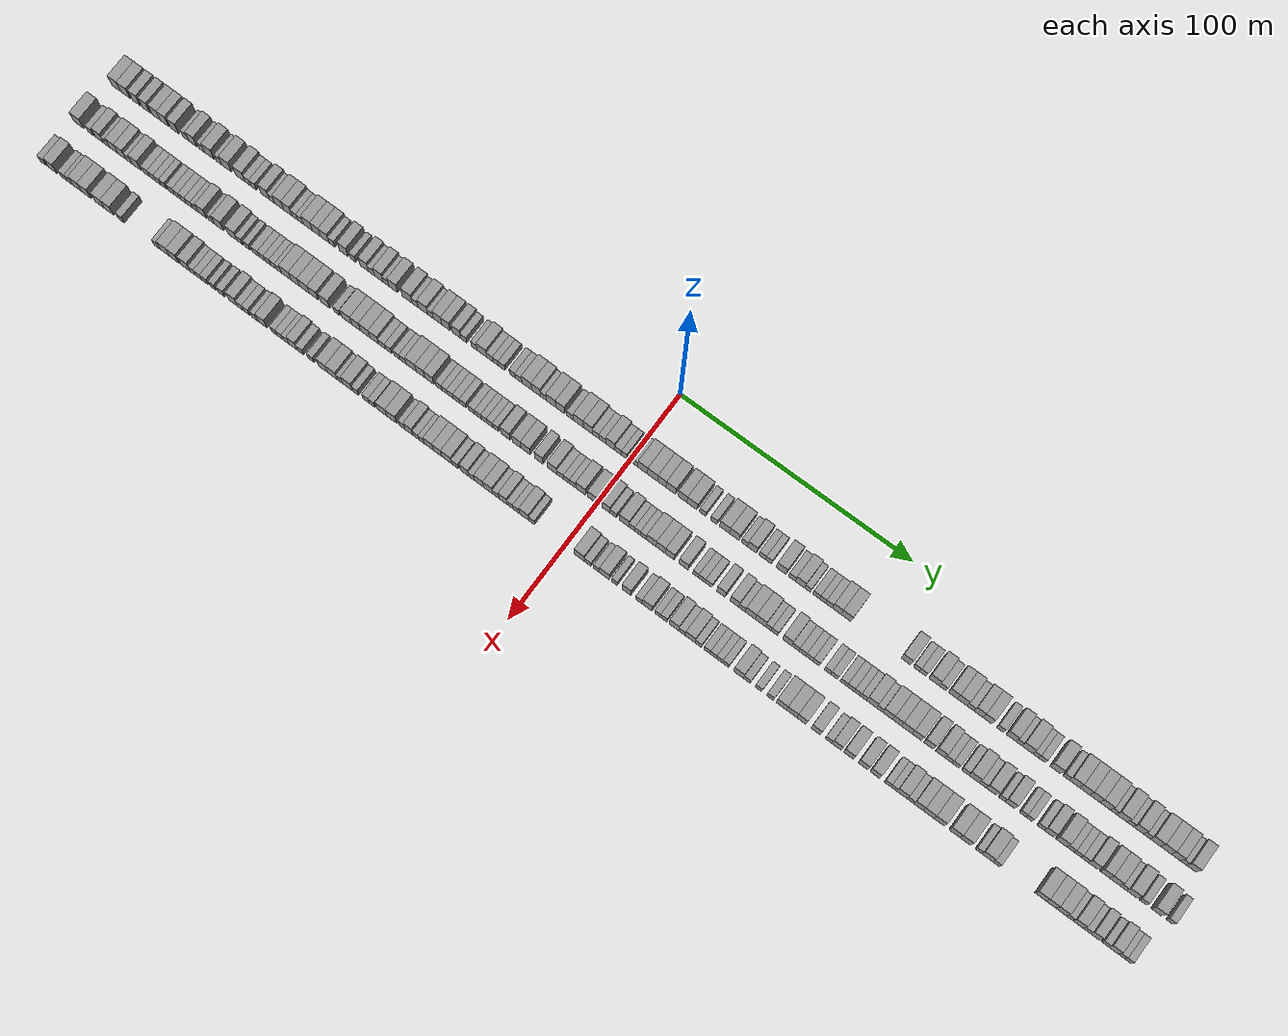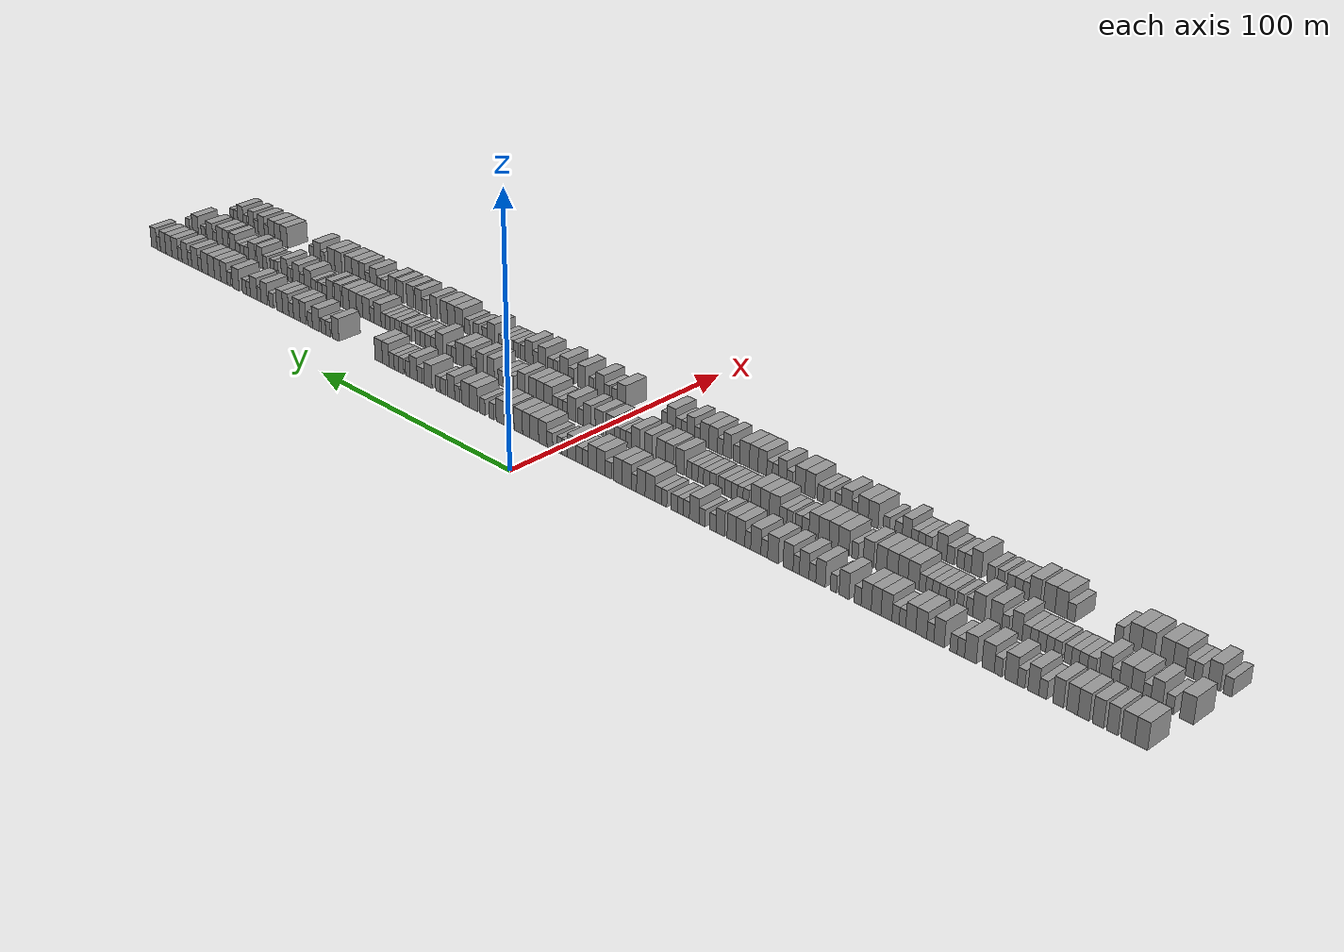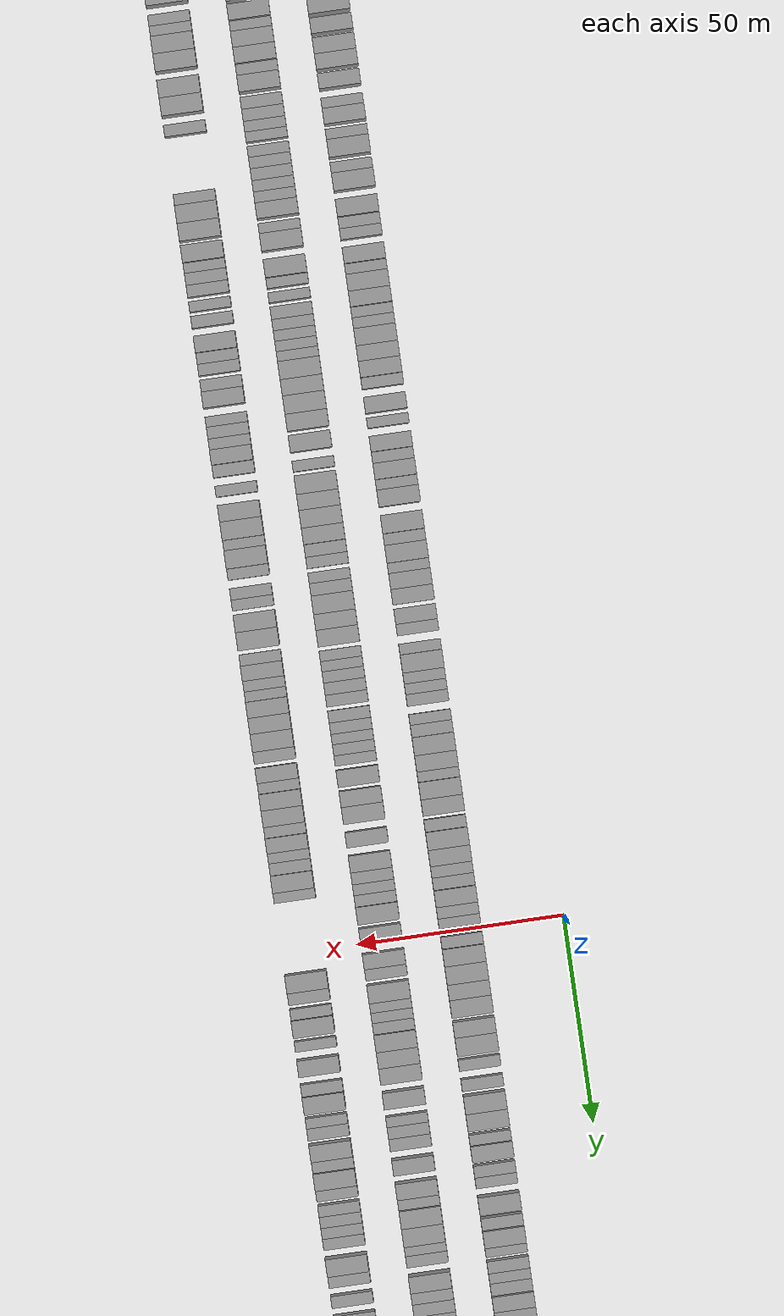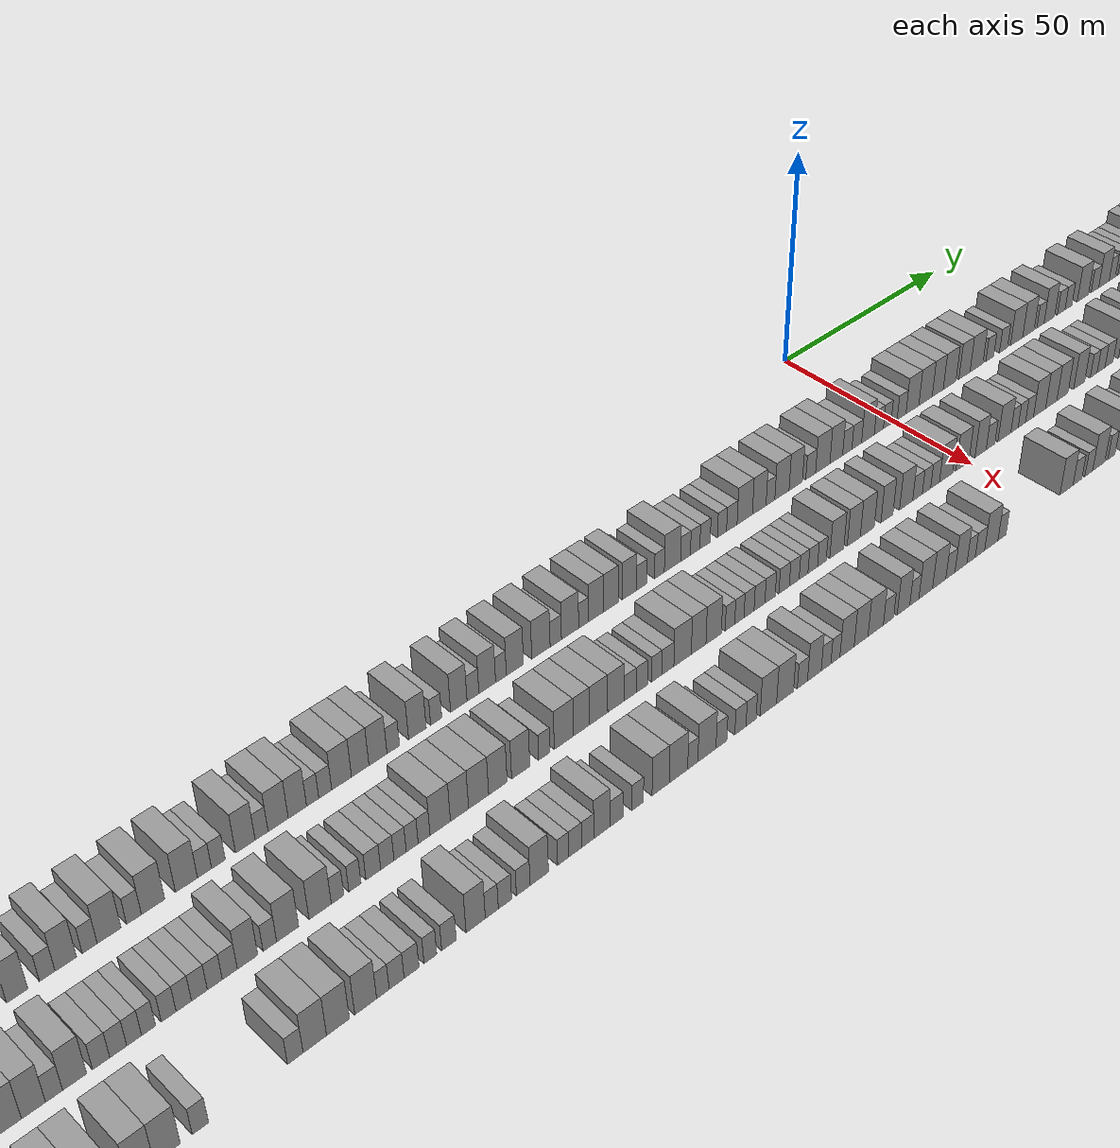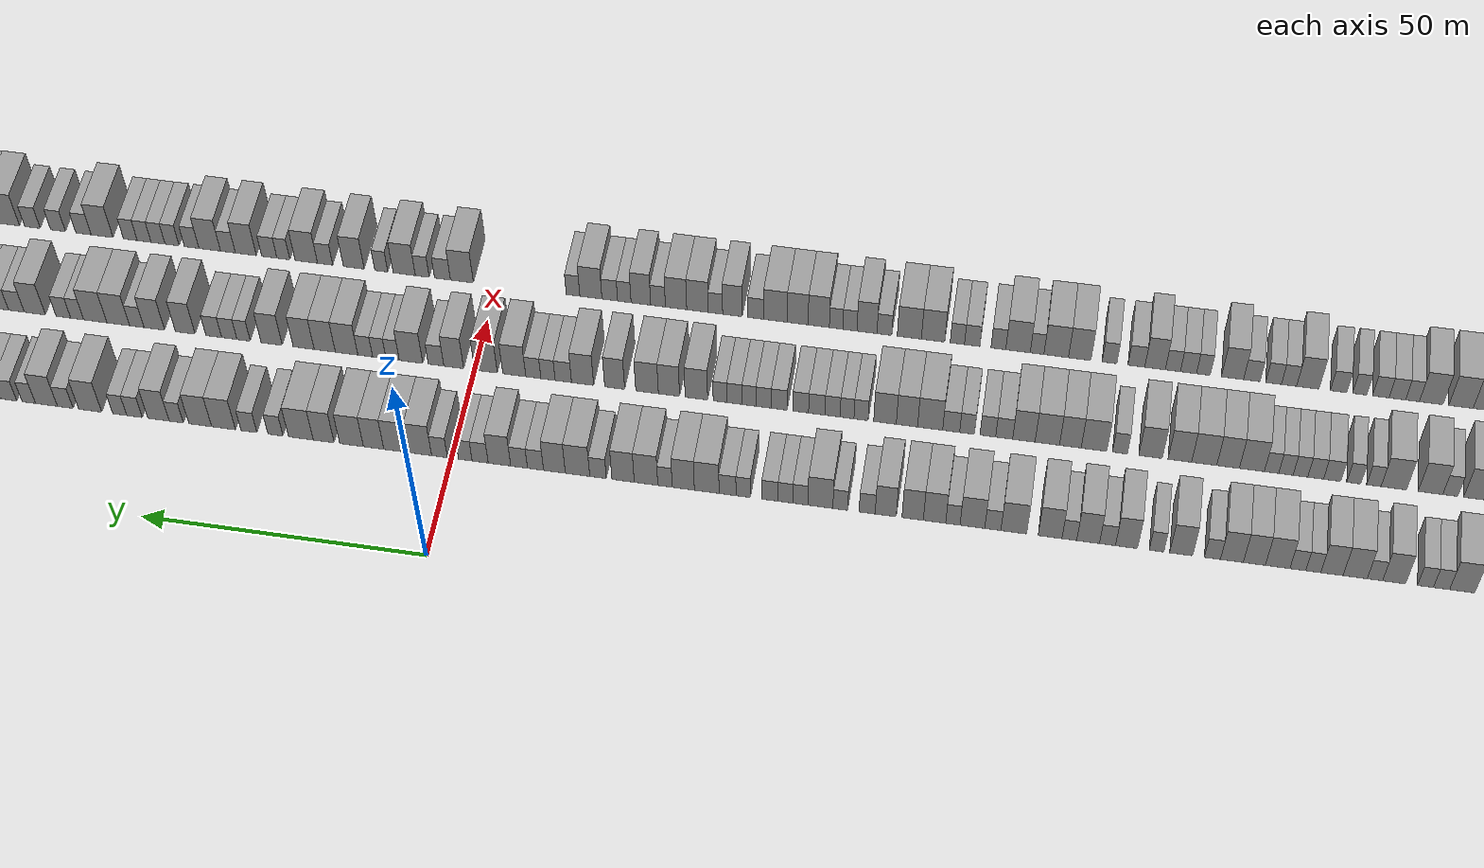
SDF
<sdf version="1.6">
 <world name="default">
  <scene>
   <sky><clouds><speed>12</speed></clouds></sky>
   <ambient>0.4 0.4 0.4 1</ambient>
   <background>0.7 0.7 0.7 1</background>
   <shadows>1</shadows>
  </scene>
  <gravity>0 0 -9.8066</gravity>
  <magnetic_field>6e-06 2.3e-05 -4.2e-05</magnetic_field>
  <physics default="0" name="default_physics" type="ode">
   <ode>
    <solver>
     <type>quick</type>
     <iters>10</iters>
     <sor>1.0</sor>
     <use_dynamic_moi_rescaling>0</use_dynamic_moi_rescaling>
    </solver>
    <constraints>
     <cfm>0</cfm>
     <erp>0.2</erp>
     <contact_max_correcting_vel>100</contact_max_correcting_vel>
     <contact_surface_layer>0.001</contact_surface_layer>
    </constraints>
   </ode>
   <max_step_size>0.004</max_step_size>
   <real_time_factor>1</real_time_factor>
   <real_time_update_rate>250</real_time_update_rate>
  </physics>
  <light name="sun" type="directional">
   <pose>0 0 10 0 0 0</pose>
   <diffuse>0.8 0.8 0.8 1</diffuse>
   <specular>0.2 0.2 0.2 1</specular>
   <attenuation>
    <range>1000</range>
    <constant>0.9</constant>
    <linear>0.01</linear>
    <quadratic>0.001</quadratic>
   </attenuation>
   <direction>-0.5 0.1 -0.9</direction>
  </light>
  <model name="building_1">
   <static>1</static>
   <pose>25.0000 -231.9300 0 0.000000 0.000000 0.000000</pose>
   <link name="link">
    <pose>0 0 4.50 0 0 0</pose>
    <collision name="collision"><geometry><box><size>10.0000 4.1400 9.0000</size></box></geometry></collision>
    <visual name="visual">
     <cast_shadows>0</cast_shadows>
     <geometry><box><size>10.0000 4.1400 9.0000</size></box></geometry>
     <material>
      <script>
       <uri>model://grey_wall/materials/scripts</uri>
       <uri>model://grey_wall/materials/textures</uri>
       <name>vrc/grey_wall</name>
      </script>
     </material>
    </visual>
   </link>
  </model>
  <model name="building_2">
   <static>1</static>
   <pose>25.0000 -227.6658 0 0.000000 0.000000 0.000000</pose>
   <link name="link">
    <pose>0 0 4.50 0 0 0</pose>
    <collision name="collision"><geometry><box><size>10.0000 4.3886 9.0000</size></box></geometry></collision>
    <visual name="visual">
     <cast_shadows>0</cast_shadows>
     <geometry><box><size>10.0000 4.3886 9.0000</size></box></geometry>
     <material>
      <script>
       <uri>model://grey_wall/materials/scripts</uri>
       <uri>model://grey_wall/materials/textures</uri>
       <name>vrc/grey_wall</name>
      </script>
     </material>
    </visual>
   </link>
  </model>
  <model name="building_3">
   <static>1</static>
   <pose>25.0000 -222.6575 0 0.000000 0.000000 0.000000</pose>
   <link name="link">
    <pose>0 0 4.50 0 0 0</pose>
    <collision name="collision"><geometry><box><size>10.0000 3.6280 9.0000</size></box></geometry></collision>
    <visual name="visual">
     <cast_shadows>0</cast_shadows>
     <geometry><box><size>10.0000 3.6280 9.0000</size></box></geometry>
     <material>
      <script>
       <uri>model://grey_wall/materials/scripts</uri>
       <uri>model://grey_wall/materials/textures</uri>
       <name>vrc/grey_wall</name>
      </script>
     </material>
    </visual>
   </link>
  </model>
  <model name="building_4">
   <static>1</static>
   <pose>25.0000 -217.9881 0 0.000000 0.000000 0.000000</pose>
   <link name="link">
    <pose>0 0 4.50 0 0 0</pose>
    <collision name="collision"><geometry><box><size>10.0000 3.7108 9.0000</size></box></geometry></collision>
    <visual name="visual">
     <cast_shadows>0</cast_shadows>
     <geometry><box><size>10.0000 3.7108 9.0000</size></box></geometry>
     <material>
      <script>
       <uri>model://grey_wall/materials/scripts</uri>
       <uri>model://grey_wall/materials/textures</uri>
       <name>vrc/grey_wall</name>
      </script>
     </material>
    </visual>
   </link>
  </model>
  <model name="building_5">
   <static>1</static>
   <pose>25.0000 -213.2037 0 0.000000 0.000000 0.000000</pose>
   <link name="link">
    <pose>0 0 4.50 0 0 0</pose>
    <collision name="collision"><geometry><box><size>10.0000 3.8580 9.0000</size></box></geometry></collision>
    <visual name="visual">
     <cast_shadows>0</cast_shadows>
     <geometry><box><size>10.0000 3.8580 9.0000</size></box></geometry>
     <material>
      <script>
       <uri>model://grey_wall/materials/scripts</uri>
       <uri>model://grey_wall/materials/textures</uri>
       <name>vrc/grey_wall</name>
      </script>
     </material>
    </visual>
   </link>
  </model>
  <model name="building_6">
   <static>1</static>
   <pose>25.0000 -209.4045 0 0.000000 0.000000 0.000000</pose>
   <link name="link">
    <pose>0 0 4.50 0 0 0</pose>
    <collision name="collision"><geometry><box><size>10.0000 3.7403 9.0000</size></box></geometry></collision>
    <visual name="visual">
     <cast_shadows>0</cast_shadows>
     <geometry><box><size>10.0000 3.7403 9.0000</size></box></geometry>
     <material>
      <script>
       <uri>model://grey_wall/materials/scripts</uri>
       <uri>model://grey_wall/materials/textures</uri>
       <name>vrc/grey_wall</name>
      </script>
     </material>
    </visual>
   </link>
  </model>
  <model name="building_7">
   <static>1</static>
   <pose>25.0000 -204.7164 0 0.000000 0.000000 0.000000</pose>
   <link name="link">
    <pose>0 0 4.50 0 0 0</pose>
    <collision name="collision"><geometry><box><size>10.0000 3.6358 9.0000</size></box></geometry></collision>
    <visual name="visual">
     <cast_shadows>0</cast_shadows>
     <geometry><box><size>10.0000 3.6358 9.0000</size></box></geometry>
     <material>
      <script>
       <uri>model://grey_wall/materials/scripts</uri>
       <uri>model://grey_wall/materials/textures</uri>
       <name>vrc/grey_wall</name>
      </script>
     </material>
    </visual>
   </link>
  </model>
  <model name="building_8">
   <static>1</static>
   <pose>25.0000 -199.5510 0 0.000000 0.000000 0.000000</pose>
   <link name="link">
    <pose>0 0 3.00 0 0 0</pose>
    <collision name="collision"><geometry><box><size>10.0000 2.6950 6.0000</size></box></geometry></collision>
    <visual name="visual">
     <cast_shadows>0</cast_shadows>
     <geometry><box><size>10.0000 2.6950 6.0000</size></box></geometry>
     <material>
      <script>
       <uri>model://grey_wall/materials/scripts</uri>
       <uri>model://grey_wall/materials/textures</uri>
       <name>vrc/grey_wall</name>
      </script>
     </material>
    </visual>
   </link>
  </model>
  <model name="building_9">
   <static>1</static>
   <pose>25.0000 -196.3147 0 0.000000 0.000000 0.000000</pose>
   <link name="link">
    <pose>0 0 4.50 0 0 0</pose>
    <collision name="collision"><geometry><box><size>10.0000 3.7777 9.0000</size></box></geometry></collision>
    <visual name="visual">
     <cast_shadows>0</cast_shadows>
     <geometry><box><size>10.0000 3.7777 9.0000</size></box></geometry>
     <material>
      <script>
       <uri>model://grey_wall/materials/scripts</uri>
       <uri>model://grey_wall/materials/textures</uri>
       <name>vrc/grey_wall</name>
      </script>
     </material>
    </visual>
   </link>
  </model>
  <model name="building_10">
   <static>1</static>
   <pose>25.0000 -192.0925 0 0.000000 0.000000 0.000000</pose>
   <link name="link">
    <pose>0 0 3.00 0 0 0</pose>
    <collision name="collision"><geometry><box><size>10.0000 2.6668 6.0000</size></box></geometry></collision>
    <visual name="visual">
     <cast_shadows>0</cast_shadows>
     <geometry><box><size>10.0000 2.6668 6.0000</size></box></geometry>
     <material>
      <script>
       <uri>model://grey_wall/materials/scripts</uri>
       <uri>model://grey_wall/materials/textures</uri>
       <name>vrc/grey_wall</name>
      </script>
     </material>
    </visual>
   </link>
  </model>
  <model name="building_11">
   <static>1</static>
   <pose>25.0000 -188.5993 0 0.000000 0.000000 0.000000</pose>
   <link name="link">
    <pose>0 0 4.50 0 0 0</pose>
    <collision name="collision"><geometry><box><size>10.0000 4.3197 9.0000</size></box></geometry></collision>
    <visual name="visual">
     <cast_shadows>0</cast_shadows>
     <geometry><box><size>10.0000 4.3197 9.0000</size></box></geometry>
     <material>
      <script>
       <uri>model://grey_wall/materials/scripts</uri>
       <uri>model://grey_wall/materials/textures</uri>
       <name>vrc/grey_wall</name>
      </script>
     </material>
    </visual>
   </link>
  </model>
  <model name="building_12">
   <static>1</static>
   <pose>25.0000 -184.0821 0 0.000000 0.000000 0.000000</pose>
   <link name="link">
    <pose>0 0 3.00 0 0 0</pose>
    <collision name="collision"><geometry><box><size>10.0000 2.7145 6.0000</size></box></geometry></collision>
    <visual name="visual">
     <cast_shadows>0</cast_shadows>
     <geometry><box><size>10.0000 2.7145 6.0000</size></box></geometry>
     <material>
      <script>
       <uri>model://grey_wall/materials/scripts</uri>
       <uri>model://grey_wall/materials/textures</uri>
       <name>vrc/grey_wall</name>
      </script>
     </material>
    </visual>
   </link>
  </model>
  <model name="building_13">
   <static>1</static>
   <pose>25.0000 -180.5625 0 0.000000 0.000000 0.000000</pose>
   <link name="link">
    <pose>0 0 4.50 0 0 0</pose>
    <collision name="collision"><geometry><box><size>10.0000 4.3248 9.0000</size></box></geometry></collision>
    <visual name="visual">
     <cast_shadows>0</cast_shadows>
     <geometry><box><size>10.0000 4.3248 9.0000</size></box></geometry>
     <material>
      <script>
       <uri>model://grey_wall/materials/scripts</uri>
       <uri>model://grey_wall/materials/textures</uri>
       <name>vrc/grey_wall</name>
      </script>
     </material>
    </visual>
   </link>
  </model>
  <model name="building_14">
   <static>1</static>
   <pose>25.0000 -174.3035 0 0.000000 0.000000 0.000000</pose>
   <link name="link">
    <pose>0 0 4.50 0 0 0</pose>
    <collision name="collision"><geometry><box><size>10.0000 4.1932 9.0000</size></box></geometry></collision>
    <visual name="visual">
     <cast_shadows>0</cast_shadows>
     <geometry><box><size>10.0000 4.1932 9.0000</size></box></geometry>
     <material>
      <script>
       <uri>model://grey_wall/materials/scripts</uri>
       <uri>model://grey_wall/materials/textures</uri>
       <name>vrc/grey_wall</name>
      </script>
     </material>
    </visual>
   </link>
  </model>
  <model name="building_15">
   <static>1</static>
   <pose>25.0000 -170.8588 0 0.000000 0.000000 0.000000</pose>
   <link name="link">
    <pose>0 0 3.00 0 0 0</pose>
    <collision name="collision"><geometry><box><size>10.0000 2.6962 6.0000</size></box></geometry></collision>
    <visual name="visual">
     <cast_shadows>0</cast_shadows>
     <geometry><box><size>10.0000 2.6962 6.0000</size></box></geometry>
     <material>
      <script>
       <uri>model://grey_wall/materials/scripts</uri>
       <uri>model://grey_wall/materials/textures</uri>
       <name>vrc/grey_wall</name>
      </script>
     </material>
    </visual>
   </link>
  </model>
  <model name="building_16">
   <static>1</static>
   <pose>25.0000 -168.1811 0 0.000000 0.000000 0.000000</pose>
   <link name="link">
    <pose>0 0 3.00 0 0 0</pose>
    <collision name="collision"><geometry><box><size>10.0000 2.6592 6.0000</size></box></geometry></collision>
    <visual name="visual">
     <cast_shadows>0</cast_shadows>
     <geometry><box><size>10.0000 2.6592 6.0000</size></box></geometry>
     <material>
      <script>
       <uri>model://grey_wall/materials/scripts</uri>
       <uri>model://grey_wall/materials/textures</uri>
       <name>vrc/grey_wall</name>
      </script>
     </material>
    </visual>
   </link>
  </model>
  <model name="building_17">
   <static>1</static>
   <pose>25.0000 -162.9229 0 0.000000 0.000000 0.000000</pose>
   <link name="link">
    <pose>0 0 4.50 0 0 0</pose>
    <collision name="collision"><geometry><box><size>10.0000 3.8572 9.0000</size></box></geometry></collision>
    <visual name="visual">
     <cast_shadows>0</cast_shadows>
     <geometry><box><size>10.0000 3.8572 9.0000</size></box></geometry>
     <material>
      <script>
       <uri>model://grey_wall/materials/scripts</uri>
       <uri>model://grey_wall/materials/textures</uri>
       <name>vrc/grey_wall</name>
      </script>
     </material>
    </visual>
   </link>
  </model>
  <model name="building_18">
   <static>1</static>
   <pose>25.0000 -159.7035 0 0.000000 0.000000 0.000000</pose>
   <link name="link">
    <pose>0 0 3.00 0 0 0</pose>
    <collision name="collision"><geometry><box><size>10.0000 2.5816 6.0000</size></box></geometry></collision>
    <visual name="visual">
     <cast_shadows>0</cast_shadows>
     <geometry><box><size>10.0000 2.5816 6.0000</size></box></geometry>
     <material>
      <script>
       <uri>model://grey_wall/materials/scripts</uri>
       <uri>model://grey_wall/materials/textures</uri>
       <name>vrc/grey_wall</name>
      </script>
     </material>
    </visual>
   </link>
  </model>
  <model name="building_19">
   <static>1</static>
   <pose>25.0000 -156.3843 0 0.000000 0.000000 0.000000</pose>
   <link name="link">
    <pose>0 0 4.50 0 0 0</pose>
    <collision name="collision"><geometry><box><size>10.0000 4.0568 9.0000</size></box></geometry></collision>
    <visual name="visual">
     <cast_shadows>0</cast_shadows>
     <geometry><box><size>10.0000 4.0568 9.0000</size></box></geometry>
     <material>
      <script>
       <uri>model://grey_wall/materials/scripts</uri>
       <uri>model://grey_wall/materials/textures</uri>
       <name>vrc/grey_wall</name>
      </script>
     </material>
    </visual>
   </link>
  </model>
  <model name="building_20">
   <static>1</static>
   <pose>25.0000 -152.4815 0 0.000000 0.000000 0.000000</pose>
   <link name="link">
    <pose>0 0 4.50 0 0 0</pose>
    <collision name="collision"><geometry><box><size>10.0000 3.7489 9.0000</size></box></geometry></collision>
    <visual name="visual">
     <cast_shadows>0</cast_shadows>
     <geometry><box><size>10.0000 3.7489 9.0000</size></box></geometry>
     <material>
      <script>
       <uri>model://grey_wall/materials/scripts</uri>
       <uri>model://grey_wall/materials/textures</uri>
       <name>vrc/grey_wall</name>
      </script>
     </material>
    </visual>
   </link>
  </model>
  <model name="building_21">
   <static>1</static>
   <pose>25.0000 -149.3483 0 0.000000 0.000000 0.000000</pose>
   <link name="link">
    <pose>0 0 3.00 0 0 0</pose>
    <collision name="collision"><geometry><box><size>10.0000 2.5174 6.0000</size></box></geometry></collision>
    <visual name="visual">
     <cast_shadows>0</cast_shadows>
     <geometry><box><size>10.0000 2.5174 6.0000</size></box></geometry>
     <material>
      <script>
       <uri>model://grey_wall/materials/scripts</uri>
       <uri>model://grey_wall/materials/textures</uri>
       <name>vrc/grey_wall</name>
      </script>
     </material>
    </visual>
   </link>
  </model>
  <model name="building_22">
   <static>1</static>
   <pose>25.0000 -146.7445 0 0.000000 0.000000 0.000000</pose>
   <link name="link">
    <pose>0 0 3.00 0 0 0</pose>
    <collision name="collision"><geometry><box><size>10.0000 2.6901 6.0000</size></box></geometry></collision>
    <visual name="visual">
     <cast_shadows>0</cast_shadows>
     <geometry><box><size>10.0000 2.6901 6.0000</size></box></geometry>
     <material>
      <script>
       <uri>model://grey_wall/materials/scripts</uri>
       <uri>model://grey_wall/materials/textures</uri>
       <name>vrc/grey_wall</name>
      </script>
     </material>
    </visual>
   </link>
  </model>
  <model name="building_23">
   <static>1</static>
   <pose>25.0000 -143.3274 0 0.000000 0.000000 0.000000</pose>
   <link name="link">
    <pose>0 0 4.50 0 0 0</pose>
    <collision name="collision"><geometry><box><size>10.0000 4.1442 9.0000</size></box></geometry></collision>
    <visual name="visual">
     <cast_shadows>0</cast_shadows>
     <geometry><box><size>10.0000 4.1442 9.0000</size></box></geometry>
     <material>
      <script>
       <uri>model://grey_wall/materials/scripts</uri>
       <uri>model://grey_wall/materials/textures</uri>
       <name>vrc/grey_wall</name>
      </script>
     </material>
    </visual>
   </link>
  </model>
  <model name="building_24">
   <static>1</static>
   <pose>25.0000 -139.3913 0 0.000000 0.000000 0.000000</pose>
   <link name="link">
    <pose>0 0 4.50 0 0 0</pose>
    <collision name="collision"><geometry><box><size>10.0000 3.7280 9.0000</size></box></geometry></collision>
    <visual name="visual">
     <cast_shadows>0</cast_shadows>
     <geometry><box><size>10.0000 3.7280 9.0000</size></box></geometry>
     <material>
      <script>
       <uri>model://grey_wall/materials/scripts</uri>
       <uri>model://grey_wall/materials/textures</uri>
       <name>vrc/grey_wall</name>
      </script>
     </material>
    </visual>
   </link>
  </model>
  <model name="building_25">
   <static>1</static>
   <pose>25.0000 -135.5879 0 0.000000 0.000000 0.000000</pose>
   <link name="link">
    <pose>0 0 4.50 0 0 0</pose>
    <collision name="collision"><geometry><box><size>10.0000 3.8788 9.0000</size></box></geometry></collision>
    <visual name="visual">
     <cast_shadows>0</cast_shadows>
     <geometry><box><size>10.0000 3.8788 9.0000</size></box></geometry>
     <material>
      <script>
       <uri>model://grey_wall/materials/scripts</uri>
       <uri>model://grey_wall/materials/textures</uri>
       <name>vrc/grey_wall</name>
      </script>
     </material>
    </visual>
   </link>
  </model>
  <model name="building_26">
   <static>1</static>
   <pose>25.0000 -132.2880 0 0.000000 0.000000 0.000000</pose>
   <link name="link">
    <pose>0 0 3.00 0 0 0</pose>
    <collision name="collision"><geometry><box><size>10.0000 2.7209 6.0000</size></box></geometry></collision>
    <visual name="visual">
     <cast_shadows>0</cast_shadows>
     <geometry><box><size>10.0000 2.7209 6.0000</size></box></geometry>
     <material>
      <script>
       <uri>model://grey_wall/materials/scripts</uri>
       <uri>model://grey_wall/materials/textures</uri>
       <name>vrc/grey_wall</name>
      </script>
     </material>
    </visual>
   </link>
  </model>
  <model name="building_27">
   <static>1</static>
   <pose>25.0000 -126.9811 0 0.000000 0.000000 0.000000</pose>
   <link name="link">
    <pose>0 0 4.50 0 0 0</pose>
    <collision name="collision"><geometry><box><size>10.0000 3.8929 9.0000</size></box></geometry></collision>
    <visual name="visual">
     <cast_shadows>0</cast_shadows>
     <geometry><box><size>10.0000 3.8929 9.0000</size></box></geometry>
     <material>
      <script>
       <uri>model://grey_wall/materials/scripts</uri>
       <uri>model://grey_wall/materials/textures</uri>
       <name>vrc/grey_wall</name>
      </script>
     </material>
    </visual>
   </link>
  </model>
  <model name="building_28">
   <static>1</static>
   <pose>25.0000 -122.7918 0 0.000000 0.000000 0.000000</pose>
   <link name="link">
    <pose>0 0 3.00 0 0 0</pose>
    <collision name="collision"><geometry><box><size>10.0000 2.4857 6.0000</size></box></geometry></collision>
    <visual name="visual">
     <cast_shadows>0</cast_shadows>
     <geometry><box><size>10.0000 2.4857 6.0000</size></box></geometry>
     <material>
      <script>
       <uri>model://grey_wall/materials/scripts</uri>
       <uri>model://grey_wall/materials/textures</uri>
       <name>vrc/grey_wall</name>
      </script>
     </material>
    </visual>
   </link>
  </model>
  <model name="building_29">
   <static>1</static>
   <pose>25.0000 -117.6742 0 0.000000 0.000000 0.000000</pose>
   <link name="link">
    <pose>0 0 4.50 0 0 0</pose>
    <collision name="collision"><geometry><box><size>10.0000 3.7495 9.0000</size></box></geometry></collision>
    <visual name="visual">
     <cast_shadows>0</cast_shadows>
     <geometry><box><size>10.0000 3.7495 9.0000</size></box></geometry>
     <material>
      <script>
       <uri>model://grey_wall/materials/scripts</uri>
       <uri>model://grey_wall/materials/textures</uri>
       <name>vrc/grey_wall</name>
      </script>
     </material>
    </visual>
   </link>
  </model>
  <model name="building_30">
   <static>1</static>
   <pose>25.0000 -114.4299 0 0.000000 0.000000 0.000000</pose>
   <link name="link">
    <pose>0 0 3.00 0 0 0</pose>
    <collision name="collision"><geometry><box><size>10.0000 2.7391 6.0000</size></box></geometry></collision>
    <visual name="visual">
     <cast_shadows>0</cast_shadows>
     <geometry><box><size>10.0000 2.7391 6.0000</size></box></geometry>
     <material>
      <script>
       <uri>model://grey_wall/materials/scripts</uri>
       <uri>model://grey_wall/materials/textures</uri>
       <name>vrc/grey_wall</name>
      </script>
     </material>
    </visual>
   </link>
  </model>
  <model name="building_31">
   <static>1</static>
   <pose>25.0000 -111.1152 0 0.000000 0.000000 0.000000</pose>
   <link name="link">
    <pose>0 0 4.50 0 0 0</pose>
    <collision name="collision"><geometry><box><size>10.0000 3.8903 9.0000</size></box></geometry></collision>
    <visual name="visual">
     <cast_shadows>0</cast_shadows>
     <geometry><box><size>10.0000 3.8903 9.0000</size></box></geometry>
     <material>
      <script>
       <uri>model://grey_wall/materials/scripts</uri>
       <uri>model://grey_wall/materials/textures</uri>
       <name>vrc/grey_wall</name>
      </script>
     </material>
    </visual>
   </link>
  </model>
  <model name="building_32">
   <static>1</static>
   <pose>25.0000 -107.9080 0 0.000000 0.000000 0.000000</pose>
   <link name="link">
    <pose>0 0 3.00 0 0 0</pose>
    <collision name="collision"><geometry><box><size>10.0000 2.5241 6.0000</size></box></geometry></collision>
    <visual name="visual">
     <cast_shadows>0</cast_shadows>
     <geometry><box><size>10.0000 2.5241 6.0000</size></box></geometry>
     <material>
      <script>
       <uri>model://grey_wall/materials/scripts</uri>
       <uri>model://grey_wall/materials/textures</uri>
       <name>vrc/grey_wall</name>
      </script>
     </material>
    </visual>
   </link>
  </model>
  <model name="building_33">
   <static>1</static>
   <pose>25.0000 -104.6113 0 0.000000 0.000000 0.000000</pose>
   <link name="link">
    <pose>0 0 4.50 0 0 0</pose>
    <collision name="collision"><geometry><box><size>10.0000 4.0692 9.0000</size></box></geometry></collision>
    <visual name="visual">
     <cast_shadows>0</cast_shadows>
     <geometry><box><size>10.0000 4.0692 9.0000</size></box></geometry>
     <material>
      <script>
       <uri>model://grey_wall/materials/scripts</uri>
       <uri>model://grey_wall/materials/textures</uri>
       <name>vrc/grey_wall</name>
      </script>
     </material>
    </visual>
   </link>
  </model>
  <model name="building_34">
   <static>1</static>
   <pose>25.0000 -98.3642 0 0.000000 0.000000 0.000000</pose>
   <link name="link">
    <pose>0 0 4.50 0 0 0</pose>
    <collision name="collision"><geometry><box><size>10.0000 4.4251 9.0000</size></box></geometry></collision>
    <visual name="visual">
     <cast_shadows>0</cast_shadows>
     <geometry><box><size>10.0000 4.4251 9.0000</size></box></geometry>
     <material>
      <script>
       <uri>model://grey_wall/materials/scripts</uri>
       <uri>model://grey_wall/materials/textures</uri>
       <name>vrc/grey_wall</name>
      </script>
     </material>
    </visual>
   </link>
  </model>
  <model name="building_35">
   <static>1</static>
   <pose>25.0000 -94.7685 0 0.000000 0.000000 0.000000</pose>
   <link name="link">
    <pose>0 0 3.00 0 0 0</pose>
    <collision name="collision"><geometry><box><size>10.0000 2.7663 6.0000</size></box></geometry></collision>
    <visual name="visual">
     <cast_shadows>0</cast_shadows>
     <geometry><box><size>10.0000 2.7663 6.0000</size></box></geometry>
     <material>
      <script>
       <uri>model://grey_wall/materials/scripts</uri>
       <uri>model://grey_wall/materials/textures</uri>
       <name>vrc/grey_wall</name>
      </script>
     </material>
    </visual>
   </link>
  </model>
  <model name="building_36">
   <static>1</static>
   <pose>25.0000 -91.2528 0 0.000000 0.000000 0.000000</pose>
   <link name="link">
    <pose>0 0 4.50 0 0 0</pose>
    <collision name="collision"><geometry><box><size>10.0000 4.2651 9.0000</size></box></geometry></collision>
    <visual name="visual">
     <cast_shadows>0</cast_shadows>
     <geometry><box><size>10.0000 4.2651 9.0000</size></box></geometry>
     <material>
      <script>
       <uri>model://grey_wall/materials/scripts</uri>
       <uri>model://grey_wall/materials/textures</uri>
       <name>vrc/grey_wall</name>
      </script>
     </material>
    </visual>
   </link>
  </model>
  <model name="building_37">
   <static>1</static>
   <pose>25.0000 -87.8840 0 0.000000 0.000000 0.000000</pose>
   <link name="link">
    <pose>0 0 3.00 0 0 0</pose>
    <collision name="collision"><geometry><box><size>10.0000 2.4725 6.0000</size></box></geometry></collision>
    <visual name="visual">
     <cast_shadows>0</cast_shadows>
     <geometry><box><size>10.0000 2.4725 6.0000</size></box></geometry>
     <material>
      <script>
       <uri>model://grey_wall/materials/scripts</uri>
       <uri>model://grey_wall/materials/textures</uri>
       <name>vrc/grey_wall</name>
      </script>
     </material>
    </visual>
   </link>
  </model>
  <model name="building_38">
   <static>1</static>
   <pose>25.0000 -84.7188 0 0.000000 0.000000 0.000000</pose>
   <link name="link">
    <pose>0 0 4.50 0 0 0</pose>
    <collision name="collision"><geometry><box><size>10.0000 3.8577 9.0000</size></box></geometry></collision>
    <visual name="visual">
     <cast_shadows>0</cast_shadows>
     <geometry><box><size>10.0000 3.8577 9.0000</size></box></geometry>
     <material>
      <script>
       <uri>model://grey_wall/materials/scripts</uri>
       <uri>model://grey_wall/materials/textures</uri>
       <name>vrc/grey_wall</name>
      </script>
     </material>
    </visual>
   </link>
  </model>
  <model name="building_39">
   <static>1</static>
   <pose>25.0000 -80.9437 0 0.000000 0.000000 0.000000</pose>
   <link name="link">
    <pose>0 0 4.50 0 0 0</pose>
    <collision name="collision"><geometry><box><size>10.0000 3.6927 9.0000</size></box></geometry></collision>
    <visual name="visual">
     <cast_shadows>0</cast_shadows>
     <geometry><box><size>10.0000 3.6927 9.0000</size></box></geometry>
     <material>
      <script>
       <uri>model://grey_wall/materials/scripts</uri>
       <uri>model://grey_wall/materials/textures</uri>
       <name>vrc/grey_wall</name>
      </script>
     </material>
    </visual>
   </link>
  </model>
  <model name="building_40">
   <static>1</static>
   <pose>25.0000 -76.2715 0 0.000000 0.000000 0.000000</pose>
   <link name="link">
    <pose>0 0 4.50 0 0 0</pose>
    <collision name="collision"><geometry><box><size>10.0000 3.6517 9.0000</size></box></geometry></collision>
    <visual name="visual">
     <cast_shadows>0</cast_shadows>
     <geometry><box><size>10.0000 3.6517 9.0000</size></box></geometry>
     <material>
      <script>
       <uri>model://grey_wall/materials/scripts</uri>
       <uri>model://grey_wall/materials/textures</uri>
       <name>vrc/grey_wall</name>
      </script>
     </material>
    </visual>
   </link>
  </model>
  <model name="building_41">
   <static>1</static>
   <pose>25.0000 -73.0580 0 0.000000 0.000000 0.000000</pose>
   <link name="link">
    <pose>0 0 3.00 0 0 0</pose>
    <collision name="collision"><geometry><box><size>10.0000 2.7753 6.0000</size></box></geometry></collision>
    <visual name="visual">
     <cast_shadows>0</cast_shadows>
     <geometry><box><size>10.0000 2.7753 6.0000</size></box></geometry>
     <material>
      <script>
       <uri>model://grey_wall/materials/scripts</uri>
       <uri>model://grey_wall/materials/textures</uri>
       <name>vrc/grey_wall</name>
      </script>
     </material>
    </visual>
   </link>
  </model>
  <model name="building_42">
   <static>1</static>
   <pose>25.0000 -68.3891 0 0.000000 0.000000 0.000000</pose>
   <link name="link">
    <pose>0 0 3.00 0 0 0</pose>
    <collision name="collision"><geometry><box><size>10.0000 2.5624 6.0000</size></box></geometry></collision>
    <visual name="visual">
     <cast_shadows>0</cast_shadows>
     <geometry><box><size>10.0000 2.5624 6.0000</size></box></geometry>
     <material>
      <script>
       <uri>model://grey_wall/materials/scripts</uri>
       <uri>model://grey_wall/materials/textures</uri>
       <name>vrc/grey_wall</name>
      </script>
     </material>
    </visual>
   </link>
  </model>
  <model name="building_43">
   <static>1</static>
   <pose>25.0000 -64.9371 0 0.000000 0.000000 0.000000</pose>
   <link name="link">
    <pose>0 0 4.50 0 0 0</pose>
    <collision name="collision"><geometry><box><size>10.0000 4.3416 9.0000</size></box></geometry></collision>
    <visual name="visual">
     <cast_shadows>0</cast_shadows>
     <geometry><box><size>10.0000 4.3416 9.0000</size></box></geometry>
     <material>
      <script>
       <uri>model://grey_wall/materials/scripts</uri>
       <uri>model://grey_wall/materials/textures</uri>
       <name>vrc/grey_wall</name>
      </script>
     </material>
    </visual>
   </link>
  </model>
  <model name="building_44">
   <static>1</static>
   <pose>25.0000 -61.4347 0 0.000000 0.000000 0.000000</pose>
   <link name="link">
    <pose>0 0 3.00 0 0 0</pose>
    <collision name="collision"><geometry><box><size>10.0000 2.6632 6.0000</size></box></geometry></collision>
    <visual name="visual">
     <cast_shadows>0</cast_shadows>
     <geometry><box><size>10.0000 2.6632 6.0000</size></box></geometry>
     <material>
      <script>
       <uri>model://grey_wall/materials/scripts</uri>
       <uri>model://grey_wall/materials/textures</uri>
       <name>vrc/grey_wall</name>
      </script>
     </material>
    </visual>
   </link>
  </model>
  <model name="building_45">
   <static>1</static>
   <pose>25.0000 -58.8214 0 0.000000 0.000000 0.000000</pose>
   <link name="link">
    <pose>0 0 3.00 0 0 0</pose>
    <collision name="collision"><geometry><box><size>10.0000 2.5635 6.0000</size></box></geometry></collision>
    <visual name="visual">
     <cast_shadows>0</cast_shadows>
     <geometry><box><size>10.0000 2.5635 6.0000</size></box></geometry>
     <material>
      <script>
       <uri>model://grey_wall/materials/scripts</uri>
       <uri>model://grey_wall/materials/textures</uri>
       <name>vrc/grey_wall</name>
      </script>
     </material>
    </visual>
   </link>
  </model>
  <model name="building_46">
   <static>1</static>
   <pose>25.0000 -56.1312 0 0.000000 0.000000 0.000000</pose>
   <link name="link">
    <pose>0 0 3.00 0 0 0</pose>
    <collision name="collision"><geometry><box><size>10.0000 2.8169 6.0000</size></box></geometry></collision>
    <visual name="visual">
     <cast_shadows>0</cast_shadows>
     <geometry><box><size>10.0000 2.8169 6.0000</size></box></geometry>
     <material>
      <script>
       <uri>model://grey_wall/materials/scripts</uri>
       <uri>model://grey_wall/materials/textures</uri>
       <name>vrc/grey_wall</name>
      </script>
     </material>
    </visual>
   </link>
  </model>
  <model name="building_47">
   <static>1</static>
   <pose>25.0000 -51.4652 0 0.000000 0.000000 0.000000</pose>
   <link name="link">
    <pose>0 0 3.00 0 0 0</pose>
    <collision name="collision"><geometry><box><size>10.0000 2.5151 6.0000</size></box></geometry></collision>
    <visual name="visual">
     <cast_shadows>0</cast_shadows>
     <geometry><box><size>10.0000 2.5151 6.0000</size></box></geometry>
     <material>
      <script>
       <uri>model://grey_wall/materials/scripts</uri>
       <uri>model://grey_wall/materials/textures</uri>
       <name>vrc/grey_wall</name>
      </script>
     </material>
    </visual>
   </link>
  </model>
  <model name="building_48">
   <static>1</static>
   <pose>25.0000 -48.7273 0 0.000000 0.000000 0.000000</pose>
   <link name="link">
    <pose>0 0 3.00 0 0 0</pose>
    <collision name="collision"><geometry><box><size>10.0000 2.9607 6.0000</size></box></geometry></collision>
    <visual name="visual">
     <cast_shadows>0</cast_shadows>
     <geometry><box><size>10.0000 2.9607 6.0000</size></box></geometry>
     <material>
      <script>
       <uri>model://grey_wall/materials/scripts</uri>
       <uri>model://grey_wall/materials/textures</uri>
       <name>vrc/grey_wall</name>
      </script>
     </material>
    </visual>
   </link>
  </model>
  <model name="building_49">
   <static>1</static>
   <pose>25.0000 -45.0810 0 0.000000 0.000000 0.000000</pose>
   <link name="link">
    <pose>0 0 4.50 0 0 0</pose>
    <collision name="collision"><geometry><box><size>10.0000 4.3319 9.0000</size></box></geometry></collision>
    <visual name="visual">
     <cast_shadows>0</cast_shadows>
     <geometry><box><size>10.0000 4.3319 9.0000</size></box></geometry>
     <material>
      <script>
       <uri>model://grey_wall/materials/scripts</uri>
       <uri>model://grey_wall/materials/textures</uri>
       <name>vrc/grey_wall</name>
      </script>
     </material>
    </visual>
   </link>
  </model>
  <model name="building_50">
   <static>1</static>
   <pose>25.0000 -40.9678 0 0.000000 0.000000 0.000000</pose>
   <link name="link">
    <pose>0 0 4.50 0 0 0</pose>
    <collision name="collision"><geometry><box><size>10.0000 3.8946 9.0000</size></box></geometry></collision>
    <visual name="visual">
     <cast_shadows>0</cast_shadows>
     <geometry><box><size>10.0000 3.8946 9.0000</size></box></geometry>
     <material>
      <script>
       <uri>model://grey_wall/materials/scripts</uri>
       <uri>model://grey_wall/materials/textures</uri>
       <name>vrc/grey_wall</name>
      </script>
     </material>
    </visual>
   </link>
  </model>
  <model name="building_51">
   <static>1</static>
   <pose>25.0000 -37.7538 0 0.000000 0.000000 0.000000</pose>
   <link name="link">
    <pose>0 0 3.00 0 0 0</pose>
    <collision name="collision"><geometry><box><size>10.0000 2.5332 6.0000</size></box></geometry></collision>
    <visual name="visual">
     <cast_shadows>0</cast_shadows>
     <geometry><box><size>10.0000 2.5332 6.0000</size></box></geometry>
     <material>
      <script>
       <uri>model://grey_wall/materials/scripts</uri>
       <uri>model://grey_wall/materials/textures</uri>
       <name>vrc/grey_wall</name>
      </script>
     </material>
    </visual>
   </link>
  </model>
  <model name="building_52">
   <static>1</static>
   <pose>25.0000 -34.4127 0 0.000000 0.000000 0.000000</pose>
   <link name="link">
    <pose>0 0 4.50 0 0 0</pose>
    <collision name="collision"><geometry><box><size>10.0000 4.1491 9.0000</size></box></geometry></collision>
    <visual name="visual">
     <cast_shadows>0</cast_shadows>
     <geometry><box><size>10.0000 4.1491 9.0000</size></box></geometry>
     <material>
      <script>
       <uri>model://grey_wall/materials/scripts</uri>
       <uri>model://grey_wall/materials/textures</uri>
       <name>vrc/grey_wall</name>
      </script>
     </material>
    </visual>
   </link>
  </model>
  <model name="building_53">
   <static>1</static>
   <pose>25.0000 -30.3759 0 0.000000 0.000000 0.000000</pose>
   <link name="link">
    <pose>0 0 4.50 0 0 0</pose>
    <collision name="collision"><geometry><box><size>10.0000 3.9244 9.0000</size></box></geometry></collision>
    <visual name="visual">
     <cast_shadows>0</cast_shadows>
     <geometry><box><size>10.0000 3.9244 9.0000</size></box></geometry>
     <material>
      <script>
       <uri>model://grey_wall/materials/scripts</uri>
       <uri>model://grey_wall/materials/textures</uri>
       <name>vrc/grey_wall</name>
      </script>
     </material>
    </visual>
   </link>
  </model>
  <model name="building_54">
   <static>1</static>
   <pose>25.0000 -25.9550 0 0.000000 0.000000 0.000000</pose>
   <link name="link">
    <pose>0 0 3.00 0 0 0</pose>
    <collision name="collision"><geometry><box><size>10.0000 2.9175 6.0000</size></box></geometry></collision>
    <visual name="visual">
     <cast_shadows>0</cast_shadows>
     <geometry><box><size>10.0000 2.9175 6.0000</size></box></geometry>
     <material>
      <script>
       <uri>model://grey_wall/materials/scripts</uri>
       <uri>model://grey_wall/materials/textures</uri>
       <name>vrc/grey_wall</name>
      </script>
     </material>
    </visual>
   </link>
  </model>
  <model name="building_55">
   <static>1</static>
   <pose>25.0000 -22.3386 0 0.000000 0.000000 0.000000</pose>
   <link name="link">
    <pose>0 0 4.50 0 0 0</pose>
    <collision name="collision"><geometry><box><size>10.0000 4.3151 9.0000</size></box></geometry></collision>
    <visual name="visual">
     <cast_shadows>0</cast_shadows>
     <geometry><box><size>10.0000 4.3151 9.0000</size></box></geometry>
     <material>
      <script>
       <uri>model://grey_wall/materials/scripts</uri>
       <uri>model://grey_wall/materials/textures</uri>
       <name>vrc/grey_wall</name>
      </script>
     </material>
    </visual>
   </link>
  </model>
  <model name="building_56">
   <static>1</static>
   <pose>25.0000 -18.2436 0 0.000000 0.000000 0.000000</pose>
   <link name="link">
    <pose>0 0 4.50 0 0 0</pose>
    <collision name="collision"><geometry><box><size>10.0000 3.8750 9.0000</size></box></geometry></collision>
    <visual name="visual">
     <cast_shadows>0</cast_shadows>
     <geometry><box><size>10.0000 3.8750 9.0000</size></box></geometry>
     <material>
      <script>
       <uri>model://grey_wall/materials/scripts</uri>
       <uri>model://grey_wall/materials/textures</uri>
       <name>vrc/grey_wall</name>
      </script>
     </material>
    </visual>
   </link>
  </model>
  <model name="building_57">
   <static>1</static>
   <pose>25.0000 -14.8809 0 0.000000 0.000000 0.000000</pose>
   <link name="link">
    <pose>0 0 3.00 0 0 0</pose>
    <collision name="collision"><geometry><box><size>10.0000 2.8504 6.0000</size></box></geometry></collision>
    <visual name="visual">
     <cast_shadows>0</cast_shadows>
     <geometry><box><size>10.0000 2.8504 6.0000</size></box></geometry>
     <material>
      <script>
       <uri>model://grey_wall/materials/scripts</uri>
       <uri>model://grey_wall/materials/textures</uri>
       <name>vrc/grey_wall</name>
      </script>
     </material>
    </visual>
   </link>
  </model>
  <model name="building_58">
   <static>1</static>
   <pose>25.0000 -11.9682 0 0.000000 0.000000 0.000000</pose>
   <link name="link">
    <pose>0 0 3.00 0 0 0</pose>
    <collision name="collision"><geometry><box><size>10.0000 2.9750 6.0000</size></box></geometry></collision>
    <visual name="visual">
     <cast_shadows>0</cast_shadows>
     <geometry><box><size>10.0000 2.9750 6.0000</size></box></geometry>
     <material>
      <script>
       <uri>model://grey_wall/materials/scripts</uri>
       <uri>model://grey_wall/materials/textures</uri>
       <name>vrc/grey_wall</name>
      </script>
     </material>
    </visual>
   </link>
  </model>
  <model name="building_59">
   <static>1</static>
   <pose>25.0000 -8.4832 0 0.000000 0.000000 0.000000</pose>
   <link name="link">
    <pose>0 0 4.50 0 0 0</pose>
    <collision name="collision"><geometry><box><size>10.0000 3.9950 9.0000</size></box></geometry></collision>
    <visual name="visual">
     <cast_shadows>0</cast_shadows>
     <geometry><box><size>10.0000 3.9950 9.0000</size></box></geometry>
     <material>
      <script>
       <uri>model://grey_wall/materials/scripts</uri>
       <uri>model://grey_wall/materials/textures</uri>
       <name>vrc/grey_wall</name>
      </script>
     </material>
    </visual>
   </link>
  </model>
  <model name="building_60">
   <static>1</static>
   <pose>25.0000 -5.0542 0 0.000000 0.000000 0.000000</pose>
   <link name="link">
    <pose>0 0 3.00 0 0 0</pose>
    <collision name="collision"><geometry><box><size>10.0000 2.8629 6.0000</size></box></geometry></collision>
    <visual name="visual">
     <cast_shadows>0</cast_shadows>
     <geometry><box><size>10.0000 2.8629 6.0000</size></box></geometry>
     <material>
      <script>
       <uri>model://grey_wall/materials/scripts</uri>
       <uri>model://grey_wall/materials/textures</uri>
       <name>vrc/grey_wall</name>
      </script>
     </material>
    </visual>
   </link>
  </model>
  <model name="building_61">
   <static>1</static>
   <pose>25.0000 -2.4190 0 0.000000 0.000000 0.000000</pose>
   <link name="link">
    <pose>0 0 3.00 0 0 0</pose>
    <collision name="collision"><geometry><box><size>10.0000 2.4077 6.0000</size></box></geometry></collision>
    <visual name="visual">
     <cast_shadows>0</cast_shadows>
     <geometry><box><size>10.0000 2.4077 6.0000</size></box></geometry>
     <material>
      <script>
       <uri>model://grey_wall/materials/scripts</uri>
       <uri>model://grey_wall/materials/textures</uri>
       <name>vrc/grey_wall</name>
      </script>
     </material>
    </visual>
   </link>
  </model>
  <model name="building_62">
   <static>1</static>
   <pose>25.0000 2.1935 0 0.000000 0.000000 0.000000</pose>
   <link name="link">
    <pose>0 0 3.00 0 0 0</pose>
    <collision name="collision"><geometry><box><size>10.0000 2.8173 6.0000</size></box></geometry></collision>
    <visual name="visual">
     <cast_shadows>0</cast_shadows>
     <geometry><box><size>10.0000 2.8173 6.0000</size></box></geometry>
     <material>
      <script>
       <uri>model://grey_wall/materials/scripts</uri>
       <uri>model://grey_wall/materials/textures</uri>
       <name>vrc/grey_wall</name>
      </script>
     </material>
    </visual>
   </link>
  </model>
  <model name="building_63">
   <static>1</static>
   <pose>25.0000 5.6832 0 0.000000 0.000000 0.000000</pose>
   <link name="link">
    <pose>0 0 4.50 0 0 0</pose>
    <collision name="collision"><geometry><box><size>10.0000 4.1620 9.0000</size></box></geometry></collision>
    <visual name="visual">
     <cast_shadows>0</cast_shadows>
     <geometry><box><size>10.0000 4.1620 9.0000</size></box></geometry>
     <material>
      <script>
       <uri>model://grey_wall/materials/scripts</uri>
       <uri>model://grey_wall/materials/textures</uri>
       <name>vrc/grey_wall</name>
      </script>
     </material>
    </visual>
   </link>
  </model>
  <model name="building_64">
   <static>1</static>
   <pose>25.0000 9.9566 0 0.000000 0.000000 0.000000</pose>
   <link name="link">
    <pose>0 0 4.50 0 0 0</pose>
    <collision name="collision"><geometry><box><size>10.0000 4.3848 9.0000</size></box></geometry></collision>
    <visual name="visual">
     <cast_shadows>0</cast_shadows>
     <geometry><box><size>10.0000 4.3848 9.0000</size></box></geometry>
     <material>
      <script>
       <uri>model://grey_wall/materials/scripts</uri>
       <uri>model://grey_wall/materials/textures</uri>
       <name>vrc/grey_wall</name>
      </script>
     </material>
    </visual>
   </link>
  </model>
  <model name="building_65">
   <static>1</static>
   <pose>25.0000 13.9862 0 0.000000 0.000000 0.000000</pose>
   <link name="link">
    <pose>0 0 4.50 0 0 0</pose>
    <collision name="collision"><geometry><box><size>10.0000 3.6744 9.0000</size></box></geometry></collision>
    <visual name="visual">
     <cast_shadows>0</cast_shadows>
     <geometry><box><size>10.0000 3.6744 9.0000</size></box></geometry>
     <material>
      <script>
       <uri>model://grey_wall/materials/scripts</uri>
       <uri>model://grey_wall/materials/textures</uri>
       <name>vrc/grey_wall</name>
      </script>
     </material>
    </visual>
   </link>
  </model>
  <model name="building_66">
   <static>1</static>
   <pose>25.0000 17.9464 0 0.000000 0.000000 0.000000</pose>
   <link name="link">
    <pose>0 0 4.50 0 0 0</pose>
    <collision name="collision"><geometry><box><size>10.0000 4.2461 9.0000</size></box></geometry></collision>
    <visual name="visual">
     <cast_shadows>0</cast_shadows>
     <geometry><box><size>10.0000 4.2461 9.0000</size></box></geometry>
     <material>
      <script>
       <uri>model://grey_wall/materials/scripts</uri>
       <uri>model://grey_wall/materials/textures</uri>
       <name>vrc/grey_wall</name>
      </script>
     </material>
    </visual>
   </link>
  </model>
  <model name="building_67">
   <static>1</static>
   <pose>25.0000 22.9572 0 0.000000 0.000000 0.000000</pose>
   <link name="link">
    <pose>0 0 4.50 0 0 0</pose>
    <collision name="collision"><geometry><box><size>10.0000 3.7754 9.0000</size></box></geometry></collision>
    <visual name="visual">
     <cast_shadows>0</cast_shadows>
     <geometry><box><size>10.0000 3.7754 9.0000</size></box></geometry>
     <material>
      <script>
       <uri>model://grey_wall/materials/scripts</uri>
       <uri>model://grey_wall/materials/textures</uri>
       <name>vrc/grey_wall</name>
      </script>
     </material>
    </visual>
   </link>
  </model>
  <model name="building_68">
   <static>1</static>
   <pose>25.0000 27.0579 0 0.000000 0.000000 0.000000</pose>
   <link name="link">
    <pose>0 0 4.50 0 0 0</pose>
    <collision name="collision"><geometry><box><size>10.0000 4.4261 9.0000</size></box></geometry></collision>
    <visual name="visual">
     <cast_shadows>0</cast_shadows>
     <geometry><box><size>10.0000 4.4261 9.0000</size></box></geometry>
     <material>
      <script>
       <uri>model://grey_wall/materials/scripts</uri>
       <uri>model://grey_wall/materials/textures</uri>
       <name>vrc/grey_wall</name>
      </script>
     </material>
    </visual>
   </link>
  </model>
  <model name="building_69">
   <static>1</static>
   <pose>25.0000 31.6316 0 0.000000 0.000000 0.000000</pose>
   <link name="link">
    <pose>0 0 3.00 0 0 0</pose>
    <collision name="collision"><geometry><box><size>10.0000 2.7215 6.0000</size></box></geometry></collision>
    <visual name="visual">
     <cast_shadows>0</cast_shadows>
     <geometry><box><size>10.0000 2.7215 6.0000</size></box></geometry>
     <material>
      <script>
       <uri>model://grey_wall/materials/scripts</uri>
       <uri>model://grey_wall/materials/textures</uri>
       <name>vrc/grey_wall</name>
      </script>
     </material>
    </visual>
   </link>
  </model>
  <model name="building_70">
   <static>1</static>
   <pose>25.0000 36.4275 0 0.000000 0.000000 0.000000</pose>
   <link name="link">
    <pose>0 0 3.00 0 0 0</pose>
    <collision name="collision"><geometry><box><size>10.0000 2.8701 6.0000</size></box></geometry></collision>
    <visual name="visual">
     <cast_shadows>0</cast_shadows>
     <geometry><box><size>10.0000 2.8701 6.0000</size></box></geometry>
     <material>
      <script>
       <uri>model://grey_wall/materials/scripts</uri>
       <uri>model://grey_wall/materials/textures</uri>
       <name>vrc/grey_wall</name>
      </script>
     </material>
    </visual>
   </link>
  </model>
  <model name="building_71">
   <static>1</static>
   <pose>25.0000 41.0288 0 0.000000 0.000000 0.000000</pose>
   <link name="link">
    <pose>0 0 4.50 0 0 0</pose>
    <collision name="collision"><geometry><box><size>10.0000 4.3326 9.0000</size></box></geometry></collision>
    <visual name="visual">
     <cast_shadows>0</cast_shadows>
     <geometry><box><size>10.0000 4.3326 9.0000</size></box></geometry>
     <material>
      <script>
       <uri>model://grey_wall/materials/scripts</uri>
       <uri>model://grey_wall/materials/textures</uri>
       <name>vrc/grey_wall</name>
      </script>
     </material>
    </visual>
   </link>
  </model>
  <model name="building_72">
   <static>1</static>
   <pose>25.0000 45.2590 0 0.000000 0.000000 0.000000</pose>
   <link name="link">
    <pose>0 0 4.50 0 0 0</pose>
    <collision name="collision"><geometry><box><size>10.0000 4.1278 9.0000</size></box></geometry></collision>
    <visual name="visual">
     <cast_shadows>0</cast_shadows>
     <geometry><box><size>10.0000 4.1278 9.0000</size></box></geometry>
     <material>
      <script>
       <uri>model://grey_wall/materials/scripts</uri>
       <uri>model://grey_wall/materials/textures</uri>
       <name>vrc/grey_wall</name>
      </script>
     </material>
    </visual>
   </link>
  </model>
  <model name="building_73">
   <static>1</static>
   <pose>25.0000 49.6135 0 0.000000 0.000000 0.000000</pose>
   <link name="link">
    <pose>0 0 3.00 0 0 0</pose>
    <collision name="collision"><geometry><box><size>10.0000 2.5813 6.0000</size></box></geometry></collision>
    <visual name="visual">
     <cast_shadows>0</cast_shadows>
     <geometry><box><size>10.0000 2.5813 6.0000</size></box></geometry>
     <material>
      <script>
       <uri>model://grey_wall/materials/scripts</uri>
       <uri>model://grey_wall/materials/textures</uri>
       <name>vrc/grey_wall</name>
      </script>
     </material>
    </visual>
   </link>
  </model>
  <model name="building_74">
   <static>1</static>
   <pose>25.0000 52.8461 0 0.000000 0.000000 0.000000</pose>
   <link name="link">
    <pose>0 0 4.50 0 0 0</pose>
    <collision name="collision"><geometry><box><size>10.0000 3.8839 9.0000</size></box></geometry></collision>
    <visual name="visual">
     <cast_shadows>0</cast_shadows>
     <geometry><box><size>10.0000 3.8839 9.0000</size></box></geometry>
     <material>
      <script>
       <uri>model://grey_wall/materials/scripts</uri>
       <uri>model://grey_wall/materials/textures</uri>
       <name>vrc/grey_wall</name>
      </script>
     </material>
    </visual>
   </link>
  </model>
  <model name="building_75">
   <static>1</static>
   <pose>25.0000 57.2063 0 0.000000 0.000000 0.000000</pose>
   <link name="link">
    <pose>0 0 3.00 0 0 0</pose>
    <collision name="collision"><geometry><box><size>10.0000 2.8364 6.0000</size></box></geometry></collision>
    <visual name="visual">
     <cast_shadows>0</cast_shadows>
     <geometry><box><size>10.0000 2.8364 6.0000</size></box></geometry>
     <material>
      <script>
       <uri>model://grey_wall/materials/scripts</uri>
       <uri>model://grey_wall/materials/textures</uri>
       <name>vrc/grey_wall</name>
      </script>
     </material>
    </visual>
   </link>
  </model>
  <model name="building_76">
   <static>1</static>
   <pose>25.0000 59.9047 0 0.000000 0.000000 0.000000</pose>
   <link name="link">
    <pose>0 0 3.00 0 0 0</pose>
    <collision name="collision"><geometry><box><size>10.0000 2.5603 6.0000</size></box></geometry></collision>
    <visual name="visual">
     <cast_shadows>0</cast_shadows>
     <geometry><box><size>10.0000 2.5603 6.0000</size></box></geometry>
     <material>
      <script>
       <uri>model://grey_wall/materials/scripts</uri>
       <uri>model://grey_wall/materials/textures</uri>
       <name>vrc/grey_wall</name>
      </script>
     </material>
    </visual>
   </link>
  </model>
  <model name="building_77">
   <static>1</static>
   <pose>25.0000 65.2968 0 0.000000 0.000000 0.000000</pose>
   <link name="link">
    <pose>0 0 4.50 0 0 0</pose>
    <collision name="collision"><geometry><box><size>10.0000 4.2241 9.0000</size></box></geometry></collision>
    <visual name="visual">
     <cast_shadows>0</cast_shadows>
     <geometry><box><size>10.0000 4.2241 9.0000</size></box></geometry>
     <material>
      <script>
       <uri>model://grey_wall/materials/scripts</uri>
       <uri>model://grey_wall/materials/textures</uri>
       <name>vrc/grey_wall</name>
      </script>
     </material>
    </visual>
   </link>
  </model>
  <model name="building_78">
   <static>1</static>
   <pose>25.0000 69.8525 0 0.000000 0.000000 0.000000</pose>
   <link name="link">
    <pose>0 0 3.00 0 0 0</pose>
    <collision name="collision"><geometry><box><size>10.0000 2.8872 6.0000</size></box></geometry></collision>
    <visual name="visual">
     <cast_shadows>0</cast_shadows>
     <geometry><box><size>10.0000 2.8872 6.0000</size></box></geometry>
     <material>
      <script>
       <uri>model://grey_wall/materials/scripts</uri>
       <uri>model://grey_wall/materials/textures</uri>
       <name>vrc/grey_wall</name>
      </script>
     </material>
    </visual>
   </link>
  </model>
  <model name="building_79">
   <static>1</static>
   <pose>25.0000 73.3049 0 0.000000 0.000000 0.000000</pose>
   <link name="link">
    <pose>0 0 4.50 0 0 0</pose>
    <collision name="collision"><geometry><box><size>10.0000 4.0175 9.0000</size></box></geometry></collision>
    <visual name="visual">
     <cast_shadows>0</cast_shadows>
     <geometry><box><size>10.0000 4.0175 9.0000</size></box></geometry>
     <material>
      <script>
       <uri>model://grey_wall/materials/scripts</uri>
       <uri>model://grey_wall/materials/textures</uri>
       <name>vrc/grey_wall</name>
      </script>
     </material>
    </visual>
   </link>
  </model>
  <model name="building_80">
   <static>1</static>
   <pose>25.0000 76.5276 0 0.000000 0.000000 0.000000</pose>
   <link name="link">
    <pose>0 0 3.00 0 0 0</pose>
    <collision name="collision"><geometry><box><size>10.0000 2.4277 6.0000</size></box></geometry></collision>
    <visual name="visual">
     <cast_shadows>0</cast_shadows>
     <geometry><box><size>10.0000 2.4277 6.0000</size></box></geometry>
     <material>
      <script>
       <uri>model://grey_wall/materials/scripts</uri>
       <uri>model://grey_wall/materials/textures</uri>
       <name>vrc/grey_wall</name>
      </script>
     </material>
    </visual>
   </link>
  </model>
  <model name="building_81">
   <static>1</static>
   <pose>25.0000 80.1868 0 0.000000 0.000000 0.000000</pose>
   <link name="link">
    <pose>0 0 3.00 0 0 0</pose>
    <collision name="collision"><geometry><box><size>10.0000 2.8907 6.0000</size></box></geometry></collision>
    <visual name="visual">
     <cast_shadows>0</cast_shadows>
     <geometry><box><size>10.0000 2.8907 6.0000</size></box></geometry>
     <material>
      <script>
       <uri>model://grey_wall/materials/scripts</uri>
       <uri>model://grey_wall/materials/textures</uri>
       <name>vrc/grey_wall</name>
      </script>
     </material>
    </visual>
   </link>
  </model>
  <model name="building_82">
   <static>1</static>
   <pose>25.0000 82.8594 0 0.000000 0.000000 0.000000</pose>
   <link name="link">
    <pose>0 0 3.00 0 0 0</pose>
    <collision name="collision"><geometry><box><size>10.0000 2.4546 6.0000</size></box></geometry></collision>
    <visual name="visual">
     <cast_shadows>0</cast_shadows>
     <geometry><box><size>10.0000 2.4546 6.0000</size></box></geometry>
     <material>
      <script>
       <uri>model://grey_wall/materials/scripts</uri>
       <uri>model://grey_wall/materials/textures</uri>
       <name>vrc/grey_wall</name>
      </script>
     </material>
    </visual>
   </link>
  </model>
  <model name="building_83">
   <static>1</static>
   <pose>25.0000 85.5579 0 0.000000 0.000000 0.000000</pose>
   <link name="link">
    <pose>0 0 3.00 0 0 0</pose>
    <collision name="collision"><geometry><box><size>10.0000 2.9426 6.0000</size></box></geometry></collision>
    <visual name="visual">
     <cast_shadows>0</cast_shadows>
     <geometry><box><size>10.0000 2.9426 6.0000</size></box></geometry>
     <material>
      <script>
       <uri>model://grey_wall/materials/scripts</uri>
       <uri>model://grey_wall/materials/textures</uri>
       <name>vrc/grey_wall</name>
      </script>
     </material>
    </visual>
   </link>
  </model>
  <model name="building_84">
   <static>1</static>
   <pose>25.0000 88.8644 0 0.000000 0.000000 0.000000</pose>
   <link name="link">
    <pose>0 0 4.50 0 0 0</pose>
    <collision name="collision"><geometry><box><size>10.0000 3.6703 9.0000</size></box></geometry></collision>
    <visual name="visual">
     <cast_shadows>0</cast_shadows>
     <geometry><box><size>10.0000 3.6703 9.0000</size></box></geometry>
     <material>
      <script>
       <uri>model://grey_wall/materials/scripts</uri>
       <uri>model://grey_wall/materials/textures</uri>
       <name>vrc/grey_wall</name>
      </script>
     </material>
    </visual>
   </link>
  </model>
  <model name="building_85">
   <static>1</static>
   <pose>25.0000 92.8200 0 0.000000 0.000000 0.000000</pose>
   <link name="link">
    <pose>0 0 4.50 0 0 0</pose>
    <collision name="collision"><geometry><box><size>10.0000 4.2410 9.0000</size></box></geometry></collision>
    <visual name="visual">
     <cast_shadows>0</cast_shadows>
     <geometry><box><size>10.0000 4.2410 9.0000</size></box></geometry>
     <material>
      <script>
       <uri>model://grey_wall/materials/scripts</uri>
       <uri>model://grey_wall/materials/textures</uri>
       <name>vrc/grey_wall</name>
      </script>
     </material>
    </visual>
   </link>
  </model>
  <model name="building_86">
   <static>1</static>
   <pose>25.0000 117.9891 0 0.000000 0.000000 0.000000</pose>
   <link name="link">
    <pose>0 0 4.50 0 0 0</pose>
    <collision name="collision"><geometry><box><size>10.0000 4.0324 9.0000</size></box></geometry></collision>
    <visual name="visual">
     <cast_shadows>0</cast_shadows>
     <geometry><box><size>10.0000 4.0324 9.0000</size></box></geometry>
     <material>
      <script>
       <uri>model://grey_wall/materials/scripts</uri>
       <uri>model://grey_wall/materials/textures</uri>
       <name>vrc/grey_wall</name>
      </script>
     </material>
    </visual>
   </link>
  </model>
  <model name="building_87">
   <static>1</static>
   <pose>25.0000 122.3582 0 0.000000 0.000000 0.000000</pose>
   <link name="link">
    <pose>0 0 3.00 0 0 0</pose>
    <collision name="collision"><geometry><box><size>10.0000 2.7058 6.0000</size></box></geometry></collision>
    <visual name="visual">
     <cast_shadows>0</cast_shadows>
     <geometry><box><size>10.0000 2.7058 6.0000</size></box></geometry>
     <material>
      <script>
       <uri>model://grey_wall/materials/scripts</uri>
       <uri>model://grey_wall/materials/textures</uri>
       <name>vrc/grey_wall</name>
      </script>
     </material>
    </visual>
   </link>
  </model>
  <model name="building_88">
   <static>1</static>
   <pose>25.0000 125.1025 0 0.000000 0.000000 0.000000</pose>
   <link name="link">
    <pose>0 0 3.00 0 0 0</pose>
    <collision name="collision"><geometry><box><size>10.0000 2.7828 6.0000</size></box></geometry></collision>
    <visual name="visual">
     <cast_shadows>0</cast_shadows>
     <geometry><box><size>10.0000 2.7828 6.0000</size></box></geometry>
     <material>
      <script>
       <uri>model://grey_wall/materials/scripts</uri>
       <uri>model://grey_wall/materials/textures</uri>
       <name>vrc/grey_wall</name>
      </script>
     </material>
    </visual>
   </link>
  </model>
  <model name="building_89">
   <static>1</static>
   <pose>25.0000 129.6352 0 0.000000 0.000000 0.000000</pose>
   <link name="link">
    <pose>0 0 4.50 0 0 0</pose>
    <collision name="collision"><geometry><box><size>10.0000 4.2826 9.0000</size></box></geometry></collision>
    <visual name="visual">
     <cast_shadows>0</cast_shadows>
     <geometry><box><size>10.0000 4.2826 9.0000</size></box></geometry>
     <material>
      <script>
       <uri>model://grey_wall/materials/scripts</uri>
       <uri>model://grey_wall/materials/textures</uri>
       <name>vrc/grey_wall</name>
      </script>
     </material>
    </visual>
   </link>
  </model>
  <model name="building_90">
   <static>1</static>
   <pose>25.0000 133.2391 0 0.000000 0.000000 0.000000</pose>
   <link name="link">
    <pose>0 0 3.00 0 0 0</pose>
    <collision name="collision"><geometry><box><size>10.0000 2.9250 6.0000</size></box></geometry></collision>
    <visual name="visual">
     <cast_shadows>0</cast_shadows>
     <geometry><box><size>10.0000 2.9250 6.0000</size></box></geometry>
     <material>
      <script>
       <uri>model://grey_wall/materials/scripts</uri>
       <uri>model://grey_wall/materials/textures</uri>
       <name>vrc/grey_wall</name>
      </script>
     </material>
    </visual>
   </link>
  </model>
  <model name="building_91">
   <static>1</static>
   <pose>25.0000 137.5118 0 0.000000 0.000000 0.000000</pose>
   <link name="link">
    <pose>0 0 4.50 0 0 0</pose>
    <collision name="collision"><geometry><box><size>10.0000 3.6204 9.0000</size></box></geometry></collision>
    <visual name="visual">
     <cast_shadows>0</cast_shadows>
     <geometry><box><size>10.0000 3.6204 9.0000</size></box></geometry>
     <material>
      <script>
       <uri>model://grey_wall/materials/scripts</uri>
       <uri>model://grey_wall/materials/textures</uri>
       <name>vrc/grey_wall</name>
      </script>
     </material>
    </visual>
   </link>
  </model>
  <model name="building_92">
   <static>1</static>
   <pose>25.0000 141.3296 0 0.000000 0.000000 0.000000</pose>
   <link name="link">
    <pose>0 0 4.50 0 0 0</pose>
    <collision name="collision"><geometry><box><size>10.0000 4.0152 9.0000</size></box></geometry></collision>
    <visual name="visual">
     <cast_shadows>0</cast_shadows>
     <geometry><box><size>10.0000 4.0152 9.0000</size></box></geometry>
     <material>
      <script>
       <uri>model://grey_wall/materials/scripts</uri>
       <uri>model://grey_wall/materials/textures</uri>
       <name>vrc/grey_wall</name>
      </script>
     </material>
    </visual>
   </link>
  </model>
  <model name="building_93">
   <static>1</static>
   <pose>25.0000 144.8030 0 0.000000 0.000000 0.000000</pose>
   <link name="link">
    <pose>0 0 3.00 0 0 0</pose>
    <collision name="collision"><geometry><box><size>10.0000 2.9316 6.0000</size></box></geometry></collision>
    <visual name="visual">
     <cast_shadows>0</cast_shadows>
     <geometry><box><size>10.0000 2.9316 6.0000</size></box></geometry>
     <material>
      <script>
       <uri>model://grey_wall/materials/scripts</uri>
       <uri>model://grey_wall/materials/textures</uri>
       <name>vrc/grey_wall</name>
      </script>
     </material>
    </visual>
   </link>
  </model>
  <model name="building_94">
   <static>1</static>
   <pose>25.0000 148.1023 0 0.000000 0.000000 0.000000</pose>
   <link name="link">
    <pose>0 0 4.50 0 0 0</pose>
    <collision name="collision"><geometry><box><size>10.0000 3.6670 9.0000</size></box></geometry></collision>
    <visual name="visual">
     <cast_shadows>0</cast_shadows>
     <geometry><box><size>10.0000 3.6670 9.0000</size></box></geometry>
     <material>
      <script>
       <uri>model://grey_wall/materials/scripts</uri>
       <uri>model://grey_wall/materials/textures</uri>
       <name>vrc/grey_wall</name>
      </script>
     </material>
    </visual>
   </link>
  </model>
  <model name="building_95">
   <static>1</static>
   <pose>25.0000 151.8458 0 0.000000 0.000000 0.000000</pose>
   <link name="link">
    <pose>0 0 4.50 0 0 0</pose>
    <collision name="collision"><geometry><box><size>10.0000 3.8200 9.0000</size></box></geometry></collision>
    <visual name="visual">
     <cast_shadows>0</cast_shadows>
     <geometry><box><size>10.0000 3.8200 9.0000</size></box></geometry>
     <material>
      <script>
       <uri>model://grey_wall/materials/scripts</uri>
       <uri>model://grey_wall/materials/textures</uri>
       <name>vrc/grey_wall</name>
      </script>
     </material>
    </visual>
   </link>
  </model>
  <model name="building_96">
   <static>1</static>
   <pose>25.0000 157.1826 0 0.000000 0.000000 0.000000</pose>
   <link name="link">
    <pose>0 0 3.00 0 0 0</pose>
    <collision name="collision"><geometry><box><size>10.0000 2.8535 6.0000</size></box></geometry></collision>
    <visual name="visual">
     <cast_shadows>0</cast_shadows>
     <geometry><box><size>10.0000 2.8535 6.0000</size></box></geometry>
     <material>
      <script>
       <uri>model://grey_wall/materials/scripts</uri>
       <uri>model://grey_wall/materials/textures</uri>
       <name>vrc/grey_wall</name>
      </script>
     </material>
    </visual>
   </link>
  </model>
  <model name="building_97">
   <static>1</static>
   <pose>25.0000 161.6057 0 0.000000 0.000000 0.000000</pose>
   <link name="link">
    <pose>0 0 4.50 0 0 0</pose>
    <collision name="collision"><geometry><box><size>10.0000 3.9927 9.0000</size></box></geometry></collision>
    <visual name="visual">
     <cast_shadows>0</cast_shadows>
     <geometry><box><size>10.0000 3.9927 9.0000</size></box></geometry>
     <material>
      <script>
       <uri>model://grey_wall/materials/scripts</uri>
       <uri>model://grey_wall/materials/textures</uri>
       <name>vrc/grey_wall</name>
      </script>
     </material>
    </visual>
   </link>
  </model>
  <model name="building_98">
   <static>1</static>
   <pose>25.0000 164.8138 0 0.000000 0.000000 0.000000</pose>
   <link name="link">
    <pose>0 0 3.00 0 0 0</pose>
    <collision name="collision"><geometry><box><size>10.0000 2.4236 6.0000</size></box></geometry></collision>
    <visual name="visual">
     <cast_shadows>0</cast_shadows>
     <geometry><box><size>10.0000 2.4236 6.0000</size></box></geometry>
     <material>
      <script>
       <uri>model://grey_wall/materials/scripts</uri>
       <uri>model://grey_wall/materials/textures</uri>
       <name>vrc/grey_wall</name>
      </script>
     </material>
    </visual>
   </link>
  </model>
  <model name="building_99">
   <static>1</static>
   <pose>25.0000 168.2265 0 0.000000 0.000000 0.000000</pose>
   <link name="link">
    <pose>0 0 4.50 0 0 0</pose>
    <collision name="collision"><geometry><box><size>10.0000 4.4019 9.0000</size></box></geometry></collision>
    <visual name="visual">
     <cast_shadows>0</cast_shadows>
     <geometry><box><size>10.0000 4.4019 9.0000</size></box></geometry>
     <material>
      <script>
       <uri>model://grey_wall/materials/scripts</uri>
       <uri>model://grey_wall/materials/textures</uri>
       <name>vrc/grey_wall</name>
      </script>
     </material>
    </visual>
   </link>
  </model>
  <model name="building_100">
   <static>1</static>
   <pose>25.0000 171.6701 0 0.000000 0.000000 0.000000</pose>
   <link name="link">
    <pose>0 0 3.00 0 0 0</pose>
    <collision name="collision"><geometry><box><size>10.0000 2.4854 6.0000</size></box></geometry></collision>
    <visual name="visual">
     <cast_shadows>0</cast_shadows>
     <geometry><box><size>10.0000 2.4854 6.0000</size></box></geometry>
     <material>
      <script>
       <uri>model://grey_wall/materials/scripts</uri>
       <uri>model://grey_wall/materials/textures</uri>
       <name>vrc/grey_wall</name>
      </script>
     </material>
    </visual>
   </link>
  </model>
  <model name="building_101">
   <static>1</static>
   <pose>25.0000 174.2601 0 0.000000 0.000000 0.000000</pose>
   <link name="link">
    <pose>0 0 3.00 0 0 0</pose>
    <collision name="collision"><geometry><box><size>10.0000 2.6946 6.0000</size></box></geometry></collision>
    <visual name="visual">
     <cast_shadows>0</cast_shadows>
     <geometry><box><size>10.0000 2.6946 6.0000</size></box></geometry>
     <material>
      <script>
       <uri>model://grey_wall/materials/scripts</uri>
       <uri>model://grey_wall/materials/textures</uri>
       <name>vrc/grey_wall</name>
      </script>
     </material>
    </visual>
   </link>
  </model>
  <model name="building_102">
   <static>1</static>
   <pose>25.0000 179.7743 0 0.000000 0.000000 0.000000</pose>
   <link name="link">
    <pose>0 0 4.50 0 0 0</pose>
    <collision name="collision"><geometry><box><size>10.0000 4.3339 9.0000</size></box></geometry></collision>
    <visual name="visual">
     <cast_shadows>0</cast_shadows>
     <geometry><box><size>10.0000 4.3339 9.0000</size></box></geometry>
     <material>
      <script>
       <uri>model://grey_wall/materials/scripts</uri>
       <uri>model://grey_wall/materials/textures</uri>
       <name>vrc/grey_wall</name>
      </script>
     </material>
    </visual>
   </link>
  </model>
  <model name="building_103">
   <static>1</static>
   <pose>25.0000 184.1730 0 0.000000 0.000000 0.000000</pose>
   <link name="link">
    <pose>0 0 3.00 0 0 0</pose>
    <collision name="collision"><geometry><box><size>10.0000 2.4634 6.0000</size></box></geometry></collision>
    <visual name="visual">
     <cast_shadows>0</cast_shadows>
     <geometry><box><size>10.0000 2.4634 6.0000</size></box></geometry>
     <material>
      <script>
       <uri>model://grey_wall/materials/scripts</uri>
       <uri>model://grey_wall/materials/textures</uri>
       <name>vrc/grey_wall</name>
      </script>
     </material>
    </visual>
   </link>
  </model>
  <model name="building_104">
   <static>1</static>
   <pose>25.0000 187.4968 0 0.000000 0.000000 0.000000</pose>
   <link name="link">
    <pose>0 0 4.50 0 0 0</pose>
    <collision name="collision"><geometry><box><size>10.0000 4.1841 9.0000</size></box></geometry></collision>
    <visual name="visual">
     <cast_shadows>0</cast_shadows>
     <geometry><box><size>10.0000 4.1841 9.0000</size></box></geometry>
     <material>
      <script>
       <uri>model://grey_wall/materials/scripts</uri>
       <uri>model://grey_wall/materials/textures</uri>
       <name>vrc/grey_wall</name>
      </script>
     </material>
    </visual>
   </link>
  </model>
  <model name="building_105">
   <static>1</static>
   <pose>25.0000 191.6620 0 0.000000 0.000000 0.000000</pose>
   <link name="link">
    <pose>0 0 4.50 0 0 0</pose>
    <collision name="collision"><geometry><box><size>10.0000 4.1463 9.0000</size></box></geometry></collision>
    <visual name="visual">
     <cast_shadows>0</cast_shadows>
     <geometry><box><size>10.0000 4.1463 9.0000</size></box></geometry>
     <material>
      <script>
       <uri>model://grey_wall/materials/scripts</uri>
       <uri>model://grey_wall/materials/textures</uri>
       <name>vrc/grey_wall</name>
      </script>
     </material>
    </visual>
   </link>
  </model>
  <model name="building_106">
   <static>1</static>
   <pose>25.0000 195.8361 0 0.000000 0.000000 0.000000</pose>
   <link name="link">
    <pose>0 0 4.50 0 0 0</pose>
    <collision name="collision"><geometry><box><size>10.0000 4.2018 9.0000</size></box></geometry></collision>
    <visual name="visual">
     <cast_shadows>0</cast_shadows>
     <geometry><box><size>10.0000 4.2018 9.0000</size></box></geometry>
     <material>
      <script>
       <uri>model://grey_wall/materials/scripts</uri>
       <uri>model://grey_wall/materials/textures</uri>
       <name>vrc/grey_wall</name>
      </script>
     </material>
    </visual>
   </link>
  </model>
  <model name="building_107">
   <static>1</static>
   <pose>25.0000 200.0921 0 0.000000 0.000000 0.000000</pose>
   <link name="link">
    <pose>0 0 4.50 0 0 0</pose>
    <collision name="collision"><geometry><box><size>10.0000 4.3103 9.0000</size></box></geometry></collision>
    <visual name="visual">
     <cast_shadows>0</cast_shadows>
     <geometry><box><size>10.0000 4.3103 9.0000</size></box></geometry>
     <material>
      <script>
       <uri>model://grey_wall/materials/scripts</uri>
       <uri>model://grey_wall/materials/textures</uri>
       <name>vrc/grey_wall</name>
      </script>
     </material>
    </visual>
   </link>
  </model>
  <model name="building_108">
   <static>1</static>
   <pose>25.0000 203.4640 0 0.000000 0.000000 0.000000</pose>
   <link name="link">
    <pose>0 0 3.00 0 0 0</pose>
    <collision name="collision"><geometry><box><size>10.0000 2.4335 6.0000</size></box></geometry></collision>
    <visual name="visual">
     <cast_shadows>0</cast_shadows>
     <geometry><box><size>10.0000 2.4335 6.0000</size></box></geometry>
     <material>
      <script>
       <uri>model://grey_wall/materials/scripts</uri>
       <uri>model://grey_wall/materials/textures</uri>
       <name>vrc/grey_wall</name>
      </script>
     </material>
    </visual>
   </link>
  </model>
  <model name="building_109">
   <static>1</static>
   <pose>25.0000 206.8471 0 0.000000 0.000000 0.000000</pose>
   <link name="link">
    <pose>0 0 4.50 0 0 0</pose>
    <collision name="collision"><geometry><box><size>10.0000 4.3325 9.0000</size></box></geometry></collision>
    <visual name="visual">
     <cast_shadows>0</cast_shadows>
     <geometry><box><size>10.0000 4.3325 9.0000</size></box></geometry>
     <material>
      <script>
       <uri>model://grey_wall/materials/scripts</uri>
       <uri>model://grey_wall/materials/textures</uri>
       <name>vrc/grey_wall</name>
      </script>
     </material>
    </visual>
   </link>
  </model>
  <model name="building_110">
   <static>1</static>
   <pose>25.0000 210.3174 0 0.000000 0.000000 0.000000</pose>
   <link name="link">
    <pose>0 0 3.00 0 0 0</pose>
    <collision name="collision"><geometry><box><size>10.0000 2.6081 6.0000</size></box></geometry></collision>
    <visual name="visual">
     <cast_shadows>0</cast_shadows>
     <geometry><box><size>10.0000 2.6081 6.0000</size></box></geometry>
     <material>
      <script>
       <uri>model://grey_wall/materials/scripts</uri>
       <uri>model://grey_wall/materials/textures</uri>
       <name>vrc/grey_wall</name>
      </script>
     </material>
    </visual>
   </link>
  </model>
  <model name="building_111">
   <static>1</static>
   <pose>25.0000 213.6458 0 0.000000 0.000000 0.000000</pose>
   <link name="link">
    <pose>0 0 4.50 0 0 0</pose>
    <collision name="collision"><geometry><box><size>10.0000 4.0488 9.0000</size></box></geometry></collision>
    <visual name="visual">
     <cast_shadows>0</cast_shadows>
     <geometry><box><size>10.0000 4.0488 9.0000</size></box></geometry>
     <material>
      <script>
       <uri>model://grey_wall/materials/scripts</uri>
       <uri>model://grey_wall/materials/textures</uri>
       <name>vrc/grey_wall</name>
      </script>
     </material>
    </visual>
   </link>
  </model>
  <model name="building_112">
   <static>1</static>
   <pose>25.0000 216.9913 0 0.000000 0.000000 0.000000</pose>
   <link name="link">
    <pose>0 0 3.00 0 0 0</pose>
    <collision name="collision"><geometry><box><size>10.0000 2.6421 6.0000</size></box></geometry></collision>
    <visual name="visual">
     <cast_shadows>0</cast_shadows>
     <geometry><box><size>10.0000 2.6421 6.0000</size></box></geometry>
     <material>
      <script>
       <uri>model://grey_wall/materials/scripts</uri>
       <uri>model://grey_wall/materials/textures</uri>
       <name>vrc/grey_wall</name>
      </script>
     </material>
    </visual>
   </link>
  </model>
  <model name="building_113">
   <static>1</static>
   <pose>25.0000 220.4336 0 0.000000 0.000000 0.000000</pose>
   <link name="link">
    <pose>0 0 4.50 0 0 0</pose>
    <collision name="collision"><geometry><box><size>10.0000 4.2424 9.0000</size></box></geometry></collision>
    <visual name="visual">
     <cast_shadows>0</cast_shadows>
     <geometry><box><size>10.0000 4.2424 9.0000</size></box></geometry>
     <material>
      <script>
       <uri>model://grey_wall/materials/scripts</uri>
       <uri>model://grey_wall/materials/textures</uri>
       <name>vrc/grey_wall</name>
      </script>
     </material>
    </visual>
   </link>
  </model>
  <model name="building_114">
   <static>1</static>
   <pose>25.0000 224.6761 0 0.000000 0.000000 0.000000</pose>
   <link name="link">
    <pose>0 0 4.50 0 0 0</pose>
    <collision name="collision"><geometry><box><size>10.0000 4.2427 9.0000</size></box></geometry></collision>
    <visual name="visual">
     <cast_shadows>0</cast_shadows>
     <geometry><box><size>10.0000 4.2427 9.0000</size></box></geometry>
     <material>
      <script>
       <uri>model://grey_wall/materials/scripts</uri>
       <uri>model://grey_wall/materials/textures</uri>
       <name>vrc/grey_wall</name>
      </script>
     </material>
    </visual>
   </link>
  </model>
  <model name="building_115">
   <static>1</static>
   <pose>25.0000 228.6685 0 0.000000 0.000000 0.000000</pose>
   <link name="link">
    <pose>0 0 4.50 0 0 0</pose>
    <collision name="collision"><geometry><box><size>10.0000 3.7419 9.0000</size></box></geometry></collision>
    <visual name="visual">
     <cast_shadows>0</cast_shadows>
     <geometry><box><size>10.0000 3.7419 9.0000</size></box></geometry>
     <material>
      <script>
       <uri>model://grey_wall/materials/scripts</uri>
       <uri>model://grey_wall/materials/textures</uri>
       <name>vrc/grey_wall</name>
      </script>
     </material>
    </visual>
   </link>
  </model>
  <model name="building_116">
   <static>1</static>
   <pose>25.0000 231.7791 0 0.000000 0.000000 0.000000</pose>
   <link name="link">
    <pose>0 0 3.00 0 0 0</pose>
    <collision name="collision"><geometry><box><size>10.0000 2.4793 6.0000</size></box></geometry></collision>
    <visual name="visual">
     <cast_shadows>0</cast_shadows>
     <geometry><box><size>10.0000 2.4793 6.0000</size></box></geometry>
     <material>
      <script>
       <uri>model://grey_wall/materials/scripts</uri>
       <uri>model://grey_wall/materials/textures</uri>
       <name>vrc/grey_wall</name>
      </script>
     </material>
    </visual>
   </link>
  </model>
  <model name="building_117">
   <static>1</static>
   <pose>25.0000 234.9269 0 0.000000 0.000000 0.000000</pose>
   <link name="link">
    <pose>0 0 4.50 0 0 0</pose>
    <collision name="collision"><geometry><box><size>10.0000 3.8163 9.0000</size></box></geometry></collision>
    <visual name="visual">
     <cast_shadows>0</cast_shadows>
     <geometry><box><size>10.0000 3.8163 9.0000</size></box></geometry>
     <material>
      <script>
       <uri>model://grey_wall/materials/scripts</uri>
       <uri>model://grey_wall/materials/textures</uri>
       <name>vrc/grey_wall</name>
      </script>
     </material>
    </visual>
   </link>
  </model>
  <model name="building_118">
   <static>1</static>
   <pose>44.0000 -233.7521 0 0.000000 0.000000 0.000000</pose>
   <link name="link">
    <pose>0 0 4.50 0 0 0</pose>
    <collision name="collision"><geometry><box><size>10.0000 4.4958 9.0000</size></box></geometry></collision>
    <visual name="visual">
     <cast_shadows>0</cast_shadows>
     <geometry><box><size>10.0000 4.4958 9.0000</size></box></geometry>
     <material>
      <script>
       <uri>model://grey_wall/materials/scripts</uri>
       <uri>model://grey_wall/materials/textures</uri>
       <name>vrc/grey_wall</name>
      </script>
     </material>
    </visual>
   </link>
  </model>
  <model name="building_119">
   <static>1</static>
   <pose>44.0000 -228.2016 0 0.000000 0.000000 0.000000</pose>
   <link name="link">
    <pose>0 0 3.00 0 0 0</pose>
    <collision name="collision"><geometry><box><size>10.0000 2.6052 6.0000</size></box></geometry></collision>
    <visual name="visual">
     <cast_shadows>0</cast_shadows>
     <geometry><box><size>10.0000 2.6052 6.0000</size></box></geometry>
     <material>
      <script>
       <uri>model://grey_wall/materials/scripts</uri>
       <uri>model://grey_wall/materials/textures</uri>
       <name>vrc/grey_wall</name>
      </script>
     </material>
    </visual>
   </link>
  </model>
  <model name="building_120">
   <static>1</static>
   <pose>44.0000 -223.9816 0 0.000000 0.000000 0.000000</pose>
   <link name="link">
    <pose>0 0 4.50 0 0 0</pose>
    <collision name="collision"><geometry><box><size>10.0000 3.8347 9.0000</size></box></geometry></collision>
    <visual name="visual">
     <cast_shadows>0</cast_shadows>
     <geometry><box><size>10.0000 3.8347 9.0000</size></box></geometry>
     <material>
      <script>
       <uri>model://grey_wall/materials/scripts</uri>
       <uri>model://grey_wall/materials/textures</uri>
       <name>vrc/grey_wall</name>
      </script>
     </material>
    </visual>
   </link>
  </model>
  <model name="building_121">
   <static>1</static>
   <pose>44.0000 -220.7462 0 0.000000 0.000000 0.000000</pose>
   <link name="link">
    <pose>0 0 3.00 0 0 0</pose>
    <collision name="collision"><geometry><box><size>10.0000 2.6362 6.0000</size></box></geometry></collision>
    <visual name="visual">
     <cast_shadows>0</cast_shadows>
     <geometry><box><size>10.0000 2.6362 6.0000</size></box></geometry>
     <material>
      <script>
       <uri>model://grey_wall/materials/scripts</uri>
       <uri>model://grey_wall/materials/textures</uri>
       <name>vrc/grey_wall</name>
      </script>
     </material>
    </visual>
   </link>
  </model>
  <model name="building_122">
   <static>1</static>
   <pose>44.0000 -217.4880 0 0.000000 0.000000 0.000000</pose>
   <link name="link">
    <pose>0 0 4.50 0 0 0</pose>
    <collision name="collision"><geometry><box><size>10.0000 3.8800 9.0000</size></box></geometry></collision>
    <visual name="visual">
     <cast_shadows>0</cast_shadows>
     <geometry><box><size>10.0000 3.8800 9.0000</size></box></geometry>
     <material>
      <script>
       <uri>model://grey_wall/materials/scripts</uri>
       <uri>model://grey_wall/materials/textures</uri>
       <name>vrc/grey_wall</name>
      </script>
     </material>
    </visual>
   </link>
  </model>
  <model name="building_123">
   <static>1</static>
   <pose>44.0000 -213.5991 0 0.000000 0.000000 0.000000</pose>
   <link name="link">
    <pose>0 0 4.50 0 0 0</pose>
    <collision name="collision"><geometry><box><size>10.0000 3.8978 9.0000</size></box></geometry></collision>
    <visual name="visual">
     <cast_shadows>0</cast_shadows>
     <geometry><box><size>10.0000 3.8978 9.0000</size></box></geometry>
     <material>
      <script>
       <uri>model://grey_wall/materials/scripts</uri>
       <uri>model://grey_wall/materials/textures</uri>
       <name>vrc/grey_wall</name>
      </script>
     </material>
    </visual>
   </link>
  </model>
  <model name="building_124">
   <static>1</static>
   <pose>44.0000 -210.2439 0 0.000000 0.000000 0.000000</pose>
   <link name="link">
    <pose>0 0 3.00 0 0 0</pose>
    <collision name="collision"><geometry><box><size>10.0000 2.8127 6.0000</size></box></geometry></collision>
    <visual name="visual">
     <cast_shadows>0</cast_shadows>
     <geometry><box><size>10.0000 2.8127 6.0000</size></box></geometry>
     <material>
      <script>
       <uri>model://grey_wall/materials/scripts</uri>
       <uri>model://grey_wall/materials/textures</uri>
       <name>vrc/grey_wall</name>
      </script>
     </material>
    </visual>
   </link>
  </model>
  <model name="building_125">
   <static>1</static>
   <pose>44.0000 -206.8355 0 0.000000 0.000000 0.000000</pose>
   <link name="link">
    <pose>0 0 4.50 0 0 0</pose>
    <collision name="collision"><geometry><box><size>10.0000 4.0039 9.0000</size></box></geometry></collision>
    <visual name="visual">
     <cast_shadows>0</cast_shadows>
     <geometry><box><size>10.0000 4.0039 9.0000</size></box></geometry>
     <material>
      <script>
       <uri>model://grey_wall/materials/scripts</uri>
       <uri>model://grey_wall/materials/textures</uri>
       <name>vrc/grey_wall</name>
      </script>
     </material>
    </visual>
   </link>
  </model>
  <model name="building_126">
   <static>1</static>
   <pose>44.0000 -202.3803 0 0.000000 0.000000 0.000000</pose>
   <link name="link">
    <pose>0 0 3.00 0 0 0</pose>
    <collision name="collision"><geometry><box><size>10.0000 2.9065 6.0000</size></box></geometry></collision>
    <visual name="visual">
     <cast_shadows>0</cast_shadows>
     <geometry><box><size>10.0000 2.9065 6.0000</size></box></geometry>
     <material>
      <script>
       <uri>model://grey_wall/materials/scripts</uri>
       <uri>model://grey_wall/materials/textures</uri>
       <name>vrc/grey_wall</name>
      </script>
     </material>
    </visual>
   </link>
  </model>
  <model name="building_127">
   <static>1</static>
   <pose>44.0000 -199.4735 0 0.000000 0.000000 0.000000</pose>
   <link name="link">
    <pose>0 0 3.00 0 0 0</pose>
    <collision name="collision"><geometry><box><size>10.0000 2.9071 6.0000</size></box></geometry></collision>
    <visual name="visual">
     <cast_shadows>0</cast_shadows>
     <geometry><box><size>10.0000 2.9071 6.0000</size></box></geometry>
     <material>
      <script>
       <uri>model://grey_wall/materials/scripts</uri>
       <uri>model://grey_wall/materials/textures</uri>
       <name>vrc/grey_wall</name>
      </script>
     </material>
    </visual>
   </link>
  </model>
  <model name="building_128">
   <static>1</static>
   <pose>44.0000 -196.7308 0 0.000000 0.000000 0.000000</pose>
   <link name="link">
    <pose>0 0 3.00 0 0 0</pose>
    <collision name="collision"><geometry><box><size>10.0000 2.5783 6.0000</size></box></geometry></collision>
    <visual name="visual">
     <cast_shadows>0</cast_shadows>
     <geometry><box><size>10.0000 2.5783 6.0000</size></box></geometry>
     <material>
      <script>
       <uri>model://grey_wall/materials/scripts</uri>
       <uri>model://grey_wall/materials/textures</uri>
       <name>vrc/grey_wall</name>
      </script>
     </material>
    </visual>
   </link>
  </model>
  <model name="building_129">
   <static>1</static>
   <pose>44.0000 -194.2161 0 0.000000 0.000000 0.000000</pose>
   <link name="link">
    <pose>0 0 3.00 0 0 0</pose>
    <collision name="collision"><geometry><box><size>10.0000 2.4512 6.0000</size></box></geometry></collision>
    <visual name="visual">
     <cast_shadows>0</cast_shadows>
     <geometry><box><size>10.0000 2.4512 6.0000</size></box></geometry>
     <material>
      <script>
       <uri>model://grey_wall/materials/scripts</uri>
       <uri>model://grey_wall/materials/textures</uri>
       <name>vrc/grey_wall</name>
      </script>
     </material>
    </visual>
   </link>
  </model>
  <model name="building_130">
   <static>1</static>
   <pose>44.0000 -190.6814 0 0.000000 0.000000 0.000000</pose>
   <link name="link">
    <pose>0 0 3.00 0 0 0</pose>
    <collision name="collision"><geometry><box><size>10.0000 2.6181 6.0000</size></box></geometry></collision>
    <visual name="visual">
     <cast_shadows>0</cast_shadows>
     <geometry><box><size>10.0000 2.6181 6.0000</size></box></geometry>
     <material>
      <script>
       <uri>model://grey_wall/materials/scripts</uri>
       <uri>model://grey_wall/materials/textures</uri>
       <name>vrc/grey_wall</name>
      </script>
     </material>
    </visual>
   </link>
  </model>
  <model name="building_131">
   <static>1</static>
   <pose>44.0000 -188.0033 0 0.000000 0.000000 0.000000</pose>
   <link name="link">
    <pose>0 0 3.00 0 0 0</pose>
    <collision name="collision"><geometry><box><size>10.0000 2.7381 6.0000</size></box></geometry></collision>
    <visual name="visual">
     <cast_shadows>0</cast_shadows>
     <geometry><box><size>10.0000 2.7381 6.0000</size></box></geometry>
     <material>
      <script>
       <uri>model://grey_wall/materials/scripts</uri>
       <uri>model://grey_wall/materials/textures</uri>
       <name>vrc/grey_wall</name>
      </script>
     </material>
    </visual>
   </link>
  </model>
  <model name="building_132">
   <static>1</static>
   <pose>44.0000 -185.1999 0 0.000000 0.000000 0.000000</pose>
   <link name="link">
    <pose>0 0 3.00 0 0 0</pose>
    <collision name="collision"><geometry><box><size>10.0000 2.8688 6.0000</size></box></geometry></collision>
    <visual name="visual">
     <cast_shadows>0</cast_shadows>
     <geometry><box><size>10.0000 2.8688 6.0000</size></box></geometry>
     <material>
      <script>
       <uri>model://grey_wall/materials/scripts</uri>
       <uri>model://grey_wall/materials/textures</uri>
       <name>vrc/grey_wall</name>
      </script>
     </material>
    </visual>
   </link>
  </model>
  <model name="building_133">
   <static>1</static>
   <pose>44.0000 -182.4056 0 0.000000 0.000000 0.000000</pose>
   <link name="link">
    <pose>0 0 3.00 0 0 0</pose>
    <collision name="collision"><geometry><box><size>10.0000 2.7199 6.0000</size></box></geometry></collision>
    <visual name="visual">
     <cast_shadows>0</cast_shadows>
     <geometry><box><size>10.0000 2.7199 6.0000</size></box></geometry>
     <material>
      <script>
       <uri>model://grey_wall/materials/scripts</uri>
       <uri>model://grey_wall/materials/textures</uri>
       <name>vrc/grey_wall</name>
      </script>
     </material>
    </visual>
   </link>
  </model>
  <model name="building_134">
   <static>1</static>
   <pose>44.0000 -179.6559 0 0.000000 0.000000 0.000000</pose>
   <link name="link">
    <pose>0 0 3.00 0 0 0</pose>
    <collision name="collision"><geometry><box><size>10.0000 2.7794 6.0000</size></box></geometry></collision>
    <visual name="visual">
     <cast_shadows>0</cast_shadows>
     <geometry><box><size>10.0000 2.7794 6.0000</size></box></geometry>
     <material>
      <script>
       <uri>model://grey_wall/materials/scripts</uri>
       <uri>model://grey_wall/materials/textures</uri>
       <name>vrc/grey_wall</name>
      </script>
     </material>
    </visual>
   </link>
  </model>
  <model name="building_135">
   <static>1</static>
   <pose>44.0000 -176.3623 0 0.000000 0.000000 0.000000</pose>
   <link name="link">
    <pose>0 0 4.50 0 0 0</pose>
    <collision name="collision"><geometry><box><size>10.0000 3.8079 9.0000</size></box></geometry></collision>
    <visual name="visual">
     <cast_shadows>0</cast_shadows>
     <geometry><box><size>10.0000 3.8079 9.0000</size></box></geometry>
     <material>
      <script>
       <uri>model://grey_wall/materials/scripts</uri>
       <uri>model://grey_wall/materials/textures</uri>
       <name>vrc/grey_wall</name>
      </script>
     </material>
    </visual>
   </link>
  </model>
  <model name="building_136">
   <static>1</static>
   <pose>44.0000 -172.1785 0 0.000000 0.000000 0.000000</pose>
   <link name="link">
    <pose>0 0 3.00 0 0 0</pose>
    <collision name="collision"><geometry><box><size>10.0000 2.5597 6.0000</size></box></geometry></collision>
    <visual name="visual">
     <cast_shadows>0</cast_shadows>
     <geometry><box><size>10.0000 2.5597 6.0000</size></box></geometry>
     <material>
      <script>
       <uri>model://grey_wall/materials/scripts</uri>
       <uri>model://grey_wall/materials/textures</uri>
       <name>vrc/grey_wall</name>
      </script>
     </material>
    </visual>
   </link>
  </model>
  <model name="building_137">
   <static>1</static>
   <pose>44.0000 -168.7925 0 0.000000 0.000000 0.000000</pose>
   <link name="link">
    <pose>0 0 4.50 0 0 0</pose>
    <collision name="collision"><geometry><box><size>10.0000 4.2124 9.0000</size></box></geometry></collision>
    <visual name="visual">
     <cast_shadows>0</cast_shadows>
     <geometry><box><size>10.0000 4.2124 9.0000</size></box></geometry>
     <material>
      <script>
       <uri>model://grey_wall/materials/scripts</uri>
       <uri>model://grey_wall/materials/textures</uri>
       <name>vrc/grey_wall</name>
      </script>
     </material>
    </visual>
   </link>
  </model>
  <model name="building_138">
   <static>1</static>
   <pose>44.0000 -162.5073 0 0.000000 0.000000 0.000000</pose>
   <link name="link">
    <pose>0 0 4.50 0 0 0</pose>
    <collision name="collision"><geometry><box><size>10.0000 4.3579 9.0000</size></box></geometry></collision>
    <visual name="visual">
     <cast_shadows>0</cast_shadows>
     <geometry><box><size>10.0000 4.3579 9.0000</size></box></geometry>
     <material>
      <script>
       <uri>model://grey_wall/materials/scripts</uri>
       <uri>model://grey_wall/materials/textures</uri>
       <name>vrc/grey_wall</name>
      </script>
     </material>
    </visual>
   </link>
  </model>
  <model name="building_139">
   <static>1</static>
   <pose>44.0000 -159.0869 0 0.000000 0.000000 0.000000</pose>
   <link name="link">
    <pose>0 0 3.00 0 0 0</pose>
    <collision name="collision"><geometry><box><size>10.0000 2.4829 6.0000</size></box></geometry></collision>
    <visual name="visual">
     <cast_shadows>0</cast_shadows>
     <geometry><box><size>10.0000 2.4829 6.0000</size></box></geometry>
     <material>
      <script>
       <uri>model://grey_wall/materials/scripts</uri>
       <uri>model://grey_wall/materials/textures</uri>
       <name>vrc/grey_wall</name>
      </script>
     </material>
    </visual>
   </link>
  </model>
  <model name="building_140">
   <static>1</static>
   <pose>44.0000 -155.6313 0 0.000000 0.000000 0.000000</pose>
   <link name="link">
    <pose>0 0 3.00 0 0 0</pose>
    <collision name="collision"><geometry><box><size>10.0000 2.4282 6.0000</size></box></geometry></collision>
    <visual name="visual">
     <cast_shadows>0</cast_shadows>
     <geometry><box><size>10.0000 2.4282 6.0000</size></box></geometry>
     <material>
      <script>
       <uri>model://grey_wall/materials/scripts</uri>
       <uri>model://grey_wall/materials/textures</uri>
       <name>vrc/grey_wall</name>
      </script>
     </material>
    </visual>
   </link>
  </model>
  <model name="building_141">
   <static>1</static>
   <pose>44.0000 -151.9182 0 0.000000 0.000000 0.000000</pose>
   <link name="link">
    <pose>0 0 3.00 0 0 0</pose>
    <collision name="collision"><geometry><box><size>10.0000 2.9980 6.0000</size></box></geometry></collision>
    <visual name="visual">
     <cast_shadows>0</cast_shadows>
     <geometry><box><size>10.0000 2.9980 6.0000</size></box></geometry>
     <material>
      <script>
       <uri>model://grey_wall/materials/scripts</uri>
       <uri>model://grey_wall/materials/textures</uri>
       <name>vrc/grey_wall</name>
      </script>
     </material>
    </visual>
   </link>
  </model>
  <model name="building_142">
   <static>1</static>
   <pose>44.0000 -149.0606 0 0.000000 0.000000 0.000000</pose>
   <link name="link">
    <pose>0 0 3.00 0 0 0</pose>
    <collision name="collision"><geometry><box><size>10.0000 2.7173 6.0000</size></box></geometry></collision>
    <visual name="visual">
     <cast_shadows>0</cast_shadows>
     <geometry><box><size>10.0000 2.7173 6.0000</size></box></geometry>
     <material>
      <script>
       <uri>model://grey_wall/materials/scripts</uri>
       <uri>model://grey_wall/materials/textures</uri>
       <name>vrc/grey_wall</name>
      </script>
     </material>
    </visual>
   </link>
  </model>
  <model name="building_143">
   <static>1</static>
   <pose>44.0000 -146.4356 0 0.000000 0.000000 0.000000</pose>
   <link name="link">
    <pose>0 0 3.00 0 0 0</pose>
    <collision name="collision"><geometry><box><size>10.0000 2.5328 6.0000</size></box></geometry></collision>
    <visual name="visual">
     <cast_shadows>0</cast_shadows>
     <geometry><box><size>10.0000 2.5328 6.0000</size></box></geometry>
     <material>
      <script>
       <uri>model://grey_wall/materials/scripts</uri>
       <uri>model://grey_wall/materials/textures</uri>
       <name>vrc/grey_wall</name>
      </script>
     </material>
    </visual>
   </link>
  </model>
  <model name="building_144">
   <static>1</static>
   <pose>44.0000 -143.9259 0 0.000000 0.000000 0.000000</pose>
   <link name="link">
    <pose>0 0 3.00 0 0 0</pose>
    <collision name="collision"><geometry><box><size>10.0000 2.4866 6.0000</size></box></geometry></collision>
    <visual name="visual">
     <cast_shadows>0</cast_shadows>
     <geometry><box><size>10.0000 2.4866 6.0000</size></box></geometry>
     <material>
      <script>
       <uri>model://grey_wall/materials/scripts</uri>
       <uri>model://grey_wall/materials/textures</uri>
       <name>vrc/grey_wall</name>
      </script>
     </material>
    </visual>
   </link>
  </model>
  <model name="building_145">
   <static>1</static>
   <pose>44.0000 -141.4397 0 0.000000 0.000000 0.000000</pose>
   <link name="link">
    <pose>0 0 3.00 0 0 0</pose>
    <collision name="collision"><geometry><box><size>10.0000 2.4858 6.0000</size></box></geometry></collision>
    <visual name="visual">
     <cast_shadows>0</cast_shadows>
     <geometry><box><size>10.0000 2.4858 6.0000</size></box></geometry>
     <material>
      <script>
       <uri>model://grey_wall/materials/scripts</uri>
       <uri>model://grey_wall/materials/textures</uri>
       <name>vrc/grey_wall</name>
      </script>
     </material>
    </visual>
   </link>
  </model>
  <model name="building_146">
   <static>1</static>
   <pose>44.0000 -138.0313 0 0.000000 0.000000 0.000000</pose>
   <link name="link">
    <pose>0 0 4.50 0 0 0</pose>
    <collision name="collision"><geometry><box><size>10.0000 4.3309 9.0000</size></box></geometry></collision>
    <visual name="visual">
     <cast_shadows>0</cast_shadows>
     <geometry><box><size>10.0000 4.3309 9.0000</size></box></geometry>
     <material>
      <script>
       <uri>model://grey_wall/materials/scripts</uri>
       <uri>model://grey_wall/materials/textures</uri>
       <name>vrc/grey_wall</name>
      </script>
     </material>
    </visual>
   </link>
  </model>
  <model name="building_147">
   <static>1</static>
   <pose>44.0000 -133.9076 0 0.000000 0.000000 0.000000</pose>
   <link name="link">
    <pose>0 0 4.50 0 0 0</pose>
    <collision name="collision"><geometry><box><size>10.0000 3.9166 9.0000</size></box></geometry></collision>
    <visual name="visual">
     <cast_shadows>0</cast_shadows>
     <geometry><box><size>10.0000 3.9166 9.0000</size></box></geometry>
     <material>
      <script>
       <uri>model://grey_wall/materials/scripts</uri>
       <uri>model://grey_wall/materials/textures</uri>
       <name>vrc/grey_wall</name>
      </script>
     </material>
    </visual>
   </link>
  </model>
  <model name="building_148">
   <static>1</static>
   <pose>44.0000 -129.7570 0 0.000000 0.000000 0.000000</pose>
   <link name="link">
    <pose>0 0 4.50 0 0 0</pose>
    <collision name="collision"><geometry><box><size>10.0000 4.3845 9.0000</size></box></geometry></collision>
    <visual name="visual">
     <cast_shadows>0</cast_shadows>
     <geometry><box><size>10.0000 4.3845 9.0000</size></box></geometry>
     <material>
      <script>
       <uri>model://grey_wall/materials/scripts</uri>
       <uri>model://grey_wall/materials/textures</uri>
       <name>vrc/grey_wall</name>
      </script>
     </material>
    </visual>
   </link>
  </model>
  <model name="building_149">
   <static>1</static>
   <pose>44.0000 -125.5167 0 0.000000 0.000000 0.000000</pose>
   <link name="link">
    <pose>0 0 4.50 0 0 0</pose>
    <collision name="collision"><geometry><box><size>10.0000 4.0962 9.0000</size></box></geometry></collision>
    <visual name="visual">
     <cast_shadows>0</cast_shadows>
     <geometry><box><size>10.0000 4.0962 9.0000</size></box></geometry>
     <material>
      <script>
       <uri>model://grey_wall/materials/scripts</uri>
       <uri>model://grey_wall/materials/textures</uri>
       <name>vrc/grey_wall</name>
      </script>
     </material>
    </visual>
   </link>
  </model>
  <model name="building_150">
   <static>1</static>
   <pose>44.0000 -120.4206 0 0.000000 0.000000 0.000000</pose>
   <link name="link">
    <pose>0 0 4.50 0 0 0</pose>
    <collision name="collision"><geometry><box><size>10.0000 4.0960 9.0000</size></box></geometry></collision>
    <visual name="visual">
     <cast_shadows>0</cast_shadows>
     <geometry><box><size>10.0000 4.0960 9.0000</size></box></geometry>
     <material>
      <script>
       <uri>model://grey_wall/materials/scripts</uri>
       <uri>model://grey_wall/materials/textures</uri>
       <name>vrc/grey_wall</name>
      </script>
     </material>
    </visual>
   </link>
  </model>
  <model name="building_151">
   <static>1</static>
   <pose>44.0000 -115.0784 0 0.000000 0.000000 0.000000</pose>
   <link name="link">
    <pose>0 0 3.00 0 0 0</pose>
    <collision name="collision"><geometry><box><size>10.0000 2.5884 6.0000</size></box></geometry></collision>
    <visual name="visual">
     <cast_shadows>0</cast_shadows>
     <geometry><box><size>10.0000 2.5884 6.0000</size></box></geometry>
     <material>
      <script>
       <uri>model://grey_wall/materials/scripts</uri>
       <uri>model://grey_wall/materials/textures</uri>
       <name>vrc/grey_wall</name>
      </script>
     </material>
    </visual>
   </link>
  </model>
  <model name="building_152">
   <static>1</static>
   <pose>44.0000 -110.5434 0 0.000000 0.000000 0.000000</pose>
   <link name="link">
    <pose>0 0 4.50 0 0 0</pose>
    <collision name="collision"><geometry><box><size>10.0000 4.4815 9.0000</size></box></geometry></collision>
    <visual name="visual">
     <cast_shadows>0</cast_shadows>
     <geometry><box><size>10.0000 4.4815 9.0000</size></box></geometry>
     <material>
      <script>
       <uri>model://grey_wall/materials/scripts</uri>
       <uri>model://grey_wall/materials/textures</uri>
       <name>vrc/grey_wall</name>
      </script>
     </material>
    </visual>
   </link>
  </model>
  <model name="building_153">
   <static>1</static>
   <pose>44.0000 -106.4022 0 0.000000 0.000000 0.000000</pose>
   <link name="link">
    <pose>0 0 4.50 0 0 0</pose>
    <collision name="collision"><geometry><box><size>10.0000 3.8010 9.0000</size></box></geometry></collision>
    <visual name="visual">
     <cast_shadows>0</cast_shadows>
     <geometry><box><size>10.0000 3.8010 9.0000</size></box></geometry>
     <material>
      <script>
       <uri>model://grey_wall/materials/scripts</uri>
       <uri>model://grey_wall/materials/textures</uri>
       <name>vrc/grey_wall</name>
      </script>
     </material>
    </visual>
   </link>
  </model>
  <model name="building_154">
   <static>1</static>
   <pose>44.0000 -102.3584 0 0.000000 0.000000 0.000000</pose>
   <link name="link">
    <pose>0 0 4.50 0 0 0</pose>
    <collision name="collision"><geometry><box><size>10.0000 4.2866 9.0000</size></box></geometry></collision>
    <visual name="visual">
     <cast_shadows>0</cast_shadows>
     <geometry><box><size>10.0000 4.2866 9.0000</size></box></geometry>
     <material>
      <script>
       <uri>model://grey_wall/materials/scripts</uri>
       <uri>model://grey_wall/materials/textures</uri>
       <name>vrc/grey_wall</name>
      </script>
     </material>
    </visual>
   </link>
  </model>
  <model name="building_155">
   <static>1</static>
   <pose>44.0000 -98.2399 0 0.000000 0.000000 0.000000</pose>
   <link name="link">
    <pose>0 0 4.50 0 0 0</pose>
    <collision name="collision"><geometry><box><size>10.0000 3.9503 9.0000</size></box></geometry></collision>
    <visual name="visual">
     <cast_shadows>0</cast_shadows>
     <geometry><box><size>10.0000 3.9503 9.0000</size></box></geometry>
     <material>
      <script>
       <uri>model://grey_wall/materials/scripts</uri>
       <uri>model://grey_wall/materials/textures</uri>
       <name>vrc/grey_wall</name>
      </script>
     </material>
    </visual>
   </link>
  </model>
  <model name="building_156">
   <static>1</static>
   <pose>44.0000 -94.7718 0 0.000000 0.000000 0.000000</pose>
   <link name="link">
    <pose>0 0 3.00 0 0 0</pose>
    <collision name="collision"><geometry><box><size>10.0000 2.9860 6.0000</size></box></geometry></collision>
    <visual name="visual">
     <cast_shadows>0</cast_shadows>
     <geometry><box><size>10.0000 2.9860 6.0000</size></box></geometry>
     <material>
      <script>
       <uri>model://grey_wall/materials/scripts</uri>
       <uri>model://grey_wall/materials/textures</uri>
       <name>vrc/grey_wall</name>
      </script>
     </material>
    </visual>
   </link>
  </model>
  <model name="building_157">
   <static>1</static>
   <pose>44.0000 -91.9000 0 0.000000 0.000000 0.000000</pose>
   <link name="link">
    <pose>0 0 3.00 0 0 0</pose>
    <collision name="collision"><geometry><box><size>10.0000 2.7576 6.0000</size></box></geometry></collision>
    <visual name="visual">
     <cast_shadows>0</cast_shadows>
     <geometry><box><size>10.0000 2.7576 6.0000</size></box></geometry>
     <material>
      <script>
       <uri>model://grey_wall/materials/scripts</uri>
       <uri>model://grey_wall/materials/textures</uri>
       <name>vrc/grey_wall</name>
      </script>
     </material>
    </visual>
   </link>
  </model>
  <model name="building_158">
   <static>1</static>
   <pose>44.0000 -88.2267 0 0.000000 0.000000 0.000000</pose>
   <link name="link">
    <pose>0 0 3.00 0 0 0</pose>
    <collision name="collision"><geometry><box><size>10.0000 2.5892 6.0000</size></box></geometry></collision>
    <visual name="visual">
     <cast_shadows>0</cast_shadows>
     <geometry><box><size>10.0000 2.5892 6.0000</size></box></geometry>
     <material>
      <script>
       <uri>model://grey_wall/materials/scripts</uri>
       <uri>model://grey_wall/materials/textures</uri>
       <name>vrc/grey_wall</name>
      </script>
     </material>
    </visual>
   </link>
  </model>
  <model name="building_159">
   <static>1</static>
   <pose>44.0000 -85.4359 0 0.000000 0.000000 0.000000</pose>
   <link name="link">
    <pose>0 0 3.00 0 0 0</pose>
    <collision name="collision"><geometry><box><size>10.0000 2.9924 6.0000</size></box></geometry></collision>
    <visual name="visual">
     <cast_shadows>0</cast_shadows>
     <geometry><box><size>10.0000 2.9924 6.0000</size></box></geometry>
     <material>
      <script>
       <uri>model://grey_wall/materials/scripts</uri>
       <uri>model://grey_wall/materials/textures</uri>
       <name>vrc/grey_wall</name>
      </script>
     </material>
    </visual>
   </link>
  </model>
  <model name="building_160">
   <static>1</static>
   <pose>44.0000 -81.7168 0 0.000000 0.000000 0.000000</pose>
   <link name="link">
    <pose>0 0 4.50 0 0 0</pose>
    <collision name="collision"><geometry><box><size>10.0000 4.4457 9.0000</size></box></geometry></collision>
    <visual name="visual">
     <cast_shadows>0</cast_shadows>
     <geometry><box><size>10.0000 4.4457 9.0000</size></box></geometry>
     <material>
      <script>
       <uri>model://grey_wall/materials/scripts</uri>
       <uri>model://grey_wall/materials/textures</uri>
       <name>vrc/grey_wall</name>
      </script>
     </material>
    </visual>
   </link>
  </model>
  <model name="building_161">
   <static>1</static>
   <pose>44.0000 -77.6074 0 0.000000 0.000000 0.000000</pose>
   <link name="link">
    <pose>0 0 4.50 0 0 0</pose>
    <collision name="collision"><geometry><box><size>10.0000 3.7731 9.0000</size></box></geometry></collision>
    <visual name="visual">
     <cast_shadows>0</cast_shadows>
     <geometry><box><size>10.0000 3.7731 9.0000</size></box></geometry>
     <material>
      <script>
       <uri>model://grey_wall/materials/scripts</uri>
       <uri>model://grey_wall/materials/textures</uri>
       <name>vrc/grey_wall</name>
      </script>
     </material>
    </visual>
   </link>
  </model>
  <model name="building_162">
   <static>1</static>
   <pose>44.0000 -73.7198 0 0.000000 0.000000 0.000000</pose>
   <link name="link">
    <pose>0 0 4.50 0 0 0</pose>
    <collision name="collision"><geometry><box><size>10.0000 4.0021 9.0000</size></box></geometry></collision>
    <visual name="visual">
     <cast_shadows>0</cast_shadows>
     <geometry><box><size>10.0000 4.0021 9.0000</size></box></geometry>
     <material>
      <script>
       <uri>model://grey_wall/materials/scripts</uri>
       <uri>model://grey_wall/materials/textures</uri>
       <name>vrc/grey_wall</name>
      </script>
     </material>
    </visual>
   </link>
  </model>
  <model name="building_163">
   <static>1</static>
   <pose>44.0000 -69.4622 0 0.000000 0.000000 0.000000</pose>
   <link name="link">
    <pose>0 0 3.00 0 0 0</pose>
    <collision name="collision"><geometry><box><size>10.0000 2.5132 6.0000</size></box></geometry></collision>
    <visual name="visual">
     <cast_shadows>0</cast_shadows>
     <geometry><box><size>10.0000 2.5132 6.0000</size></box></geometry>
     <material>
      <script>
       <uri>model://grey_wall/materials/scripts</uri>
       <uri>model://grey_wall/materials/textures</uri>
       <name>vrc/grey_wall</name>
      </script>
     </material>
    </visual>
   </link>
  </model>
  <model name="building_164">
   <static>1</static>
   <pose>44.0000 -66.9730 0 0.000000 0.000000 0.000000</pose>
   <link name="link">
    <pose>0 0 3.00 0 0 0</pose>
    <collision name="collision"><geometry><box><size>10.0000 2.4651 6.0000</size></box></geometry></collision>
    <visual name="visual">
     <cast_shadows>0</cast_shadows>
     <geometry><box><size>10.0000 2.4651 6.0000</size></box></geometry>
     <material>
      <script>
       <uri>model://grey_wall/materials/scripts</uri>
       <uri>model://grey_wall/materials/textures</uri>
       <name>vrc/grey_wall</name>
      </script>
     </material>
    </visual>
   </link>
  </model>
  <model name="building_165">
   <static>1</static>
   <pose>44.0000 -64.3908 0 0.000000 0.000000 0.000000</pose>
   <link name="link">
    <pose>0 0 3.00 0 0 0</pose>
    <collision name="collision"><geometry><box><size>10.0000 2.6995 6.0000</size></box></geometry></collision>
    <visual name="visual">
     <cast_shadows>0</cast_shadows>
     <geometry><box><size>10.0000 2.6995 6.0000</size></box></geometry>
     <material>
      <script>
       <uri>model://grey_wall/materials/scripts</uri>
       <uri>model://grey_wall/materials/textures</uri>
       <name>vrc/grey_wall</name>
      </script>
     </material>
    </visual>
   </link>
  </model>
  <model name="building_166">
   <static>1</static>
   <pose>44.0000 -61.5819 0 0.000000 0.000000 0.000000</pose>
   <link name="link">
    <pose>0 0 3.00 0 0 0</pose>
    <collision name="collision"><geometry><box><size>10.0000 2.9183 6.0000</size></box></geometry></collision>
    <visual name="visual">
     <cast_shadows>0</cast_shadows>
     <geometry><box><size>10.0000 2.9183 6.0000</size></box></geometry>
     <material>
      <script>
       <uri>model://grey_wall/materials/scripts</uri>
       <uri>model://grey_wall/materials/textures</uri>
       <name>vrc/grey_wall</name>
      </script>
     </material>
    </visual>
   </link>
  </model>
  <model name="building_167">
   <static>1</static>
   <pose>44.0000 -58.7132 0 0.000000 0.000000 0.000000</pose>
   <link name="link">
    <pose>0 0 3.00 0 0 0</pose>
    <collision name="collision"><geometry><box><size>10.0000 2.8190 6.0000</size></box></geometry></collision>
    <visual name="visual">
     <cast_shadows>0</cast_shadows>
     <geometry><box><size>10.0000 2.8190 6.0000</size></box></geometry>
     <material>
      <script>
       <uri>model://grey_wall/materials/scripts</uri>
       <uri>model://grey_wall/materials/textures</uri>
       <name>vrc/grey_wall</name>
      </script>
     </material>
    </visual>
   </link>
  </model>
  <model name="building_168">
   <static>1</static>
   <pose>44.0000 -54.8727 0 0.000000 0.000000 0.000000</pose>
   <link name="link">
    <pose>0 0 3.00 0 0 0</pose>
    <collision name="collision"><geometry><box><size>10.0000 2.8621 6.0000</size></box></geometry></collision>
    <visual name="visual">
     <cast_shadows>0</cast_shadows>
     <geometry><box><size>10.0000 2.8621 6.0000</size></box></geometry>
     <material>
      <script>
       <uri>model://grey_wall/materials/scripts</uri>
       <uri>model://grey_wall/materials/textures</uri>
       <name>vrc/grey_wall</name>
      </script>
     </material>
    </visual>
   </link>
  </model>
  <model name="building_169">
   <static>1</static>
   <pose>44.0000 -52.0777 0 0.000000 0.000000 0.000000</pose>
   <link name="link">
    <pose>0 0 3.00 0 0 0</pose>
    <collision name="collision"><geometry><box><size>10.0000 2.7279 6.0000</size></box></geometry></collision>
    <visual name="visual">
     <cast_shadows>0</cast_shadows>
     <geometry><box><size>10.0000 2.7279 6.0000</size></box></geometry>
     <material>
      <script>
       <uri>model://grey_wall/materials/scripts</uri>
       <uri>model://grey_wall/materials/textures</uri>
       <name>vrc/grey_wall</name>
      </script>
     </material>
    </visual>
   </link>
  </model>
  <model name="building_170">
   <static>1</static>
   <pose>44.0000 -49.4758 0 0.000000 0.000000 0.000000</pose>
   <link name="link">
    <pose>0 0 3.00 0 0 0</pose>
    <collision name="collision"><geometry><box><size>10.0000 2.4759 6.0000</size></box></geometry></collision>
    <visual name="visual">
     <cast_shadows>0</cast_shadows>
     <geometry><box><size>10.0000 2.4759 6.0000</size></box></geometry>
     <material>
      <script>
       <uri>model://grey_wall/materials/scripts</uri>
       <uri>model://grey_wall/materials/textures</uri>
       <name>vrc/grey_wall</name>
      </script>
     </material>
    </visual>
   </link>
  </model>
  <model name="building_171">
   <static>1</static>
   <pose>44.0000 -46.8938 0 0.000000 0.000000 0.000000</pose>
   <link name="link">
    <pose>0 0 3.00 0 0 0</pose>
    <collision name="collision"><geometry><box><size>10.0000 2.6882 6.0000</size></box></geometry></collision>
    <visual name="visual">
     <cast_shadows>0</cast_shadows>
     <geometry><box><size>10.0000 2.6882 6.0000</size></box></geometry>
     <material>
      <script>
       <uri>model://grey_wall/materials/scripts</uri>
       <uri>model://grey_wall/materials/textures</uri>
       <name>vrc/grey_wall</name>
      </script>
     </material>
    </visual>
   </link>
  </model>
  <model name="building_172">
   <static>1</static>
   <pose>44.0000 -44.3092 0 0.000000 0.000000 0.000000</pose>
   <link name="link">
    <pose>0 0 3.00 0 0 0</pose>
    <collision name="collision"><geometry><box><size>10.0000 2.4809 6.0000</size></box></geometry></collision>
    <visual name="visual">
     <cast_shadows>0</cast_shadows>
     <geometry><box><size>10.0000 2.4809 6.0000</size></box></geometry>
     <material>
      <script>
       <uri>model://grey_wall/materials/scripts</uri>
       <uri>model://grey_wall/materials/textures</uri>
       <name>vrc/grey_wall</name>
      </script>
     </material>
    </visual>
   </link>
  </model>
  <model name="building_173">
   <static>1</static>
   <pose>44.0000 -40.0476 0 0.000000 0.000000 0.000000</pose>
   <link name="link">
    <pose>0 0 4.50 0 0 0</pose>
    <collision name="collision"><geometry><box><size>10.0000 4.0423 9.0000</size></box></geometry></collision>
    <visual name="visual">
     <cast_shadows>0</cast_shadows>
     <geometry><box><size>10.0000 4.0423 9.0000</size></box></geometry>
     <material>
      <script>
       <uri>model://grey_wall/materials/scripts</uri>
       <uri>model://grey_wall/materials/textures</uri>
       <name>vrc/grey_wall</name>
      </script>
     </material>
    </visual>
   </link>
  </model>
  <model name="building_174">
   <static>1</static>
   <pose>44.0000 -35.1211 0 0.000000 0.000000 0.000000</pose>
   <link name="link">
    <pose>0 0 4.50 0 0 0</pose>
    <collision name="collision"><geometry><box><size>10.0000 3.8106 9.0000</size></box></geometry></collision>
    <visual name="visual">
     <cast_shadows>0</cast_shadows>
     <geometry><box><size>10.0000 3.8106 9.0000</size></box></geometry>
     <material>
      <script>
       <uri>model://grey_wall/materials/scripts</uri>
       <uri>model://grey_wall/materials/textures</uri>
       <name>vrc/grey_wall</name>
      </script>
     </material>
    </visual>
   </link>
  </model>
  <model name="building_175">
   <static>1</static>
   <pose>44.0000 -31.1748 0 0.000000 0.000000 0.000000</pose>
   <link name="link">
    <pose>0 0 4.50 0 0 0</pose>
    <collision name="collision"><geometry><box><size>10.0000 4.0821 9.0000</size></box></geometry></collision>
    <visual name="visual">
     <cast_shadows>0</cast_shadows>
     <geometry><box><size>10.0000 4.0821 9.0000</size></box></geometry>
     <material>
      <script>
       <uri>model://grey_wall/materials/scripts</uri>
       <uri>model://grey_wall/materials/textures</uri>
       <name>vrc/grey_wall</name>
      </script>
     </material>
    </visual>
   </link>
  </model>
  <model name="building_176">
   <static>1</static>
   <pose>44.0000 -25.3289 0 0.000000 0.000000 0.000000</pose>
   <link name="link">
    <pose>0 0 4.50 0 0 0</pose>
    <collision name="collision"><geometry><box><size>10.0000 3.6097 9.0000</size></box></geometry></collision>
    <visual name="visual">
     <cast_shadows>0</cast_shadows>
     <geometry><box><size>10.0000 3.6097 9.0000</size></box></geometry>
     <material>
      <script>
       <uri>model://grey_wall/materials/scripts</uri>
       <uri>model://grey_wall/materials/textures</uri>
       <name>vrc/grey_wall</name>
      </script>
     </material>
    </visual>
   </link>
  </model>
  <model name="building_177">
   <static>1</static>
   <pose>44.0000 -19.5255 0 0.000000 0.000000 0.000000</pose>
   <link name="link">
    <pose>0 0 4.50 0 0 0</pose>
    <collision name="collision"><geometry><box><size>10.0000 3.9970 9.0000</size></box></geometry></collision>
    <visual name="visual">
     <cast_shadows>0</cast_shadows>
     <geometry><box><size>10.0000 3.9970 9.0000</size></box></geometry>
     <material>
      <script>
       <uri>model://grey_wall/materials/scripts</uri>
       <uri>model://grey_wall/materials/textures</uri>
       <name>vrc/grey_wall</name>
      </script>
     </material>
    </visual>
   </link>
  </model>
  <model name="building_178">
   <static>1</static>
   <pose>44.0000 -16.0411 0 0.000000 0.000000 0.000000</pose>
   <link name="link">
    <pose>0 0 3.00 0 0 0</pose>
    <collision name="collision"><geometry><box><size>10.0000 2.9718 6.0000</size></box></geometry></collision>
    <visual name="visual">
     <cast_shadows>0</cast_shadows>
     <geometry><box><size>10.0000 2.9718 6.0000</size></box></geometry>
     <material>
      <script>
       <uri>model://grey_wall/materials/scripts</uri>
       <uri>model://grey_wall/materials/textures</uri>
       <name>vrc/grey_wall</name>
      </script>
     </material>
    </visual>
   </link>
  </model>
  <model name="building_179">
   <static>1</static>
   <pose>44.0000 -13.2609 0 0.000000 0.000000 0.000000</pose>
   <link name="link">
    <pose>0 0 3.00 0 0 0</pose>
    <collision name="collision"><geometry><box><size>10.0000 2.5887 6.0000</size></box></geometry></collision>
    <visual name="visual">
     <cast_shadows>0</cast_shadows>
     <geometry><box><size>10.0000 2.5887 6.0000</size></box></geometry>
     <material>
      <script>
       <uri>model://grey_wall/materials/scripts</uri>
       <uri>model://grey_wall/materials/textures</uri>
       <name>vrc/grey_wall</name>
      </script>
     </material>
    </visual>
   </link>
  </model>
  <model name="building_180">
   <static>1</static>
   <pose>44.0000 -10.5929 0 0.000000 0.000000 0.000000</pose>
   <link name="link">
    <pose>0 0 3.00 0 0 0</pose>
    <collision name="collision"><geometry><box><size>10.0000 2.7473 6.0000</size></box></geometry></collision>
    <visual name="visual">
     <cast_shadows>0</cast_shadows>
     <geometry><box><size>10.0000 2.7473 6.0000</size></box></geometry>
     <material>
      <script>
       <uri>model://grey_wall/materials/scripts</uri>
       <uri>model://grey_wall/materials/textures</uri>
       <name>vrc/grey_wall</name>
      </script>
     </material>
    </visual>
   </link>
  </model>
  <model name="building_181">
   <static>1</static>
   <pose>44.0000 -7.1259 0 0.000000 0.000000 0.000000</pose>
   <link name="link">
    <pose>0 0 4.50 0 0 0</pose>
    <collision name="collision"><geometry><box><size>10.0000 4.1867 9.0000</size></box></geometry></collision>
    <visual name="visual">
     <cast_shadows>0</cast_shadows>
     <geometry><box><size>10.0000 4.1867 9.0000</size></box></geometry>
     <material>
      <script>
       <uri>model://grey_wall/materials/scripts</uri>
       <uri>model://grey_wall/materials/textures</uri>
       <name>vrc/grey_wall</name>
      </script>
     </material>
    </visual>
   </link>
  </model>
  <model name="building_182">
   <static>1</static>
   <pose>44.0000 -1.9696 0 0.000000 0.000000 0.000000</pose>
   <link name="link">
    <pose>0 0 4.50 0 0 0</pose>
    <collision name="collision"><geometry><box><size>10.0000 4.1259 9.0000</size></box></geometry></collision>
    <visual name="visual">
     <cast_shadows>0</cast_shadows>
     <geometry><box><size>10.0000 4.1259 9.0000</size></box></geometry>
     <material>
      <script>
       <uri>model://grey_wall/materials/scripts</uri>
       <uri>model://grey_wall/materials/textures</uri>
       <name>vrc/grey_wall</name>
      </script>
     </material>
    </visual>
   </link>
  </model>
  <model name="building_183">
   <static>1</static>
   <pose>44.0000 3.9028 0 0.000000 0.000000 0.000000</pose>
   <link name="link">
    <pose>0 0 4.50 0 0 0</pose>
    <collision name="collision"><geometry><box><size>10.0000 3.6188 9.0000</size></box></geometry></collision>
    <visual name="visual">
     <cast_shadows>0</cast_shadows>
     <geometry><box><size>10.0000 3.6188 9.0000</size></box></geometry>
     <material>
      <script>
       <uri>model://grey_wall/materials/scripts</uri>
       <uri>model://grey_wall/materials/textures</uri>
       <name>vrc/grey_wall</name>
      </script>
     </material>
    </visual>
   </link>
  </model>
  <model name="building_184">
   <static>1</static>
   <pose>44.0000 7.1322 0 0.000000 0.000000 0.000000</pose>
   <link name="link">
    <pose>0 0 3.00 0 0 0</pose>
    <collision name="collision"><geometry><box><size>10.0000 2.8400 6.0000</size></box></geometry></collision>
    <visual name="visual">
     <cast_shadows>0</cast_shadows>
     <geometry><box><size>10.0000 2.8400 6.0000</size></box></geometry>
     <material>
      <script>
       <uri>model://grey_wall/materials/scripts</uri>
       <uri>model://grey_wall/materials/textures</uri>
       <name>vrc/grey_wall</name>
      </script>
     </material>
    </visual>
   </link>
  </model>
  <model name="building_185">
   <static>1</static>
   <pose>44.0000 11.7082 0 0.000000 0.000000 0.000000</pose>
   <link name="link">
    <pose>0 0 4.50 0 0 0</pose>
    <collision name="collision"><geometry><box><size>10.0000 4.3120 9.0000</size></box></geometry></collision>
    <visual name="visual">
     <cast_shadows>0</cast_shadows>
     <geometry><box><size>10.0000 4.3120 9.0000</size></box></geometry>
     <material>
      <script>
       <uri>model://grey_wall/materials/scripts</uri>
       <uri>model://grey_wall/materials/textures</uri>
       <name>vrc/grey_wall</name>
      </script>
     </material>
    </visual>
   </link>
  </model>
  <model name="building_186">
   <static>1</static>
   <pose>44.0000 15.0847 0 0.000000 0.000000 0.000000</pose>
   <link name="link">
    <pose>0 0 3.00 0 0 0</pose>
    <collision name="collision"><geometry><box><size>10.0000 2.4410 6.0000</size></box></geometry></collision>
    <visual name="visual">
     <cast_shadows>0</cast_shadows>
     <geometry><box><size>10.0000 2.4410 6.0000</size></box></geometry>
     <material>
      <script>
       <uri>model://grey_wall/materials/scripts</uri>
       <uri>model://grey_wall/materials/textures</uri>
       <name>vrc/grey_wall</name>
      </script>
     </material>
    </visual>
   </link>
  </model>
  <model name="building_187">
   <static>1</static>
   <pose>44.0000 17.5305 0 0.000000 0.000000 0.000000</pose>
   <link name="link">
    <pose>0 0 3.00 0 0 0</pose>
    <collision name="collision"><geometry><box><size>10.0000 2.4507 6.0000</size></box></geometry></collision>
    <visual name="visual">
     <cast_shadows>0</cast_shadows>
     <geometry><box><size>10.0000 2.4507 6.0000</size></box></geometry>
     <material>
      <script>
       <uri>model://grey_wall/materials/scripts</uri>
       <uri>model://grey_wall/materials/textures</uri>
       <name>vrc/grey_wall</name>
      </script>
     </material>
    </visual>
   </link>
  </model>
  <model name="building_188">
   <static>1</static>
   <pose>44.0000 20.1143 0 0.000000 0.000000 0.000000</pose>
   <link name="link">
    <pose>0 0 3.00 0 0 0</pose>
    <collision name="collision"><geometry><box><size>10.0000 2.7168 6.0000</size></box></geometry></collision>
    <visual name="visual">
     <cast_shadows>0</cast_shadows>
     <geometry><box><size>10.0000 2.7168 6.0000</size></box></geometry>
     <material>
      <script>
       <uri>model://grey_wall/materials/scripts</uri>
       <uri>model://grey_wall/materials/textures</uri>
       <name>vrc/grey_wall</name>
      </script>
     </material>
    </visual>
   </link>
  </model>
  <model name="building_189">
   <static>1</static>
   <pose>44.0000 23.5403 0 0.000000 0.000000 0.000000</pose>
   <link name="link">
    <pose>0 0 4.50 0 0 0</pose>
    <collision name="collision"><geometry><box><size>10.0000 4.1352 9.0000</size></box></geometry></collision>
    <visual name="visual">
     <cast_shadows>0</cast_shadows>
     <geometry><box><size>10.0000 4.1352 9.0000</size></box></geometry>
     <material>
      <script>
       <uri>model://grey_wall/materials/scripts</uri>
       <uri>model://grey_wall/materials/textures</uri>
       <name>vrc/grey_wall</name>
      </script>
     </material>
    </visual>
   </link>
  </model>
  <model name="building_190">
   <static>1</static>
   <pose>44.0000 27.5612 0 0.000000 0.000000 0.000000</pose>
   <link name="link">
    <pose>0 0 4.50 0 0 0</pose>
    <collision name="collision"><geometry><box><size>10.0000 3.9066 9.0000</size></box></geometry></collision>
    <visual name="visual">
     <cast_shadows>0</cast_shadows>
     <geometry><box><size>10.0000 3.9066 9.0000</size></box></geometry>
     <material>
      <script>
       <uri>model://grey_wall/materials/scripts</uri>
       <uri>model://grey_wall/materials/textures</uri>
       <name>vrc/grey_wall</name>
      </script>
     </material>
    </visual>
   </link>
  </model>
  <model name="building_191">
   <static>1</static>
   <pose>44.0000 31.4539 0 0.000000 0.000000 0.000000</pose>
   <link name="link">
    <pose>0 0 4.50 0 0 0</pose>
    <collision name="collision"><geometry><box><size>10.0000 3.8789 9.0000</size></box></geometry></collision>
    <visual name="visual">
     <cast_shadows>0</cast_shadows>
     <geometry><box><size>10.0000 3.8789 9.0000</size></box></geometry>
     <material>
      <script>
       <uri>model://grey_wall/materials/scripts</uri>
       <uri>model://grey_wall/materials/textures</uri>
       <name>vrc/grey_wall</name>
      </script>
     </material>
    </visual>
   </link>
  </model>
  <model name="building_192">
   <static>1</static>
   <pose>44.0000 37.3536 0 0.000000 0.000000 0.000000</pose>
   <link name="link">
    <pose>0 0 4.50 0 0 0</pose>
    <collision name="collision"><geometry><box><size>10.0000 3.9204 9.0000</size></box></geometry></collision>
    <visual name="visual">
     <cast_shadows>0</cast_shadows>
     <geometry><box><size>10.0000 3.9204 9.0000</size></box></geometry>
     <material>
      <script>
       <uri>model://grey_wall/materials/scripts</uri>
       <uri>model://grey_wall/materials/textures</uri>
       <name>vrc/grey_wall</name>
      </script>
     </material>
    </visual>
   </link>
  </model>
  <model name="building_193">
   <static>1</static>
   <pose>44.0000 42.5469 0 0.000000 0.000000 0.000000</pose>
   <link name="link">
    <pose>0 0 3.00 0 0 0</pose>
    <collision name="collision"><geometry><box><size>10.0000 2.4663 6.0000</size></box></geometry></collision>
    <visual name="visual">
     <cast_shadows>0</cast_shadows>
     <geometry><box><size>10.0000 2.4663 6.0000</size></box></geometry>
     <material>
      <script>
       <uri>model://grey_wall/materials/scripts</uri>
       <uri>model://grey_wall/materials/textures</uri>
       <name>vrc/grey_wall</name>
      </script>
     </material>
    </visual>
   </link>
  </model>
  <model name="building_194">
   <static>1</static>
   <pose>44.0000 45.2044 0 0.000000 0.000000 0.000000</pose>
   <link name="link">
    <pose>0 0 3.00 0 0 0</pose>
    <collision name="collision"><geometry><box><size>10.0000 2.8486 6.0000</size></box></geometry></collision>
    <visual name="visual">
     <cast_shadows>0</cast_shadows>
     <geometry><box><size>10.0000 2.8486 6.0000</size></box></geometry>
     <material>
      <script>
       <uri>model://grey_wall/materials/scripts</uri>
       <uri>model://grey_wall/materials/textures</uri>
       <name>vrc/grey_wall</name>
      </script>
     </material>
    </visual>
   </link>
  </model>
  <model name="building_195">
   <static>1</static>
   <pose>44.0000 48.0867 0 0.000000 0.000000 0.000000</pose>
   <link name="link">
    <pose>0 0 3.00 0 0 0</pose>
    <collision name="collision"><geometry><box><size>10.0000 2.9161 6.0000</size></box></geometry></collision>
    <visual name="visual">
     <cast_shadows>0</cast_shadows>
     <geometry><box><size>10.0000 2.9161 6.0000</size></box></geometry>
     <material>
      <script>
       <uri>model://grey_wall/materials/scripts</uri>
       <uri>model://grey_wall/materials/textures</uri>
       <name>vrc/grey_wall</name>
      </script>
     </material>
    </visual>
   </link>
  </model>
  <model name="building_196">
   <static>1</static>
   <pose>44.0000 53.3838 0 0.000000 0.000000 0.000000</pose>
   <link name="link">
    <pose>0 0 4.50 0 0 0</pose>
    <collision name="collision"><geometry><box><size>10.0000 3.6782 9.0000</size></box></geometry></collision>
    <visual name="visual">
     <cast_shadows>0</cast_shadows>
     <geometry><box><size>10.0000 3.6782 9.0000</size></box></geometry>
     <material>
      <script>
       <uri>model://grey_wall/materials/scripts</uri>
       <uri>model://grey_wall/materials/textures</uri>
       <name>vrc/grey_wall</name>
      </script>
     </material>
    </visual>
   </link>
  </model>
  <model name="building_197">
   <static>1</static>
   <pose>44.0000 59.1406 0 0.000000 0.000000 0.000000</pose>
   <link name="link">
    <pose>0 0 4.50 0 0 0</pose>
    <collision name="collision"><geometry><box><size>10.0000 3.8353 9.0000</size></box></geometry></collision>
    <visual name="visual">
     <cast_shadows>0</cast_shadows>
     <geometry><box><size>10.0000 3.8353 9.0000</size></box></geometry>
     <material>
      <script>
       <uri>model://grey_wall/materials/scripts</uri>
       <uri>model://grey_wall/materials/textures</uri>
       <name>vrc/grey_wall</name>
      </script>
     </material>
    </visual>
   </link>
  </model>
  <model name="building_198">
   <static>1</static>
   <pose>44.0000 62.3977 0 0.000000 0.000000 0.000000</pose>
   <link name="link">
    <pose>0 0 3.00 0 0 0</pose>
    <collision name="collision"><geometry><box><size>10.0000 2.6789 6.0000</size></box></geometry></collision>
    <visual name="visual">
     <cast_shadows>0</cast_shadows>
     <geometry><box><size>10.0000 2.6789 6.0000</size></box></geometry>
     <material>
      <script>
       <uri>model://grey_wall/materials/scripts</uri>
       <uri>model://grey_wall/materials/textures</uri>
       <name>vrc/grey_wall</name>
      </script>
     </material>
    </visual>
   </link>
  </model>
  <model name="building_199">
   <static>1</static>
   <pose>44.0000 65.8658 0 0.000000 0.000000 0.000000</pose>
   <link name="link">
    <pose>0 0 4.50 0 0 0</pose>
    <collision name="collision"><geometry><box><size>10.0000 4.2574 9.0000</size></box></geometry></collision>
    <visual name="visual">
     <cast_shadows>0</cast_shadows>
     <geometry><box><size>10.0000 4.2574 9.0000</size></box></geometry>
     <material>
      <script>
       <uri>model://grey_wall/materials/scripts</uri>
       <uri>model://grey_wall/materials/textures</uri>
       <name>vrc/grey_wall</name>
      </script>
     </material>
    </visual>
   </link>
  </model>
  <model name="building_200">
   <static>1</static>
   <pose>44.0000 70.1686 0 0.000000 0.000000 0.000000</pose>
   <link name="link">
    <pose>0 0 4.50 0 0 0</pose>
    <collision name="collision"><geometry><box><size>10.0000 4.3482 9.0000</size></box></geometry></collision>
    <visual name="visual">
     <cast_shadows>0</cast_shadows>
     <geometry><box><size>10.0000 4.3482 9.0000</size></box></geometry>
     <material>
      <script>
       <uri>model://grey_wall/materials/scripts</uri>
       <uri>model://grey_wall/materials/textures</uri>
       <name>vrc/grey_wall</name>
      </script>
     </material>
    </visual>
   </link>
  </model>
  <model name="building_201">
   <static>1</static>
   <pose>44.0000 73.5586 0 0.000000 0.000000 0.000000</pose>
   <link name="link">
    <pose>0 0 3.00 0 0 0</pose>
    <collision name="collision"><geometry><box><size>10.0000 2.4319 6.0000</size></box></geometry></collision>
    <visual name="visual">
     <cast_shadows>0</cast_shadows>
     <geometry><box><size>10.0000 2.4319 6.0000</size></box></geometry>
     <material>
      <script>
       <uri>model://grey_wall/materials/scripts</uri>
       <uri>model://grey_wall/materials/textures</uri>
       <name>vrc/grey_wall</name>
      </script>
     </material>
    </visual>
   </link>
  </model>
  <model name="building_202">
   <static>1</static>
   <pose>44.0000 76.1406 0 0.000000 0.000000 0.000000</pose>
   <link name="link">
    <pose>0 0 3.00 0 0 0</pose>
    <collision name="collision"><geometry><box><size>10.0000 2.7321 6.0000</size></box></geometry></collision>
    <visual name="visual">
     <cast_shadows>0</cast_shadows>
     <geometry><box><size>10.0000 2.7321 6.0000</size></box></geometry>
     <material>
      <script>
       <uri>model://grey_wall/materials/scripts</uri>
       <uri>model://grey_wall/materials/textures</uri>
       <name>vrc/grey_wall</name>
      </script>
     </material>
    </visual>
   </link>
  </model>
  <model name="building_203">
   <static>1</static>
   <pose>44.0000 81.4835 0 0.000000 0.000000 0.000000</pose>
   <link name="link">
    <pose>0 0 4.50 0 0 0</pose>
    <collision name="collision"><geometry><box><size>10.0000 3.9537 9.0000</size></box></geometry></collision>
    <visual name="visual">
     <cast_shadows>0</cast_shadows>
     <geometry><box><size>10.0000 3.9537 9.0000</size></box></geometry>
     <material>
      <script>
       <uri>model://grey_wall/materials/scripts</uri>
       <uri>model://grey_wall/materials/textures</uri>
       <name>vrc/grey_wall</name>
      </script>
     </material>
    </visual>
   </link>
  </model>
  <model name="building_204">
   <static>1</static>
   <pose>44.0000 84.9421 0 0.000000 0.000000 0.000000</pose>
   <link name="link">
    <pose>0 0 3.00 0 0 0</pose>
    <collision name="collision"><geometry><box><size>10.0000 2.9635 6.0000</size></box></geometry></collision>
    <visual name="visual">
     <cast_shadows>0</cast_shadows>
     <geometry><box><size>10.0000 2.9635 6.0000</size></box></geometry>
     <material>
      <script>
       <uri>model://grey_wall/materials/scripts</uri>
       <uri>model://grey_wall/materials/textures</uri>
       <name>vrc/grey_wall</name>
      </script>
     </material>
    </visual>
   </link>
  </model>
  <model name="building_205">
   <static>1</static>
   <pose>44.0000 87.9154 0 0.000000 0.000000 0.000000</pose>
   <link name="link">
    <pose>0 0 3.00 0 0 0</pose>
    <collision name="collision"><geometry><box><size>10.0000 2.9830 6.0000</size></box></geometry></collision>
    <visual name="visual">
     <cast_shadows>0</cast_shadows>
     <geometry><box><size>10.0000 2.9830 6.0000</size></box></geometry>
     <material>
      <script>
       <uri>model://grey_wall/materials/scripts</uri>
       <uri>model://grey_wall/materials/textures</uri>
       <name>vrc/grey_wall</name>
      </script>
     </material>
    </visual>
   </link>
  </model>
  <model name="building_206">
   <static>1</static>
   <pose>44.0000 90.8503 0 0.000000 0.000000 0.000000</pose>
   <link name="link">
    <pose>0 0 3.00 0 0 0</pose>
    <collision name="collision"><geometry><box><size>10.0000 2.8868 6.0000</size></box></geometry></collision>
    <visual name="visual">
     <cast_shadows>0</cast_shadows>
     <geometry><box><size>10.0000 2.8868 6.0000</size></box></geometry>
     <material>
      <script>
       <uri>model://grey_wall/materials/scripts</uri>
       <uri>model://grey_wall/materials/textures</uri>
       <name>vrc/grey_wall</name>
      </script>
     </material>
    </visual>
   </link>
  </model>
  <model name="building_207">
   <static>1</static>
   <pose>44.0000 93.6843 0 0.000000 0.000000 0.000000</pose>
   <link name="link">
    <pose>0 0 3.00 0 0 0</pose>
    <collision name="collision"><geometry><box><size>10.0000 2.7811 6.0000</size></box></geometry></collision>
    <visual name="visual">
     <cast_shadows>0</cast_shadows>
     <geometry><box><size>10.0000 2.7811 6.0000</size></box></geometry>
     <material>
      <script>
       <uri>model://grey_wall/materials/scripts</uri>
       <uri>model://grey_wall/materials/textures</uri>
       <name>vrc/grey_wall</name>
      </script>
     </material>
    </visual>
   </link>
  </model>
  <model name="building_208">
   <static>1</static>
   <pose>44.0000 98.4680 0 0.000000 0.000000 0.000000</pose>
   <link name="link">
    <pose>0 0 3.00 0 0 0</pose>
    <collision name="collision"><geometry><box><size>10.0000 2.7864 6.0000</size></box></geometry></collision>
    <visual name="visual">
     <cast_shadows>0</cast_shadows>
     <geometry><box><size>10.0000 2.7864 6.0000</size></box></geometry>
     <material>
      <script>
       <uri>model://grey_wall/materials/scripts</uri>
       <uri>model://grey_wall/materials/textures</uri>
       <name>vrc/grey_wall</name>
      </script>
     </material>
    </visual>
   </link>
  </model>
  <model name="building_209">
   <static>1</static>
   <pose>44.0000 101.3185 0 0.000000 0.000000 0.000000</pose>
   <link name="link">
    <pose>0 0 3.00 0 0 0</pose>
    <collision name="collision"><geometry><box><size>10.0000 2.9147 6.0000</size></box></geometry></collision>
    <visual name="visual">
     <cast_shadows>0</cast_shadows>
     <geometry><box><size>10.0000 2.9147 6.0000</size></box></geometry>
     <material>
      <script>
       <uri>model://grey_wall/materials/scripts</uri>
       <uri>model://grey_wall/materials/textures</uri>
       <name>vrc/grey_wall</name>
      </script>
     </material>
    </visual>
   </link>
  </model>
  <model name="building_210">
   <static>1</static>
   <pose>44.0000 105.2322 0 0.000000 0.000000 0.000000</pose>
   <link name="link">
    <pose>0 0 3.00 0 0 0</pose>
    <collision name="collision"><geometry><box><size>10.0000 2.9128 6.0000</size></box></geometry></collision>
    <visual name="visual">
     <cast_shadows>0</cast_shadows>
     <geometry><box><size>10.0000 2.9128 6.0000</size></box></geometry>
     <material>
      <script>
       <uri>model://grey_wall/materials/scripts</uri>
       <uri>model://grey_wall/materials/textures</uri>
       <name>vrc/grey_wall</name>
      </script>
     </material>
    </visual>
   </link>
  </model>
  <model name="building_211">
   <static>1</static>
   <pose>44.0000 108.1753 0 0.000000 0.000000 0.000000</pose>
   <link name="link">
    <pose>0 0 3.00 0 0 0</pose>
    <collision name="collision"><geometry><box><size>10.0000 2.9734 6.0000</size></box></geometry></collision>
    <visual name="visual">
     <cast_shadows>0</cast_shadows>
     <geometry><box><size>10.0000 2.9734 6.0000</size></box></geometry>
     <material>
      <script>
       <uri>model://grey_wall/materials/scripts</uri>
       <uri>model://grey_wall/materials/textures</uri>
       <name>vrc/grey_wall</name>
      </script>
     </material>
    </visual>
   </link>
  </model>
  <model name="building_212">
   <static>1</static>
   <pose>44.0000 110.9899 0 0.000000 0.000000 0.000000</pose>
   <link name="link">
    <pose>0 0 3.00 0 0 0</pose>
    <collision name="collision"><geometry><box><size>10.0000 2.6558 6.0000</size></box></geometry></collision>
    <visual name="visual">
     <cast_shadows>0</cast_shadows>
     <geometry><box><size>10.0000 2.6558 6.0000</size></box></geometry>
     <material>
      <script>
       <uri>model://grey_wall/materials/scripts</uri>
       <uri>model://grey_wall/materials/textures</uri>
       <name>vrc/grey_wall</name>
      </script>
     </material>
    </visual>
   </link>
  </model>
  <model name="building_213">
   <static>1</static>
   <pose>44.0000 113.5839 0 0.000000 0.000000 0.000000</pose>
   <link name="link">
    <pose>0 0 3.00 0 0 0</pose>
    <collision name="collision"><geometry><box><size>10.0000 2.5323 6.0000</size></box></geometry></collision>
    <visual name="visual">
     <cast_shadows>0</cast_shadows>
     <geometry><box><size>10.0000 2.5323 6.0000</size></box></geometry>
     <material>
      <script>
       <uri>model://grey_wall/materials/scripts</uri>
       <uri>model://grey_wall/materials/textures</uri>
       <name>vrc/grey_wall</name>
      </script>
     </material>
    </visual>
   </link>
  </model>
  <model name="building_214">
   <static>1</static>
   <pose>44.0000 116.8891 0 0.000000 0.000000 0.000000</pose>
   <link name="link">
    <pose>0 0 4.50 0 0 0</pose>
    <collision name="collision"><geometry><box><size>10.0000 4.0782 9.0000</size></box></geometry></collision>
    <visual name="visual">
     <cast_shadows>0</cast_shadows>
     <geometry><box><size>10.0000 4.0782 9.0000</size></box></geometry>
     <material>
      <script>
       <uri>model://grey_wall/materials/scripts</uri>
       <uri>model://grey_wall/materials/textures</uri>
       <name>vrc/grey_wall</name>
      </script>
     </material>
    </visual>
   </link>
  </model>
  <model name="building_215">
   <static>1</static>
   <pose>44.0000 120.2069 0 0.000000 0.000000 0.000000</pose>
   <link name="link">
    <pose>0 0 3.00 0 0 0</pose>
    <collision name="collision"><geometry><box><size>10.0000 2.5573 6.0000</size></box></geometry></collision>
    <visual name="visual">
     <cast_shadows>0</cast_shadows>
     <geometry><box><size>10.0000 2.5573 6.0000</size></box></geometry>
     <material>
      <script>
       <uri>model://grey_wall/materials/scripts</uri>
       <uri>model://grey_wall/materials/textures</uri>
       <name>vrc/grey_wall</name>
      </script>
     </material>
    </visual>
   </link>
  </model>
  <model name="building_216">
   <static>1</static>
   <pose>44.0000 123.6077 0 0.000000 0.000000 0.000000</pose>
   <link name="link">
    <pose>0 0 4.50 0 0 0</pose>
    <collision name="collision"><geometry><box><size>10.0000 4.2443 9.0000</size></box></geometry></collision>
    <visual name="visual">
     <cast_shadows>0</cast_shadows>
     <geometry><box><size>10.0000 4.2443 9.0000</size></box></geometry>
     <material>
      <script>
       <uri>model://grey_wall/materials/scripts</uri>
       <uri>model://grey_wall/materials/textures</uri>
       <name>vrc/grey_wall</name>
      </script>
     </material>
    </visual>
   </link>
  </model>
  <model name="building_217">
   <static>1</static>
   <pose>44.0000 127.5330 0 0.000000 0.000000 0.000000</pose>
   <link name="link">
    <pose>0 0 4.50 0 0 0</pose>
    <collision name="collision"><geometry><box><size>10.0000 3.6064 9.0000</size></box></geometry></collision>
    <visual name="visual">
     <cast_shadows>0</cast_shadows>
     <geometry><box><size>10.0000 3.6064 9.0000</size></box></geometry>
     <material>
      <script>
       <uri>model://grey_wall/materials/scripts</uri>
       <uri>model://grey_wall/materials/textures</uri>
       <name>vrc/grey_wall</name>
      </script>
     </material>
    </visual>
   </link>
  </model>
  <model name="building_218">
   <static>1</static>
   <pose>44.0000 131.5569 0 0.000000 0.000000 0.000000</pose>
   <link name="link">
    <pose>0 0 4.50 0 0 0</pose>
    <collision name="collision"><geometry><box><size>10.0000 4.4414 9.0000</size></box></geometry></collision>
    <visual name="visual">
     <cast_shadows>0</cast_shadows>
     <geometry><box><size>10.0000 4.4414 9.0000</size></box></geometry>
     <material>
      <script>
       <uri>model://grey_wall/materials/scripts</uri>
       <uri>model://grey_wall/materials/textures</uri>
       <name>vrc/grey_wall</name>
      </script>
     </material>
    </visual>
   </link>
  </model>
  <model name="building_219">
   <static>1</static>
   <pose>44.0000 135.7468 0 0.000000 0.000000 0.000000</pose>
   <link name="link">
    <pose>0 0 4.50 0 0 0</pose>
    <collision name="collision"><geometry><box><size>10.0000 3.9384 9.0000</size></box></geometry></collision>
    <visual name="visual">
     <cast_shadows>0</cast_shadows>
     <geometry><box><size>10.0000 3.9384 9.0000</size></box></geometry>
     <material>
      <script>
       <uri>model://grey_wall/materials/scripts</uri>
       <uri>model://grey_wall/materials/textures</uri>
       <name>vrc/grey_wall</name>
      </script>
     </material>
    </visual>
   </link>
  </model>
  <model name="building_220">
   <static>1</static>
   <pose>44.0000 140.6862 0 0.000000 0.000000 0.000000</pose>
   <link name="link">
    <pose>0 0 4.50 0 0 0</pose>
    <collision name="collision"><geometry><box><size>10.0000 3.9405 9.0000</size></box></geometry></collision>
    <visual name="visual">
     <cast_shadows>0</cast_shadows>
     <geometry><box><size>10.0000 3.9405 9.0000</size></box></geometry>
     <material>
      <script>
       <uri>model://grey_wall/materials/scripts</uri>
       <uri>model://grey_wall/materials/textures</uri>
       <name>vrc/grey_wall</name>
      </script>
     </material>
    </visual>
   </link>
  </model>
  <model name="building_221">
   <static>1</static>
   <pose>44.0000 145.5382 0 0.000000 0.000000 0.000000</pose>
   <link name="link">
    <pose>0 0 4.50 0 0 0</pose>
    <collision name="collision"><geometry><box><size>10.0000 3.7635 9.0000</size></box></geometry></collision>
    <visual name="visual">
     <cast_shadows>0</cast_shadows>
     <geometry><box><size>10.0000 3.7635 9.0000</size></box></geometry>
     <material>
      <script>
       <uri>model://grey_wall/materials/scripts</uri>
       <uri>model://grey_wall/materials/textures</uri>
       <name>vrc/grey_wall</name>
      </script>
     </material>
    </visual>
   </link>
  </model>
  <model name="building_222">
   <static>1</static>
   <pose>44.0000 148.9173 0 0.000000 0.000000 0.000000</pose>
   <link name="link">
    <pose>0 0 3.00 0 0 0</pose>
    <collision name="collision"><geometry><box><size>10.0000 2.9948 6.0000</size></box></geometry></collision>
    <visual name="visual">
     <cast_shadows>0</cast_shadows>
     <geometry><box><size>10.0000 2.9948 6.0000</size></box></geometry>
     <material>
      <script>
       <uri>model://grey_wall/materials/scripts</uri>
       <uri>model://grey_wall/materials/textures</uri>
       <name>vrc/grey_wall</name>
      </script>
     </material>
    </visual>
   </link>
  </model>
  <model name="building_223">
   <static>1</static>
   <pose>44.0000 151.8468 0 0.000000 0.000000 0.000000</pose>
   <link name="link">
    <pose>0 0 3.00 0 0 0</pose>
    <collision name="collision"><geometry><box><size>10.0000 2.8642 6.0000</size></box></geometry></collision>
    <visual name="visual">
     <cast_shadows>0</cast_shadows>
     <geometry><box><size>10.0000 2.8642 6.0000</size></box></geometry>
     <material>
      <script>
       <uri>model://grey_wall/materials/scripts</uri>
       <uri>model://grey_wall/materials/textures</uri>
       <name>vrc/grey_wall</name>
      </script>
     </material>
    </visual>
   </link>
  </model>
  <model name="building_224">
   <static>1</static>
   <pose>44.0000 155.7171 0 0.000000 0.000000 0.000000</pose>
   <link name="link">
    <pose>0 0 3.00 0 0 0</pose>
    <collision name="collision"><geometry><box><size>10.0000 2.8763 6.0000</size></box></geometry></collision>
    <visual name="visual">
     <cast_shadows>0</cast_shadows>
     <geometry><box><size>10.0000 2.8763 6.0000</size></box></geometry>
     <material>
      <script>
       <uri>model://grey_wall/materials/scripts</uri>
       <uri>model://grey_wall/materials/textures</uri>
       <name>vrc/grey_wall</name>
      </script>
     </material>
    </visual>
   </link>
  </model>
  <model name="building_225">
   <static>1</static>
   <pose>44.0000 159.3083 0 0.000000 0.000000 0.000000</pose>
   <link name="link">
    <pose>0 0 4.50 0 0 0</pose>
    <collision name="collision"><geometry><box><size>10.0000 4.3061 9.0000</size></box></geometry></collision>
    <visual name="visual">
     <cast_shadows>0</cast_shadows>
     <geometry><box><size>10.0000 4.3061 9.0000</size></box></geometry>
     <material>
      <script>
       <uri>model://grey_wall/materials/scripts</uri>
       <uri>model://grey_wall/materials/textures</uri>
       <name>vrc/grey_wall</name>
      </script>
     </material>
    </visual>
   </link>
  </model>
  <model name="building_226">
   <static>1</static>
   <pose>44.0000 162.9239 0 0.000000 0.000000 0.000000</pose>
   <link name="link">
    <pose>0 0 3.00 0 0 0</pose>
    <collision name="collision"><geometry><box><size>10.0000 2.9250 6.0000</size></box></geometry></collision>
    <visual name="visual">
     <cast_shadows>0</cast_shadows>
     <geometry><box><size>10.0000 2.9250 6.0000</size></box></geometry>
     <material>
      <script>
       <uri>model://grey_wall/materials/scripts</uri>
       <uri>model://grey_wall/materials/textures</uri>
       <name>vrc/grey_wall</name>
      </script>
     </material>
    </visual>
   </link>
  </model>
  <model name="building_227">
   <static>1</static>
   <pose>44.0000 166.5088 0 0.000000 0.000000 0.000000</pose>
   <link name="link">
    <pose>0 0 4.50 0 0 0</pose>
    <collision name="collision"><geometry><box><size>10.0000 4.2447 9.0000</size></box></geometry></collision>
    <visual name="visual">
     <cast_shadows>0</cast_shadows>
     <geometry><box><size>10.0000 4.2447 9.0000</size></box></geometry>
     <material>
      <script>
       <uri>model://grey_wall/materials/scripts</uri>
       <uri>model://grey_wall/materials/textures</uri>
       <name>vrc/grey_wall</name>
      </script>
     </material>
    </visual>
   </link>
  </model>
  <model name="building_228">
   <static>1</static>
   <pose>44.0000 170.8523 0 0.000000 0.000000 0.000000</pose>
   <link name="link">
    <pose>0 0 3.00 0 0 0</pose>
    <collision name="collision"><geometry><box><size>10.0000 2.4423 6.0000</size></box></geometry></collision>
    <visual name="visual">
     <cast_shadows>0</cast_shadows>
     <geometry><box><size>10.0000 2.4423 6.0000</size></box></geometry>
     <material>
      <script>
       <uri>model://grey_wall/materials/scripts</uri>
       <uri>model://grey_wall/materials/textures</uri>
       <name>vrc/grey_wall</name>
      </script>
     </material>
    </visual>
   </link>
  </model>
  <model name="building_229">
   <static>1</static>
   <pose>44.0000 174.0675 0 0.000000 0.000000 0.000000</pose>
   <link name="link">
    <pose>0 0 4.50 0 0 0</pose>
    <collision name="collision"><geometry><box><size>10.0000 3.9883 9.0000</size></box></geometry></collision>
    <visual name="visual">
     <cast_shadows>0</cast_shadows>
     <geometry><box><size>10.0000 3.9883 9.0000</size></box></geometry>
     <material>
      <script>
       <uri>model://grey_wall/materials/scripts</uri>
       <uri>model://grey_wall/materials/textures</uri>
       <name>vrc/grey_wall</name>
      </script>
     </material>
    </visual>
   </link>
  </model>
  <model name="building_230">
   <static>1</static>
   <pose>44.0000 179.3222 0 0.000000 0.000000 0.000000</pose>
   <link name="link">
    <pose>0 0 3.00 0 0 0</pose>
    <collision name="collision"><geometry><box><size>10.0000 2.5210 6.0000</size></box></geometry></collision>
    <visual name="visual">
     <cast_shadows>0</cast_shadows>
     <geometry><box><size>10.0000 2.5210 6.0000</size></box></geometry>
     <material>
      <script>
       <uri>model://grey_wall/materials/scripts</uri>
       <uri>model://grey_wall/materials/textures</uri>
       <name>vrc/grey_wall</name>
      </script>
     </material>
    </visual>
   </link>
  </model>
  <model name="building_231">
   <static>1</static>
   <pose>44.0000 181.9251 0 0.000000 0.000000 0.000000</pose>
   <link name="link">
    <pose>0 0 3.00 0 0 0</pose>
    <collision name="collision"><geometry><box><size>10.0000 2.6850 6.0000</size></box></geometry></collision>
    <visual name="visual">
     <cast_shadows>0</cast_shadows>
     <geometry><box><size>10.0000 2.6850 6.0000</size></box></geometry>
     <material>
      <script>
       <uri>model://grey_wall/materials/scripts</uri>
       <uri>model://grey_wall/materials/textures</uri>
       <name>vrc/grey_wall</name>
      </script>
     </material>
    </visual>
   </link>
  </model>
  <model name="building_232">
   <static>1</static>
   <pose>44.0000 186.6701 0 0.000000 0.000000 0.000000</pose>
   <link name="link">
    <pose>0 0 3.00 0 0 0</pose>
    <collision name="collision"><geometry><box><size>10.0000 2.8049 6.0000</size></box></geometry></collision>
    <visual name="visual">
     <cast_shadows>0</cast_shadows>
     <geometry><box><size>10.0000 2.8049 6.0000</size></box></geometry>
     <material>
      <script>
       <uri>model://grey_wall/materials/scripts</uri>
       <uri>model://grey_wall/materials/textures</uri>
       <name>vrc/grey_wall</name>
      </script>
     </material>
    </visual>
   </link>
  </model>
  <model name="building_233">
   <static>1</static>
   <pose>44.0000 190.0199 0 0.000000 0.000000 0.000000</pose>
   <link name="link">
    <pose>0 0 4.50 0 0 0</pose>
    <collision name="collision"><geometry><box><size>10.0000 3.8948 9.0000</size></box></geometry></collision>
    <visual name="visual">
     <cast_shadows>0</cast_shadows>
     <geometry><box><size>10.0000 3.8948 9.0000</size></box></geometry>
     <material>
      <script>
       <uri>model://grey_wall/materials/scripts</uri>
       <uri>model://grey_wall/materials/textures</uri>
       <name>vrc/grey_wall</name>
      </script>
     </material>
    </visual>
   </link>
  </model>
  <model name="building_234">
   <static>1</static>
   <pose>44.0000 195.1440 0 0.000000 0.000000 0.000000</pose>
   <link name="link">
    <pose>0 0 4.50 0 0 0</pose>
    <collision name="collision"><geometry><box><size>10.0000 4.3534 9.0000</size></box></geometry></collision>
    <visual name="visual">
     <cast_shadows>0</cast_shadows>
     <geometry><box><size>10.0000 4.3534 9.0000</size></box></geometry>
     <material>
      <script>
       <uri>model://grey_wall/materials/scripts</uri>
       <uri>model://grey_wall/materials/textures</uri>
       <name>vrc/grey_wall</name>
      </script>
     </material>
    </visual>
   </link>
  </model>
  <model name="building_235">
   <static>1</static>
   <pose>44.0000 198.8051 0 0.000000 0.000000 0.000000</pose>
   <link name="link">
    <pose>0 0 3.00 0 0 0</pose>
    <collision name="collision"><geometry><box><size>10.0000 2.9688 6.0000</size></box></geometry></collision>
    <visual name="visual">
     <cast_shadows>0</cast_shadows>
     <geometry><box><size>10.0000 2.9688 6.0000</size></box></geometry>
     <material>
      <script>
       <uri>model://grey_wall/materials/scripts</uri>
       <uri>model://grey_wall/materials/textures</uri>
       <name>vrc/grey_wall</name>
      </script>
     </material>
    </visual>
   </link>
  </model>
  <model name="building_236">
   <static>1</static>
   <pose>44.0000 201.6802 0 0.000000 0.000000 0.000000</pose>
   <link name="link">
    <pose>0 0 3.00 0 0 0</pose>
    <collision name="collision"><geometry><box><size>10.0000 2.7814 6.0000</size></box></geometry></collision>
    <visual name="visual">
     <cast_shadows>0</cast_shadows>
     <geometry><box><size>10.0000 2.7814 6.0000</size></box></geometry>
     <material>
      <script>
       <uri>model://grey_wall/materials/scripts</uri>
       <uri>model://grey_wall/materials/textures</uri>
       <name>vrc/grey_wall</name>
      </script>
     </material>
    </visual>
   </link>
  </model>
  <model name="building_237">
   <static>1</static>
   <pose>44.0000 204.5623 0 0.000000 0.000000 0.000000</pose>
   <link name="link">
    <pose>0 0 3.00 0 0 0</pose>
    <collision name="collision"><geometry><box><size>10.0000 2.9828 6.0000</size></box></geometry></collision>
    <visual name="visual">
     <cast_shadows>0</cast_shadows>
     <geometry><box><size>10.0000 2.9828 6.0000</size></box></geometry>
     <material>
      <script>
       <uri>model://grey_wall/materials/scripts</uri>
       <uri>model://grey_wall/materials/textures</uri>
       <name>vrc/grey_wall</name>
      </script>
     </material>
    </visual>
   </link>
  </model>
  <model name="building_238">
   <static>1</static>
   <pose>44.0000 207.9618 0 0.000000 0.000000 0.000000</pose>
   <link name="link">
    <pose>0 0 4.50 0 0 0</pose>
    <collision name="collision"><geometry><box><size>10.0000 3.8161 9.0000</size></box></geometry></collision>
    <visual name="visual">
     <cast_shadows>0</cast_shadows>
     <geometry><box><size>10.0000 3.8161 9.0000</size></box></geometry>
     <material>
      <script>
       <uri>model://grey_wall/materials/scripts</uri>
       <uri>model://grey_wall/materials/textures</uri>
       <name>vrc/grey_wall</name>
      </script>
     </material>
    </visual>
   </link>
  </model>
  <model name="building_239">
   <static>1</static>
   <pose>44.0000 212.7033 0 0.000000 0.000000 0.000000</pose>
   <link name="link">
    <pose>0 0 4.50 0 0 0</pose>
    <collision name="collision"><geometry><box><size>10.0000 3.6670 9.0000</size></box></geometry></collision>
    <visual name="visual">
     <cast_shadows>0</cast_shadows>
     <geometry><box><size>10.0000 3.6670 9.0000</size></box></geometry>
     <material>
      <script>
       <uri>model://grey_wall/materials/scripts</uri>
       <uri>model://grey_wall/materials/textures</uri>
       <name>vrc/grey_wall</name>
      </script>
     </material>
    </visual>
   </link>
  </model>
  <model name="building_240">
   <static>1</static>
   <pose>44.0000 216.6404 0 0.000000 0.000000 0.000000</pose>
   <link name="link">
    <pose>0 0 4.50 0 0 0</pose>
    <collision name="collision"><geometry><box><size>10.0000 4.2072 9.0000</size></box></geometry></collision>
    <visual name="visual">
     <cast_shadows>0</cast_shadows>
     <geometry><box><size>10.0000 4.2072 9.0000</size></box></geometry>
     <material>
      <script>
       <uri>model://grey_wall/materials/scripts</uri>
       <uri>model://grey_wall/materials/textures</uri>
       <name>vrc/grey_wall</name>
      </script>
     </material>
    </visual>
   </link>
  </model>
  <model name="building_241">
   <static>1</static>
   <pose>44.0000 220.0496 0 0.000000 0.000000 0.000000</pose>
   <link name="link">
    <pose>0 0 3.00 0 0 0</pose>
    <collision name="collision"><geometry><box><size>10.0000 2.6113 6.0000</size></box></geometry></collision>
    <visual name="visual">
     <cast_shadows>0</cast_shadows>
     <geometry><box><size>10.0000 2.6113 6.0000</size></box></geometry>
     <material>
      <script>
       <uri>model://grey_wall/materials/scripts</uri>
       <uri>model://grey_wall/materials/textures</uri>
       <name>vrc/grey_wall</name>
      </script>
     </material>
    </visual>
   </link>
  </model>
  <model name="building_242">
   <static>1</static>
   <pose>44.0000 223.5564 0 0.000000 0.000000 0.000000</pose>
   <link name="link">
    <pose>0 0 4.50 0 0 0</pose>
    <collision name="collision"><geometry><box><size>10.0000 4.4022 9.0000</size></box></geometry></collision>
    <visual name="visual">
     <cast_shadows>0</cast_shadows>
     <geometry><box><size>10.0000 4.4022 9.0000</size></box></geometry>
     <material>
      <script>
       <uri>model://grey_wall/materials/scripts</uri>
       <uri>model://grey_wall/materials/textures</uri>
       <name>vrc/grey_wall</name>
      </script>
     </material>
    </visual>
   </link>
  </model>
  <model name="building_243">
   <static>1</static>
   <pose>44.0000 228.1131 0 0.000000 0.000000 0.000000</pose>
   <link name="link">
    <pose>0 0 3.00 0 0 0</pose>
    <collision name="collision"><geometry><box><size>10.0000 2.7113 6.0000</size></box></geometry></collision>
    <visual name="visual">
     <cast_shadows>0</cast_shadows>
     <geometry><box><size>10.0000 2.7113 6.0000</size></box></geometry>
     <material>
      <script>
       <uri>model://grey_wall/materials/scripts</uri>
       <uri>model://grey_wall/materials/textures</uri>
       <name>vrc/grey_wall</name>
      </script>
     </material>
    </visual>
   </link>
  </model>
  <model name="building_244">
   <static>1</static>
   <pose>44.0000 233.5124 0 0.000000 0.000000 0.000000</pose>
   <link name="link">
    <pose>0 0 4.50 0 0 0</pose>
    <collision name="collision"><geometry><box><size>10.0000 4.0873 9.0000</size></box></geometry></collision>
    <visual name="visual">
     <cast_shadows>0</cast_shadows>
     <geometry><box><size>10.0000 4.0873 9.0000</size></box></geometry>
     <material>
      <script>
       <uri>model://grey_wall/materials/scripts</uri>
       <uri>model://grey_wall/materials/textures</uri>
       <name>vrc/grey_wall</name>
      </script>
     </material>
    </visual>
   </link>
  </model>
  <model name="building_245">
   <static>1</static>
   <pose>44.0000 238.9130 0 0.000000 0.000000 0.000000</pose>
   <link name="link">
    <pose>0 0 3.00 0 0 0</pose>
    <collision name="collision"><geometry><box><size>10.0000 2.7141 6.0000</size></box></geometry></collision>
    <visual name="visual">
     <cast_shadows>0</cast_shadows>
     <geometry><box><size>10.0000 2.7141 6.0000</size></box></geometry>
     <material>
      <script>
       <uri>model://grey_wall/materials/scripts</uri>
       <uri>model://grey_wall/materials/textures</uri>
       <name>vrc/grey_wall</name>
      </script>
     </material>
    </visual>
   </link>
  </model>
  <model name="building_246">
   <static>1</static>
   <pose>63.0000 -234.6482 0 0.000000 0.000000 0.000000</pose>
   <link name="link">
    <pose>0 0 3.00 0 0 0</pose>
    <collision name="collision"><geometry><box><size>10.0000 2.7037 6.0000</size></box></geometry></collision>
    <visual name="visual">
     <cast_shadows>0</cast_shadows>
     <geometry><box><size>10.0000 2.7037 6.0000</size></box></geometry>
     <material>
      <script>
       <uri>model://grey_wall/materials/scripts</uri>
       <uri>model://grey_wall/materials/textures</uri>
       <name>vrc/grey_wall</name>
      </script>
     </material>
    </visual>
   </link>
  </model>
  <model name="building_247">
   <static>1</static>
   <pose>63.0000 -230.2538 0 0.000000 0.000000 0.000000</pose>
   <link name="link">
    <pose>0 0 4.50 0 0 0</pose>
    <collision name="collision"><geometry><box><size>10.0000 4.0850 9.0000</size></box></geometry></collision>
    <visual name="visual">
     <cast_shadows>0</cast_shadows>
     <geometry><box><size>10.0000 4.0850 9.0000</size></box></geometry>
     <material>
      <script>
       <uri>model://grey_wall/materials/scripts</uri>
       <uri>model://grey_wall/materials/textures</uri>
       <name>vrc/grey_wall</name>
      </script>
     </material>
    </visual>
   </link>
  </model>
  <model name="building_248">
   <static>1</static>
   <pose>63.0000 -224.8975 0 0.000000 0.000000 0.000000</pose>
   <link name="link">
    <pose>0 0 3.00 0 0 0</pose>
    <collision name="collision"><geometry><box><size>10.0000 2.6277 6.0000</size></box></geometry></collision>
    <visual name="visual">
     <cast_shadows>0</cast_shadows>
     <geometry><box><size>10.0000 2.6277 6.0000</size></box></geometry>
     <material>
      <script>
       <uri>model://grey_wall/materials/scripts</uri>
       <uri>model://grey_wall/materials/textures</uri>
       <name>vrc/grey_wall</name>
      </script>
     </material>
    </visual>
   </link>
  </model>
  <model name="building_249">
   <static>1</static>
   <pose>63.0000 -222.2445 0 0.000000 0.000000 0.000000</pose>
   <link name="link">
    <pose>0 0 3.00 0 0 0</pose>
    <collision name="collision"><geometry><box><size>10.0000 2.6783 6.0000</size></box></geometry></collision>
    <visual name="visual">
     <cast_shadows>0</cast_shadows>
     <geometry><box><size>10.0000 2.6783 6.0000</size></box></geometry>
     <material>
      <script>
       <uri>model://grey_wall/materials/scripts</uri>
       <uri>model://grey_wall/materials/textures</uri>
       <name>vrc/grey_wall</name>
      </script>
     </material>
    </visual>
   </link>
  </model>
  <model name="building_250">
   <static>1</static>
   <pose>63.0000 -218.8004 0 0.000000 0.000000 0.000000</pose>
   <link name="link">
    <pose>0 0 4.50 0 0 0</pose>
    <collision name="collision"><geometry><box><size>10.0000 4.2098 9.0000</size></box></geometry></collision>
    <visual name="visual">
     <cast_shadows>0</cast_shadows>
     <geometry><box><size>10.0000 4.2098 9.0000</size></box></geometry>
     <material>
      <script>
       <uri>model://grey_wall/materials/scripts</uri>
       <uri>model://grey_wall/materials/textures</uri>
       <name>vrc/grey_wall</name>
      </script>
     </material>
    </visual>
   </link>
  </model>
  <model name="building_251">
   <static>1</static>
   <pose>63.0000 -214.5548 0 0.000000 0.000000 0.000000</pose>
   <link name="link">
    <pose>0 0 4.50 0 0 0</pose>
    <collision name="collision"><geometry><box><size>10.0000 4.2814 9.0000</size></box></geometry></collision>
    <visual name="visual">
     <cast_shadows>0</cast_shadows>
     <geometry><box><size>10.0000 4.2814 9.0000</size></box></geometry>
     <material>
      <script>
       <uri>model://grey_wall/materials/scripts</uri>
       <uri>model://grey_wall/materials/textures</uri>
       <name>vrc/grey_wall</name>
      </script>
     </material>
    </visual>
   </link>
  </model>
  <model name="building_252">
   <static>1</static>
   <pose>63.0000 -208.2789 0 0.000000 0.000000 0.000000</pose>
   <link name="link">
    <pose>0 0 4.50 0 0 0</pose>
    <collision name="collision"><geometry><box><size>10.0000 4.2705 9.0000</size></box></geometry></collision>
    <visual name="visual">
     <cast_shadows>0</cast_shadows>
     <geometry><box><size>10.0000 4.2705 9.0000</size></box></geometry>
     <material>
      <script>
       <uri>model://grey_wall/materials/scripts</uri>
       <uri>model://grey_wall/materials/textures</uri>
       <name>vrc/grey_wall</name>
      </script>
     </material>
    </visual>
   </link>
  </model>
  <model name="building_253">
   <static>1</static>
   <pose>63.0000 -203.9595 0 0.000000 0.000000 0.000000</pose>
   <link name="link">
    <pose>0 0 4.50 0 0 0</pose>
    <collision name="collision"><geometry><box><size>10.0000 4.3682 9.0000</size></box></geometry></collision>
    <visual name="visual">
     <cast_shadows>0</cast_shadows>
     <geometry><box><size>10.0000 4.3682 9.0000</size></box></geometry>
     <material>
      <script>
       <uri>model://grey_wall/materials/scripts</uri>
       <uri>model://grey_wall/materials/textures</uri>
       <name>vrc/grey_wall</name>
      </script>
     </material>
    </visual>
   </link>
  </model>
  <model name="building_254">
   <static>1</static>
   <pose>63.0000 -198.3833 0 0.000000 0.000000 0.000000</pose>
   <link name="link">
    <pose>0 0 3.00 0 0 0</pose>
    <collision name="collision"><geometry><box><size>10.0000 2.7842 6.0000</size></box></geometry></collision>
    <visual name="visual">
     <cast_shadows>0</cast_shadows>
     <geometry><box><size>10.0000 2.7842 6.0000</size></box></geometry>
     <material>
      <script>
       <uri>model://grey_wall/materials/scripts</uri>
       <uri>model://grey_wall/materials/textures</uri>
       <name>vrc/grey_wall</name>
      </script>
     </material>
    </visual>
   </link>
  </model>
  <model name="building_255">
   <static>1</static>
   <pose>63.0000 -181.7546 0 0.000000 0.000000 0.000000</pose>
   <link name="link">
    <pose>0 0 3.00 0 0 0</pose>
    <collision name="collision"><geometry><box><size>10.0000 2.8244 6.0000</size></box></geometry></collision>
    <visual name="visual">
     <cast_shadows>0</cast_shadows>
     <geometry><box><size>10.0000 2.8244 6.0000</size></box></geometry>
     <material>
      <script>
       <uri>model://grey_wall/materials/scripts</uri>
       <uri>model://grey_wall/materials/textures</uri>
       <name>vrc/grey_wall</name>
      </script>
     </material>
    </visual>
   </link>
  </model>
  <model name="building_256">
   <static>1</static>
   <pose>63.0000 -178.1903 0 0.000000 0.000000 0.000000</pose>
   <link name="link">
    <pose>0 0 4.50 0 0 0</pose>
    <collision name="collision"><geometry><box><size>10.0000 4.3042 9.0000</size></box></geometry></collision>
    <visual name="visual">
     <cast_shadows>0</cast_shadows>
     <geometry><box><size>10.0000 4.3042 9.0000</size></box></geometry>
     <material>
      <script>
       <uri>model://grey_wall/materials/scripts</uri>
       <uri>model://grey_wall/materials/textures</uri>
       <name>vrc/grey_wall</name>
      </script>
     </material>
    </visual>
   </link>
  </model>
  <model name="building_257">
   <static>1</static>
   <pose>63.0000 -173.9065 0 0.000000 0.000000 0.000000</pose>
   <link name="link">
    <pose>0 0 4.50 0 0 0</pose>
    <collision name="collision"><geometry><box><size>10.0000 4.2632 9.0000</size></box></geometry></collision>
    <visual name="visual">
     <cast_shadows>0</cast_shadows>
     <geometry><box><size>10.0000 4.2632 9.0000</size></box></geometry>
     <material>
      <script>
       <uri>model://grey_wall/materials/scripts</uri>
       <uri>model://grey_wall/materials/textures</uri>
       <name>vrc/grey_wall</name>
      </script>
     </material>
    </visual>
   </link>
  </model>
  <model name="building_258">
   <static>1</static>
   <pose>63.0000 -168.6975 0 0.000000 0.000000 0.000000</pose>
   <link name="link">
    <pose>0 0 4.50 0 0 0</pose>
    <collision name="collision"><geometry><box><size>10.0000 4.1547 9.0000</size></box></geometry></collision>
    <visual name="visual">
     <cast_shadows>0</cast_shadows>
     <geometry><box><size>10.0000 4.1547 9.0000</size></box></geometry>
     <material>
      <script>
       <uri>model://grey_wall/materials/scripts</uri>
       <uri>model://grey_wall/materials/textures</uri>
       <name>vrc/grey_wall</name>
      </script>
     </material>
    </visual>
   </link>
  </model>
  <model name="building_259">
   <static>1</static>
   <pose>63.0000 -165.4171 0 0.000000 0.000000 0.000000</pose>
   <link name="link">
    <pose>0 0 3.00 0 0 0</pose>
    <collision name="collision"><geometry><box><size>10.0000 2.4062 6.0000</size></box></geometry></collision>
    <visual name="visual">
     <cast_shadows>0</cast_shadows>
     <geometry><box><size>10.0000 2.4062 6.0000</size></box></geometry>
     <material>
      <script>
       <uri>model://grey_wall/materials/scripts</uri>
       <uri>model://grey_wall/materials/textures</uri>
       <name>vrc/grey_wall</name>
      </script>
     </material>
    </visual>
   </link>
  </model>
  <model name="building_260">
   <static>1</static>
   <pose>63.0000 -162.7647 0 0.000000 0.000000 0.000000</pose>
   <link name="link">
    <pose>0 0 3.00 0 0 0</pose>
    <collision name="collision"><geometry><box><size>10.0000 2.8985 6.0000</size></box></geometry></collision>
    <visual name="visual">
     <cast_shadows>0</cast_shadows>
     <geometry><box><size>10.0000 2.8985 6.0000</size></box></geometry>
     <material>
      <script>
       <uri>model://grey_wall/materials/scripts</uri>
       <uri>model://grey_wall/materials/textures</uri>
       <name>vrc/grey_wall</name>
      </script>
     </material>
    </visual>
   </link>
  </model>
  <model name="building_261">
   <static>1</static>
   <pose>63.0000 -159.8583 0 0.000000 0.000000 0.000000</pose>
   <link name="link">
    <pose>0 0 3.00 0 0 0</pose>
    <collision name="collision"><geometry><box><size>10.0000 2.9144 6.0000</size></box></geometry></collision>
    <visual name="visual">
     <cast_shadows>0</cast_shadows>
     <geometry><box><size>10.0000 2.9144 6.0000</size></box></geometry>
     <material>
      <script>
       <uri>model://grey_wall/materials/scripts</uri>
       <uri>model://grey_wall/materials/textures</uri>
       <name>vrc/grey_wall</name>
      </script>
     </material>
    </visual>
   </link>
  </model>
  <model name="building_262">
   <static>1</static>
   <pose>63.0000 -156.1451 0 0.000000 0.000000 0.000000</pose>
   <link name="link">
    <pose>0 0 3.00 0 0 0</pose>
    <collision name="collision"><geometry><box><size>10.0000 2.5120 6.0000</size></box></geometry></collision>
    <visual name="visual">
     <cast_shadows>0</cast_shadows>
     <geometry><box><size>10.0000 2.5120 6.0000</size></box></geometry>
     <material>
      <script>
       <uri>model://grey_wall/materials/scripts</uri>
       <uri>model://grey_wall/materials/textures</uri>
       <name>vrc/grey_wall</name>
      </script>
     </material>
    </visual>
   </link>
  </model>
  <model name="building_263">
   <static>1</static>
   <pose>63.0000 -152.4359 0 0.000000 0.000000 0.000000</pose>
   <link name="link">
    <pose>0 0 3.00 0 0 0</pose>
    <collision name="collision"><geometry><box><size>10.0000 2.9064 6.0000</size></box></geometry></collision>
    <visual name="visual">
     <cast_shadows>0</cast_shadows>
     <geometry><box><size>10.0000 2.9064 6.0000</size></box></geometry>
     <material>
      <script>
       <uri>model://grey_wall/materials/scripts</uri>
       <uri>model://grey_wall/materials/textures</uri>
       <name>vrc/grey_wall</name>
      </script>
     </material>
    </visual>
   </link>
  </model>
  <model name="building_264">
   <static>1</static>
   <pose>63.0000 -147.0024 0 0.000000 0.000000 0.000000</pose>
   <link name="link">
    <pose>0 0 4.50 0 0 0</pose>
    <collision name="collision"><geometry><box><size>10.0000 3.9605 9.0000</size></box></geometry></collision>
    <visual name="visual">
     <cast_shadows>0</cast_shadows>
     <geometry><box><size>10.0000 3.9605 9.0000</size></box></geometry>
     <material>
      <script>
       <uri>model://grey_wall/materials/scripts</uri>
       <uri>model://grey_wall/materials/textures</uri>
       <name>vrc/grey_wall</name>
      </script>
     </material>
    </visual>
   </link>
  </model>
  <model name="building_265">
   <static>1</static>
   <pose>63.0000 -143.6788 0 0.000000 0.000000 0.000000</pose>
   <link name="link">
    <pose>0 0 3.00 0 0 0</pose>
    <collision name="collision"><geometry><box><size>10.0000 2.6867 6.0000</size></box></geometry></collision>
    <visual name="visual">
     <cast_shadows>0</cast_shadows>
     <geometry><box><size>10.0000 2.6867 6.0000</size></box></geometry>
     <material>
      <script>
       <uri>model://grey_wall/materials/scripts</uri>
       <uri>model://grey_wall/materials/textures</uri>
       <name>vrc/grey_wall</name>
      </script>
     </material>
    </visual>
   </link>
  </model>
  <model name="building_266">
   <static>1</static>
   <pose>63.0000 -140.9416 0 0.000000 0.000000 0.000000</pose>
   <link name="link">
    <pose>0 0 3.00 0 0 0</pose>
    <collision name="collision"><geometry><box><size>10.0000 2.7878 6.0000</size></box></geometry></collision>
    <visual name="visual">
     <cast_shadows>0</cast_shadows>
     <geometry><box><size>10.0000 2.7878 6.0000</size></box></geometry>
     <material>
      <script>
       <uri>model://grey_wall/materials/scripts</uri>
       <uri>model://grey_wall/materials/textures</uri>
       <name>vrc/grey_wall</name>
      </script>
     </material>
    </visual>
   </link>
  </model>
  <model name="building_267">
   <static>1</static>
   <pose>63.0000 -137.0863 0 0.000000 0.000000 0.000000</pose>
   <link name="link">
    <pose>0 0 3.00 0 0 0</pose>
    <collision name="collision"><geometry><box><size>10.0000 2.9228 6.0000</size></box></geometry></collision>
    <visual name="visual">
     <cast_shadows>0</cast_shadows>
     <geometry><box><size>10.0000 2.9228 6.0000</size></box></geometry>
     <material>
      <script>
       <uri>model://grey_wall/materials/scripts</uri>
       <uri>model://grey_wall/materials/textures</uri>
       <name>vrc/grey_wall</name>
      </script>
     </material>
    </visual>
   </link>
  </model>
  <model name="building_268">
   <static>1</static>
   <pose>63.0000 -133.6628 0 0.000000 0.000000 0.000000</pose>
   <link name="link">
    <pose>0 0 4.50 0 0 0</pose>
    <collision name="collision"><geometry><box><size>10.0000 3.9240 9.0000</size></box></geometry></collision>
    <visual name="visual">
     <cast_shadows>0</cast_shadows>
     <geometry><box><size>10.0000 3.9240 9.0000</size></box></geometry>
     <material>
      <script>
       <uri>model://grey_wall/materials/scripts</uri>
       <uri>model://grey_wall/materials/textures</uri>
       <name>vrc/grey_wall</name>
      </script>
     </material>
    </visual>
   </link>
  </model>
  <model name="building_269">
   <static>1</static>
   <pose>63.0000 -128.4822 0 0.000000 0.000000 0.000000</pose>
   <link name="link">
    <pose>0 0 3.00 0 0 0</pose>
    <collision name="collision"><geometry><box><size>10.0000 2.4371 6.0000</size></box></geometry></collision>
    <visual name="visual">
     <cast_shadows>0</cast_shadows>
     <geometry><box><size>10.0000 2.4371 6.0000</size></box></geometry>
     <material>
      <script>
       <uri>model://grey_wall/materials/scripts</uri>
       <uri>model://grey_wall/materials/textures</uri>
       <name>vrc/grey_wall</name>
      </script>
     </material>
    </visual>
   </link>
  </model>
  <model name="building_270">
   <static>1</static>
   <pose>63.0000 -125.8296 0 0.000000 0.000000 0.000000</pose>
   <link name="link">
    <pose>0 0 3.00 0 0 0</pose>
    <collision name="collision"><geometry><box><size>10.0000 2.8682 6.0000</size></box></geometry></collision>
    <visual name="visual">
     <cast_shadows>0</cast_shadows>
     <geometry><box><size>10.0000 2.8682 6.0000</size></box></geometry>
     <material>
      <script>
       <uri>model://grey_wall/materials/scripts</uri>
       <uri>model://grey_wall/materials/textures</uri>
       <name>vrc/grey_wall</name>
      </script>
     </material>
    </visual>
   </link>
  </model>
  <model name="building_271">
   <static>1</static>
   <pose>63.0000 -123.0527 0 0.000000 0.000000 0.000000</pose>
   <link name="link">
    <pose>0 0 3.00 0 0 0</pose>
    <collision name="collision"><geometry><box><size>10.0000 2.6856 6.0000</size></box></geometry></collision>
    <visual name="visual">
     <cast_shadows>0</cast_shadows>
     <geometry><box><size>10.0000 2.6856 6.0000</size></box></geometry>
     <material>
      <script>
       <uri>model://grey_wall/materials/scripts</uri>
       <uri>model://grey_wall/materials/textures</uri>
       <name>vrc/grey_wall</name>
      </script>
     </material>
    </visual>
   </link>
  </model>
  <model name="building_272">
   <static>1</static>
   <pose>63.0000 -119.8796 0 0.000000 0.000000 0.000000</pose>
   <link name="link">
    <pose>0 0 4.50 0 0 0</pose>
    <collision name="collision"><geometry><box><size>10.0000 3.6606 9.0000</size></box></geometry></collision>
    <visual name="visual">
     <cast_shadows>0</cast_shadows>
     <geometry><box><size>10.0000 3.6606 9.0000</size></box></geometry>
     <material>
      <script>
       <uri>model://grey_wall/materials/scripts</uri>
       <uri>model://grey_wall/materials/textures</uri>
       <name>vrc/grey_wall</name>
      </script>
     </material>
    </visual>
   </link>
  </model>
  <model name="building_273">
   <static>1</static>
   <pose>63.0000 -116.5522 0 0.000000 0.000000 0.000000</pose>
   <link name="link">
    <pose>0 0 3.00 0 0 0</pose>
    <collision name="collision"><geometry><box><size>10.0000 2.9943 6.0000</size></box></geometry></collision>
    <visual name="visual">
     <cast_shadows>0</cast_shadows>
     <geometry><box><size>10.0000 2.9943 6.0000</size></box></geometry>
     <material>
      <script>
       <uri>model://grey_wall/materials/scripts</uri>
       <uri>model://grey_wall/materials/textures</uri>
       <name>vrc/grey_wall</name>
      </script>
     </material>
    </visual>
   </link>
  </model>
  <model name="building_274">
   <static>1</static>
   <pose>63.0000 -111.7385 0 0.000000 0.000000 0.000000</pose>
   <link name="link">
    <pose>0 0 3.00 0 0 0</pose>
    <collision name="collision"><geometry><box><size>10.0000 2.6331 6.0000</size></box></geometry></collision>
    <visual name="visual">
     <cast_shadows>0</cast_shadows>
     <geometry><box><size>10.0000 2.6331 6.0000</size></box></geometry>
     <material>
      <script>
       <uri>model://grey_wall/materials/scripts</uri>
       <uri>model://grey_wall/materials/textures</uri>
       <name>vrc/grey_wall</name>
      </script>
     </material>
    </visual>
   </link>
  </model>
  <model name="building_275">
   <static>1</static>
   <pose>63.0000 -106.4092 0 0.000000 0.000000 0.000000</pose>
   <link name="link">
    <pose>0 0 4.50 0 0 0</pose>
    <collision name="collision"><geometry><box><size>10.0000 4.0256 9.0000</size></box></geometry></collision>
    <visual name="visual">
     <cast_shadows>0</cast_shadows>
     <geometry><box><size>10.0000 4.0256 9.0000</size></box></geometry>
     <material>
      <script>
       <uri>model://grey_wall/materials/scripts</uri>
       <uri>model://grey_wall/materials/textures</uri>
       <name>vrc/grey_wall</name>
      </script>
     </material>
    </visual>
   </link>
  </model>
  <model name="building_276">
   <static>1</static>
   <pose>63.0000 -102.1901 0 0.000000 0.000000 0.000000</pose>
   <link name="link">
    <pose>0 0 4.50 0 0 0</pose>
    <collision name="collision"><geometry><box><size>10.0000 4.4126 9.0000</size></box></geometry></collision>
    <visual name="visual">
     <cast_shadows>0</cast_shadows>
     <geometry><box><size>10.0000 4.4126 9.0000</size></box></geometry>
     <material>
      <script>
       <uri>model://grey_wall/materials/scripts</uri>
       <uri>model://grey_wall/materials/textures</uri>
       <name>vrc/grey_wall</name>
      </script>
     </material>
    </visual>
   </link>
  </model>
  <model name="building_277">
   <static>1</static>
   <pose>63.0000 -98.7589 0 0.000000 0.000000 0.000000</pose>
   <link name="link">
    <pose>0 0 3.00 0 0 0</pose>
    <collision name="collision"><geometry><box><size>10.0000 2.4498 6.0000</size></box></geometry></collision>
    <visual name="visual">
     <cast_shadows>0</cast_shadows>
     <geometry><box><size>10.0000 2.4498 6.0000</size></box></geometry>
     <material>
      <script>
       <uri>model://grey_wall/materials/scripts</uri>
       <uri>model://grey_wall/materials/textures</uri>
       <name>vrc/grey_wall</name>
      </script>
     </material>
    </visual>
   </link>
  </model>
  <model name="building_278">
   <static>1</static>
   <pose>63.0000 -95.3261 0 0.000000 0.000000 0.000000</pose>
   <link name="link">
    <pose>0 0 4.50 0 0 0</pose>
    <collision name="collision"><geometry><box><size>10.0000 4.4159 9.0000</size></box></geometry></collision>
    <visual name="visual">
     <cast_shadows>0</cast_shadows>
     <geometry><box><size>10.0000 4.4159 9.0000</size></box></geometry>
     <material>
      <script>
       <uri>model://grey_wall/materials/scripts</uri>
       <uri>model://grey_wall/materials/textures</uri>
       <name>vrc/grey_wall</name>
      </script>
     </material>
    </visual>
   </link>
  </model>
  <model name="building_279">
   <static>1</static>
   <pose>63.0000 -91.7864 0 0.000000 0.000000 0.000000</pose>
   <link name="link">
    <pose>0 0 3.00 0 0 0</pose>
    <collision name="collision"><geometry><box><size>10.0000 2.6636 6.0000</size></box></geometry></collision>
    <visual name="visual">
     <cast_shadows>0</cast_shadows>
     <geometry><box><size>10.0000 2.6636 6.0000</size></box></geometry>
     <material>
      <script>
       <uri>model://grey_wall/materials/scripts</uri>
       <uri>model://grey_wall/materials/textures</uri>
       <name>vrc/grey_wall</name>
      </script>
     </material>
    </visual>
   </link>
  </model>
  <model name="building_280">
   <static>1</static>
   <pose>63.0000 -87.0660 0 0.000000 0.000000 0.000000</pose>
   <link name="link">
    <pose>0 0 3.00 0 0 0</pose>
    <collision name="collision"><geometry><box><size>10.0000 2.7772 6.0000</size></box></geometry></collision>
    <visual name="visual">
     <cast_shadows>0</cast_shadows>
     <geometry><box><size>10.0000 2.7772 6.0000</size></box></geometry>
     <material>
      <script>
       <uri>model://grey_wall/materials/scripts</uri>
       <uri>model://grey_wall/materials/textures</uri>
       <name>vrc/grey_wall</name>
      </script>
     </material>
    </visual>
   </link>
  </model>
  <model name="building_281">
   <static>1</static>
   <pose>63.0000 -84.3896 0 0.000000 0.000000 0.000000</pose>
   <link name="link">
    <pose>0 0 3.00 0 0 0</pose>
    <collision name="collision"><geometry><box><size>10.0000 2.5756 6.0000</size></box></geometry></collision>
    <visual name="visual">
     <cast_shadows>0</cast_shadows>
     <geometry><box><size>10.0000 2.5756 6.0000</size></box></geometry>
     <material>
      <script>
       <uri>model://grey_wall/materials/scripts</uri>
       <uri>model://grey_wall/materials/textures</uri>
       <name>vrc/grey_wall</name>
      </script>
     </material>
    </visual>
   </link>
  </model>
  <model name="building_282">
   <static>1</static>
   <pose>63.0000 -79.9928 0 0.000000 0.000000 0.000000</pose>
   <link name="link">
    <pose>0 0 4.50 0 0 0</pose>
    <collision name="collision"><geometry><box><size>10.0000 4.2180 9.0000</size></box></geometry></collision>
    <visual name="visual">
     <cast_shadows>0</cast_shadows>
     <geometry><box><size>10.0000 4.2180 9.0000</size></box></geometry>
     <material>
      <script>
       <uri>model://grey_wall/materials/scripts</uri>
       <uri>model://grey_wall/materials/textures</uri>
       <name>vrc/grey_wall</name>
      </script>
     </material>
    </visual>
   </link>
  </model>
  <model name="building_283">
   <static>1</static>
   <pose>63.0000 -75.6951 0 0.000000 0.000000 0.000000</pose>
   <link name="link">
    <pose>0 0 4.50 0 0 0</pose>
    <collision name="collision"><geometry><box><size>10.0000 4.3776 9.0000</size></box></geometry></collision>
    <visual name="visual">
     <cast_shadows>0</cast_shadows>
     <geometry><box><size>10.0000 4.3776 9.0000</size></box></geometry>
     <material>
      <script>
       <uri>model://grey_wall/materials/scripts</uri>
       <uri>model://grey_wall/materials/textures</uri>
       <name>vrc/grey_wall</name>
      </script>
     </material>
    </visual>
   </link>
  </model>
  <model name="building_284">
   <static>1</static>
   <pose>63.0000 -71.1657 0 0.000000 0.000000 0.000000</pose>
   <link name="link">
    <pose>0 0 3.00 0 0 0</pose>
    <collision name="collision"><geometry><box><size>10.0000 2.6813 6.0000</size></box></geometry></collision>
    <visual name="visual">
     <cast_shadows>0</cast_shadows>
     <geometry><box><size>10.0000 2.6813 6.0000</size></box></geometry>
     <material>
      <script>
       <uri>model://grey_wall/materials/scripts</uri>
       <uri>model://grey_wall/materials/textures</uri>
       <name>vrc/grey_wall</name>
      </script>
     </material>
    </visual>
   </link>
  </model>
  <model name="building_285">
   <static>1</static>
   <pose>63.0000 -68.0036 0 0.000000 0.000000 0.000000</pose>
   <link name="link">
    <pose>0 0 4.50 0 0 0</pose>
    <collision name="collision"><geometry><box><size>10.0000 3.6428 9.0000</size></box></geometry></collision>
    <visual name="visual">
     <cast_shadows>0</cast_shadows>
     <geometry><box><size>10.0000 3.6428 9.0000</size></box></geometry>
     <material>
      <script>
       <uri>model://grey_wall/materials/scripts</uri>
       <uri>model://grey_wall/materials/textures</uri>
       <name>vrc/grey_wall</name>
      </script>
     </material>
    </visual>
   </link>
  </model>
  <model name="building_286">
   <static>1</static>
   <pose>63.0000 -64.8941 0 0.000000 0.000000 0.000000</pose>
   <link name="link">
    <pose>0 0 3.00 0 0 0</pose>
    <collision name="collision"><geometry><box><size>10.0000 2.5762 6.0000</size></box></geometry></collision>
    <visual name="visual">
     <cast_shadows>0</cast_shadows>
     <geometry><box><size>10.0000 2.5762 6.0000</size></box></geometry>
     <material>
      <script>
       <uri>model://grey_wall/materials/scripts</uri>
       <uri>model://grey_wall/materials/textures</uri>
       <name>vrc/grey_wall</name>
      </script>
     </material>
    </visual>
   </link>
  </model>
  <model name="building_287">
   <static>1</static>
   <pose>63.0000 -62.3807 0 0.000000 0.000000 0.000000</pose>
   <link name="link">
    <pose>0 0 3.00 0 0 0</pose>
    <collision name="collision"><geometry><box><size>10.0000 2.4506 6.0000</size></box></geometry></collision>
    <visual name="visual">
     <cast_shadows>0</cast_shadows>
     <geometry><box><size>10.0000 2.4506 6.0000</size></box></geometry>
     <material>
      <script>
       <uri>model://grey_wall/materials/scripts</uri>
       <uri>model://grey_wall/materials/textures</uri>
       <name>vrc/grey_wall</name>
      </script>
     </material>
    </visual>
   </link>
  </model>
  <model name="building_288">
   <static>1</static>
   <pose>63.0000 -59.2205 0 0.000000 0.000000 0.000000</pose>
   <link name="link">
    <pose>0 0 4.50 0 0 0</pose>
    <collision name="collision"><geometry><box><size>10.0000 3.8698 9.0000</size></box></geometry></collision>
    <visual name="visual">
     <cast_shadows>0</cast_shadows>
     <geometry><box><size>10.0000 3.8698 9.0000</size></box></geometry>
     <material>
      <script>
       <uri>model://grey_wall/materials/scripts</uri>
       <uri>model://grey_wall/materials/textures</uri>
       <name>vrc/grey_wall</name>
      </script>
     </material>
    </visual>
   </link>
  </model>
  <model name="building_289">
   <static>1</static>
   <pose>63.0000 -55.3718 0 0.000000 0.000000 0.000000</pose>
   <link name="link">
    <pose>0 0 4.50 0 0 0</pose>
    <collision name="collision"><geometry><box><size>10.0000 3.8275 9.0000</size></box></geometry></collision>
    <visual name="visual">
     <cast_shadows>0</cast_shadows>
     <geometry><box><size>10.0000 3.8275 9.0000</size></box></geometry>
     <material>
      <script>
       <uri>model://grey_wall/materials/scripts</uri>
       <uri>model://grey_wall/materials/textures</uri>
       <name>vrc/grey_wall</name>
      </script>
     </material>
    </visual>
   </link>
  </model>
  <model name="building_290">
   <static>1</static>
   <pose>63.0000 -51.3066 0 0.000000 0.000000 0.000000</pose>
   <link name="link">
    <pose>0 0 4.50 0 0 0</pose>
    <collision name="collision"><geometry><box><size>10.0000 4.3030 9.0000</size></box></geometry></collision>
    <visual name="visual">
     <cast_shadows>0</cast_shadows>
     <geometry><box><size>10.0000 4.3030 9.0000</size></box></geometry>
     <material>
      <script>
       <uri>model://grey_wall/materials/scripts</uri>
       <uri>model://grey_wall/materials/textures</uri>
       <name>vrc/grey_wall</name>
      </script>
     </material>
    </visual>
   </link>
  </model>
  <model name="building_291">
   <static>1</static>
   <pose>63.0000 -47.7044 0 0.000000 0.000000 0.000000</pose>
   <link name="link">
    <pose>0 0 3.00 0 0 0</pose>
    <collision name="collision"><geometry><box><size>10.0000 2.9012 6.0000</size></box></geometry></collision>
    <visual name="visual">
     <cast_shadows>0</cast_shadows>
     <geometry><box><size>10.0000 2.9012 6.0000</size></box></geometry>
     <material>
      <script>
       <uri>model://grey_wall/materials/scripts</uri>
       <uri>model://grey_wall/materials/textures</uri>
       <name>vrc/grey_wall</name>
      </script>
     </material>
    </visual>
   </link>
  </model>
  <model name="building_292">
   <static>1</static>
   <pose>63.0000 -43.4492 0 0.000000 0.000000 0.000000</pose>
   <link name="link">
    <pose>0 0 4.50 0 0 0</pose>
    <collision name="collision"><geometry><box><size>10.0000 3.6093 9.0000</size></box></geometry></collision>
    <visual name="visual">
     <cast_shadows>0</cast_shadows>
     <geometry><box><size>10.0000 3.6093 9.0000</size></box></geometry>
     <material>
      <script>
       <uri>model://grey_wall/materials/scripts</uri>
       <uri>model://grey_wall/materials/textures</uri>
       <name>vrc/grey_wall</name>
      </script>
     </material>
    </visual>
   </link>
  </model>
  <model name="building_293">
   <static>1</static>
   <pose>63.0000 -40.3307 0 0.000000 0.000000 0.000000</pose>
   <link name="link">
    <pose>0 0 3.00 0 0 0</pose>
    <collision name="collision"><geometry><box><size>10.0000 2.6278 6.0000</size></box></geometry></collision>
    <visual name="visual">
     <cast_shadows>0</cast_shadows>
     <geometry><box><size>10.0000 2.6278 6.0000</size></box></geometry>
     <material>
      <script>
       <uri>model://grey_wall/materials/scripts</uri>
       <uri>model://grey_wall/materials/textures</uri>
       <name>vrc/grey_wall</name>
      </script>
     </material>
    </visual>
   </link>
  </model>
  <model name="building_294">
   <static>1</static>
   <pose>63.0000 -37.0337 0 0.000000 0.000000 0.000000</pose>
   <link name="link">
    <pose>0 0 4.50 0 0 0</pose>
    <collision name="collision"><geometry><box><size>10.0000 3.9662 9.0000</size></box></geometry></collision>
    <visual name="visual">
     <cast_shadows>0</cast_shadows>
     <geometry><box><size>10.0000 3.9662 9.0000</size></box></geometry>
     <material>
      <script>
       <uri>model://grey_wall/materials/scripts</uri>
       <uri>model://grey_wall/materials/textures</uri>
       <name>vrc/grey_wall</name>
      </script>
     </material>
    </visual>
   </link>
  </model>
  <model name="building_295">
   <static>1</static>
   <pose>63.0000 -33.0850 0 0.000000 0.000000 0.000000</pose>
   <link name="link">
    <pose>0 0 4.50 0 0 0</pose>
    <collision name="collision"><geometry><box><size>10.0000 3.9311 9.0000</size></box></geometry></collision>
    <visual name="visual">
     <cast_shadows>0</cast_shadows>
     <geometry><box><size>10.0000 3.9311 9.0000</size></box></geometry>
     <material>
      <script>
       <uri>model://grey_wall/materials/scripts</uri>
       <uri>model://grey_wall/materials/textures</uri>
       <name>vrc/grey_wall</name>
      </script>
     </material>
    </visual>
   </link>
  </model>
  <model name="building_296">
   <static>1</static>
   <pose>63.0000 -29.7660 0 0.000000 0.000000 0.000000</pose>
   <link name="link">
    <pose>0 0 3.00 0 0 0</pose>
    <collision name="collision"><geometry><box><size>10.0000 2.7071 6.0000</size></box></geometry></collision>
    <visual name="visual">
     <cast_shadows>0</cast_shadows>
     <geometry><box><size>10.0000 2.7071 6.0000</size></box></geometry>
     <material>
      <script>
       <uri>model://grey_wall/materials/scripts</uri>
       <uri>model://grey_wall/materials/textures</uri>
       <name>vrc/grey_wall</name>
      </script>
     </material>
    </visual>
   </link>
  </model>
  <model name="building_297">
   <static>1</static>
   <pose>63.0000 -26.5988 0 0.000000 0.000000 0.000000</pose>
   <link name="link">
    <pose>0 0 4.50 0 0 0</pose>
    <collision name="collision"><geometry><box><size>10.0000 3.6273 9.0000</size></box></geometry></collision>
    <visual name="visual">
     <cast_shadows>0</cast_shadows>
     <geometry><box><size>10.0000 3.6273 9.0000</size></box></geometry>
     <material>
      <script>
       <uri>model://grey_wall/materials/scripts</uri>
       <uri>model://grey_wall/materials/textures</uri>
       <name>vrc/grey_wall</name>
      </script>
     </material>
    </visual>
   </link>
  </model>
  <model name="building_298">
   <static>1</static>
   <pose>63.0000 -23.5402 0 0.000000 0.000000 0.000000</pose>
   <link name="link">
    <pose>0 0 3.00 0 0 0</pose>
    <collision name="collision"><geometry><box><size>10.0000 2.4898 6.0000</size></box></geometry></collision>
    <visual name="visual">
     <cast_shadows>0</cast_shadows>
     <geometry><box><size>10.0000 2.4898 6.0000</size></box></geometry>
     <material>
      <script>
       <uri>model://grey_wall/materials/scripts</uri>
       <uri>model://grey_wall/materials/textures</uri>
       <name>vrc/grey_wall</name>
      </script>
     </material>
    </visual>
   </link>
  </model>
  <model name="building_299">
   <static>1</static>
   <pose>63.0000 -20.8537 0 0.000000 0.000000 0.000000</pose>
   <link name="link">
    <pose>0 0 3.00 0 0 0</pose>
    <collision name="collision"><geometry><box><size>10.0000 2.8833 6.0000</size></box></geometry></collision>
    <visual name="visual">
     <cast_shadows>0</cast_shadows>
     <geometry><box><size>10.0000 2.8833 6.0000</size></box></geometry>
     <material>
      <script>
       <uri>model://grey_wall/materials/scripts</uri>
       <uri>model://grey_wall/materials/textures</uri>
       <name>vrc/grey_wall</name>
      </script>
     </material>
    </visual>
   </link>
  </model>
  <model name="building_300">
   <static>1</static>
   <pose>63.0000 -17.3623 0 0.000000 0.000000 0.000000</pose>
   <link name="link">
    <pose>0 0 4.50 0 0 0</pose>
    <collision name="collision"><geometry><box><size>10.0000 4.0994 9.0000</size></box></geometry></collision>
    <visual name="visual">
     <cast_shadows>0</cast_shadows>
     <geometry><box><size>10.0000 4.0994 9.0000</size></box></geometry>
     <material>
      <script>
       <uri>model://grey_wall/materials/scripts</uri>
       <uri>model://grey_wall/materials/textures</uri>
       <name>vrc/grey_wall</name>
      </script>
     </material>
    </visual>
   </link>
  </model>
  <model name="building_301">
   <static>1</static>
   <pose>63.0000 -14.0576 0 0.000000 0.000000 0.000000</pose>
   <link name="link">
    <pose>0 0 3.00 0 0 0</pose>
    <collision name="collision"><geometry><box><size>10.0000 2.5102 6.0000</size></box></geometry></collision>
    <visual name="visual">
     <cast_shadows>0</cast_shadows>
     <geometry><box><size>10.0000 2.5102 6.0000</size></box></geometry>
     <material>
      <script>
       <uri>model://grey_wall/materials/scripts</uri>
       <uri>model://grey_wall/materials/textures</uri>
       <name>vrc/grey_wall</name>
      </script>
     </material>
    </visual>
   </link>
  </model>
  <model name="building_302">
   <static>1</static>
   <pose>63.0000 6.6272 0 0.000000 0.000000 0.000000</pose>
   <link name="link">
    <pose>0 0 4.50 0 0 0</pose>
    <collision name="collision"><geometry><box><size>10.0000 4.2865 9.0000</size></box></geometry></collision>
    <visual name="visual">
     <cast_shadows>0</cast_shadows>
     <geometry><box><size>10.0000 4.2865 9.0000</size></box></geometry>
     <material>
      <script>
       <uri>model://grey_wall/materials/scripts</uri>
       <uri>model://grey_wall/materials/textures</uri>
       <name>vrc/grey_wall</name>
      </script>
     </material>
    </visual>
   </link>
  </model>
  <model name="building_303">
   <static>1</static>
   <pose>63.0000 10.2544 0 0.000000 0.000000 0.000000</pose>
   <link name="link">
    <pose>0 0 3.00 0 0 0</pose>
    <collision name="collision"><geometry><box><size>10.0000 2.9678 6.0000</size></box></geometry></collision>
    <visual name="visual">
     <cast_shadows>0</cast_shadows>
     <geometry><box><size>10.0000 2.9678 6.0000</size></box></geometry>
     <material>
      <script>
       <uri>model://grey_wall/materials/scripts</uri>
       <uri>model://grey_wall/materials/textures</uri>
       <name>vrc/grey_wall</name>
      </script>
     </material>
    </visual>
   </link>
  </model>
  <model name="building_304">
   <static>1</static>
   <pose>63.0000 14.0396 0 0.000000 0.000000 0.000000</pose>
   <link name="link">
    <pose>0 0 3.00 0 0 0</pose>
    <collision name="collision"><geometry><box><size>10.0000 2.6028 6.0000</size></box></geometry></collision>
    <visual name="visual">
     <cast_shadows>0</cast_shadows>
     <geometry><box><size>10.0000 2.6028 6.0000</size></box></geometry>
     <material>
      <script>
       <uri>model://grey_wall/materials/scripts</uri>
       <uri>model://grey_wall/materials/textures</uri>
       <name>vrc/grey_wall</name>
      </script>
     </material>
    </visual>
   </link>
  </model>
  <model name="building_305">
   <static>1</static>
   <pose>63.0000 17.4216 0 0.000000 0.000000 0.000000</pose>
   <link name="link">
    <pose>0 0 4.50 0 0 0</pose>
    <collision name="collision"><geometry><box><size>10.0000 4.1611 9.0000</size></box></geometry></collision>
    <visual name="visual">
     <cast_shadows>0</cast_shadows>
     <geometry><box><size>10.0000 4.1611 9.0000</size></box></geometry>
     <material>
      <script>
       <uri>model://grey_wall/materials/scripts</uri>
       <uri>model://grey_wall/materials/textures</uri>
       <name>vrc/grey_wall</name>
      </script>
     </material>
    </visual>
   </link>
  </model>
  <model name="building_306">
   <static>1</static>
   <pose>63.0000 21.7217 0 0.000000 0.000000 0.000000</pose>
   <link name="link">
    <pose>0 0 3.00 0 0 0</pose>
    <collision name="collision"><geometry><box><size>10.0000 2.4393 6.0000</size></box></geometry></collision>
    <visual name="visual">
     <cast_shadows>0</cast_shadows>
     <geometry><box><size>10.0000 2.4393 6.0000</size></box></geometry>
     <material>
      <script>
       <uri>model://grey_wall/materials/scripts</uri>
       <uri>model://grey_wall/materials/textures</uri>
       <name>vrc/grey_wall</name>
      </script>
     </material>
    </visual>
   </link>
  </model>
  <model name="building_307">
   <static>1</static>
   <pose>63.0000 26.8960 0 0.000000 0.000000 0.000000</pose>
   <link name="link">
    <pose>0 0 4.50 0 0 0</pose>
    <collision name="collision"><geometry><box><size>10.0000 3.9092 9.0000</size></box></geometry></collision>
    <visual name="visual">
     <cast_shadows>0</cast_shadows>
     <geometry><box><size>10.0000 3.9092 9.0000</size></box></geometry>
     <material>
      <script>
       <uri>model://grey_wall/materials/scripts</uri>
       <uri>model://grey_wall/materials/textures</uri>
       <name>vrc/grey_wall</name>
      </script>
     </material>
    </visual>
   </link>
  </model>
  <model name="building_308">
   <static>1</static>
   <pose>63.0000 32.2860 0 0.000000 0.000000 0.000000</pose>
   <link name="link">
    <pose>0 0 3.00 0 0 0</pose>
    <collision name="collision"><geometry><box><size>10.0000 2.8709 6.0000</size></box></geometry></collision>
    <visual name="visual">
     <cast_shadows>0</cast_shadows>
     <geometry><box><size>10.0000 2.8709 6.0000</size></box></geometry>
     <material>
      <script>
       <uri>model://grey_wall/materials/scripts</uri>
       <uri>model://grey_wall/materials/textures</uri>
       <name>vrc/grey_wall</name>
      </script>
     </material>
    </visual>
   </link>
  </model>
  <model name="building_309">
   <static>1</static>
   <pose>63.0000 35.8367 0 0.000000 0.000000 0.000000</pose>
   <link name="link">
    <pose>0 0 4.50 0 0 0</pose>
    <collision name="collision"><geometry><box><size>10.0000 4.2304 9.0000</size></box></geometry></collision>
    <visual name="visual">
     <cast_shadows>0</cast_shadows>
     <geometry><box><size>10.0000 4.2304 9.0000</size></box></geometry>
     <material>
      <script>
       <uri>model://grey_wall/materials/scripts</uri>
       <uri>model://grey_wall/materials/textures</uri>
       <name>vrc/grey_wall</name>
      </script>
     </material>
    </visual>
   </link>
  </model>
  <model name="building_310">
   <static>1</static>
   <pose>63.0000 40.1756 0 0.000000 0.000000 0.000000</pose>
   <link name="link">
    <pose>0 0 3.00 0 0 0</pose>
    <collision name="collision"><geometry><box><size>10.0000 2.4475 6.0000</size></box></geometry></collision>
    <visual name="visual">
     <cast_shadows>0</cast_shadows>
     <geometry><box><size>10.0000 2.4475 6.0000</size></box></geometry>
     <material>
      <script>
       <uri>model://grey_wall/materials/scripts</uri>
       <uri>model://grey_wall/materials/textures</uri>
       <name>vrc/grey_wall</name>
      </script>
     </material>
    </visual>
   </link>
  </model>
  <model name="building_311">
   <static>1</static>
   <pose>63.0000 42.8380 0 0.000000 0.000000 0.000000</pose>
   <link name="link">
    <pose>0 0 3.00 0 0 0</pose>
    <collision name="collision"><geometry><box><size>10.0000 2.8771 6.0000</size></box></geometry></collision>
    <visual name="visual">
     <cast_shadows>0</cast_shadows>
     <geometry><box><size>10.0000 2.8771 6.0000</size></box></geometry>
     <material>
      <script>
       <uri>model://grey_wall/materials/scripts</uri>
       <uri>model://grey_wall/materials/textures</uri>
       <name>vrc/grey_wall</name>
      </script>
     </material>
    </visual>
   </link>
  </model>
  <model name="building_312">
   <static>1</static>
   <pose>63.0000 47.2674 0 0.000000 0.000000 0.000000</pose>
   <link name="link">
    <pose>0 0 4.50 0 0 0</pose>
    <collision name="collision"><geometry><box><size>10.0000 3.9818 9.0000</size></box></geometry></collision>
    <visual name="visual">
     <cast_shadows>0</cast_shadows>
     <geometry><box><size>10.0000 3.9818 9.0000</size></box></geometry>
     <material>
      <script>
       <uri>model://grey_wall/materials/scripts</uri>
       <uri>model://grey_wall/materials/textures</uri>
       <name>vrc/grey_wall</name>
      </script>
     </material>
    </visual>
   </link>
  </model>
  <model name="building_313">
   <static>1</static>
   <pose>63.0000 50.6756 0 0.000000 0.000000 0.000000</pose>
   <link name="link">
    <pose>0 0 3.00 0 0 0</pose>
    <collision name="collision"><geometry><box><size>10.0000 2.8346 6.0000</size></box></geometry></collision>
    <visual name="visual">
     <cast_shadows>0</cast_shadows>
     <geometry><box><size>10.0000 2.8346 6.0000</size></box></geometry>
     <material>
      <script>
       <uri>model://grey_wall/materials/scripts</uri>
       <uri>model://grey_wall/materials/textures</uri>
       <name>vrc/grey_wall</name>
      </script>
     </material>
    </visual>
   </link>
  </model>
  <model name="building_314">
   <static>1</static>
   <pose>63.0000 54.1407 0 0.000000 0.000000 0.000000</pose>
   <link name="link">
    <pose>0 0 4.50 0 0 0</pose>
    <collision name="collision"><geometry><box><size>10.0000 4.0956 9.0000</size></box></geometry></collision>
    <visual name="visual">
     <cast_shadows>0</cast_shadows>
     <geometry><box><size>10.0000 4.0956 9.0000</size></box></geometry>
     <material>
      <script>
       <uri>model://grey_wall/materials/scripts</uri>
       <uri>model://grey_wall/materials/textures</uri>
       <name>vrc/grey_wall</name>
      </script>
     </material>
    </visual>
   </link>
  </model>
  <model name="building_315">
   <static>1</static>
   <pose>63.0000 57.5713 0 0.000000 0.000000 0.000000</pose>
   <link name="link">
    <pose>0 0 3.00 0 0 0</pose>
    <collision name="collision"><geometry><box><size>10.0000 2.7656 6.0000</size></box></geometry></collision>
    <visual name="visual">
     <cast_shadows>0</cast_shadows>
     <geometry><box><size>10.0000 2.7656 6.0000</size></box></geometry>
     <material>
      <script>
       <uri>model://grey_wall/materials/scripts</uri>
       <uri>model://grey_wall/materials/textures</uri>
       <name>vrc/grey_wall</name>
      </script>
     </material>
    </visual>
   </link>
  </model>
  <model name="building_316">
   <static>1</static>
   <pose>63.0000 61.2985 0 0.000000 0.000000 0.000000</pose>
   <link name="link">
    <pose>0 0 3.00 0 0 0</pose>
    <collision name="collision"><geometry><box><size>10.0000 2.6888 6.0000</size></box></geometry></collision>
    <visual name="visual">
     <cast_shadows>0</cast_shadows>
     <geometry><box><size>10.0000 2.6888 6.0000</size></box></geometry>
     <material>
      <script>
       <uri>model://grey_wall/materials/scripts</uri>
       <uri>model://grey_wall/materials/textures</uri>
       <name>vrc/grey_wall</name>
      </script>
     </material>
    </visual>
   </link>
  </model>
  <model name="building_317">
   <static>1</static>
   <pose>63.0000 63.9723 0 0.000000 0.000000 0.000000</pose>
   <link name="link">
    <pose>0 0 3.00 0 0 0</pose>
    <collision name="collision"><geometry><box><size>10.0000 2.6589 6.0000</size></box></geometry></collision>
    <visual name="visual">
     <cast_shadows>0</cast_shadows>
     <geometry><box><size>10.0000 2.6589 6.0000</size></box></geometry>
     <material>
      <script>
       <uri>model://grey_wall/materials/scripts</uri>
       <uri>model://grey_wall/materials/textures</uri>
       <name>vrc/grey_wall</name>
      </script>
     </material>
    </visual>
   </link>
  </model>
  <model name="building_318">
   <static>1</static>
   <pose>63.0000 66.6228 0 0.000000 0.000000 0.000000</pose>
   <link name="link">
    <pose>0 0 3.00 0 0 0</pose>
    <collision name="collision"><geometry><box><size>10.0000 2.6421 6.0000</size></box></geometry></collision>
    <visual name="visual">
     <cast_shadows>0</cast_shadows>
     <geometry><box><size>10.0000 2.6421 6.0000</size></box></geometry>
     <material>
      <script>
       <uri>model://grey_wall/materials/scripts</uri>
       <uri>model://grey_wall/materials/textures</uri>
       <name>vrc/grey_wall</name>
      </script>
     </material>
    </visual>
   </link>
  </model>
  <model name="building_319">
   <static>1</static>
   <pose>63.0000 69.2598 0 0.000000 0.000000 0.000000</pose>
   <link name="link">
    <pose>0 0 3.00 0 0 0</pose>
    <collision name="collision"><geometry><box><size>10.0000 2.6320 6.0000</size></box></geometry></collision>
    <visual name="visual">
     <cast_shadows>0</cast_shadows>
     <geometry><box><size>10.0000 2.6320 6.0000</size></box></geometry>
     <material>
      <script>
       <uri>model://grey_wall/materials/scripts</uri>
       <uri>model://grey_wall/materials/textures</uri>
       <name>vrc/grey_wall</name>
      </script>
     </material>
    </visual>
   </link>
  </model>
  <model name="building_320">
   <static>1</static>
   <pose>63.0000 74.6760 0 0.000000 0.000000 0.000000</pose>
   <link name="link">
    <pose>0 0 4.50 0 0 0</pose>
    <collision name="collision"><geometry><box><size>10.0000 4.2003 9.0000</size></box></geometry></collision>
    <visual name="visual">
     <cast_shadows>0</cast_shadows>
     <geometry><box><size>10.0000 4.2003 9.0000</size></box></geometry>
     <material>
      <script>
       <uri>model://grey_wall/materials/scripts</uri>
       <uri>model://grey_wall/materials/textures</uri>
       <name>vrc/grey_wall</name>
      </script>
     </material>
    </visual>
   </link>
  </model>
  <model name="building_321">
   <static>1</static>
   <pose>63.0000 78.2310 0 0.000000 0.000000 0.000000</pose>
   <link name="link">
    <pose>0 0 3.00 0 0 0</pose>
    <collision name="collision"><geometry><box><size>10.0000 2.9095 6.0000</size></box></geometry></collision>
    <visual name="visual">
     <cast_shadows>0</cast_shadows>
     <geometry><box><size>10.0000 2.9095 6.0000</size></box></geometry>
     <material>
      <script>
       <uri>model://grey_wall/materials/scripts</uri>
       <uri>model://grey_wall/materials/textures</uri>
       <name>vrc/grey_wall</name>
      </script>
     </material>
    </visual>
   </link>
  </model>
  <model name="building_322">
   <static>1</static>
   <pose>63.0000 83.1095 0 0.000000 0.000000 0.000000</pose>
   <link name="link">
    <pose>0 0 3.00 0 0 0</pose>
    <collision name="collision"><geometry><box><size>10.0000 2.8476 6.0000</size></box></geometry></collision>
    <visual name="visual">
     <cast_shadows>0</cast_shadows>
     <geometry><box><size>10.0000 2.8476 6.0000</size></box></geometry>
     <material>
      <script>
       <uri>model://grey_wall/materials/scripts</uri>
       <uri>model://grey_wall/materials/textures</uri>
       <name>vrc/grey_wall</name>
      </script>
     </material>
    </visual>
   </link>
  </model>
  <model name="building_323">
   <static>1</static>
   <pose>63.0000 88.0182 0 0.000000 0.000000 0.000000</pose>
   <link name="link">
    <pose>0 0 3.00 0 0 0</pose>
    <collision name="collision"><geometry><box><size>10.0000 2.9697 6.0000</size></box></geometry></collision>
    <visual name="visual">
     <cast_shadows>0</cast_shadows>
     <geometry><box><size>10.0000 2.9697 6.0000</size></box></geometry>
     <material>
      <script>
       <uri>model://grey_wall/materials/scripts</uri>
       <uri>model://grey_wall/materials/textures</uri>
       <name>vrc/grey_wall</name>
      </script>
     </material>
    </visual>
   </link>
  </model>
  <model name="building_324">
   <static>1</static>
   <pose>63.0000 92.7010 0 0.000000 0.000000 0.000000</pose>
   <link name="link">
    <pose>0 0 4.50 0 0 0</pose>
    <collision name="collision"><geometry><box><size>10.0000 4.3959 9.0000</size></box></geometry></collision>
    <visual name="visual">
     <cast_shadows>0</cast_shadows>
     <geometry><box><size>10.0000 4.3959 9.0000</size></box></geometry>
     <material>
      <script>
       <uri>model://grey_wall/materials/scripts</uri>
       <uri>model://grey_wall/materials/textures</uri>
       <name>vrc/grey_wall</name>
      </script>
     </material>
    </visual>
   </link>
  </model>
  <model name="building_325">
   <static>1</static>
   <pose>63.0000 97.0711 0 0.000000 0.000000 0.000000</pose>
   <link name="link">
    <pose>0 0 4.50 0 0 0</pose>
    <collision name="collision"><geometry><box><size>10.0000 4.3443 9.0000</size></box></geometry></collision>
    <visual name="visual">
     <cast_shadows>0</cast_shadows>
     <geometry><box><size>10.0000 4.3443 9.0000</size></box></geometry>
     <material>
      <script>
       <uri>model://grey_wall/materials/scripts</uri>
       <uri>model://grey_wall/materials/textures</uri>
       <name>vrc/grey_wall</name>
      </script>
     </material>
    </visual>
   </link>
  </model>
  <model name="building_326">
   <static>1</static>
   <pose>63.0000 101.2073 0 0.000000 0.000000 0.000000</pose>
   <link name="link">
    <pose>0 0 4.50 0 0 0</pose>
    <collision name="collision"><geometry><box><size>10.0000 3.9281 9.0000</size></box></geometry></collision>
    <visual name="visual">
     <cast_shadows>0</cast_shadows>
     <geometry><box><size>10.0000 3.9281 9.0000</size></box></geometry>
     <material>
      <script>
       <uri>model://grey_wall/materials/scripts</uri>
       <uri>model://grey_wall/materials/textures</uri>
       <name>vrc/grey_wall</name>
      </script>
     </material>
    </visual>
   </link>
  </model>
  <model name="building_327">
   <static>1</static>
   <pose>63.0000 107.1279 0 0.000000 0.000000 0.000000</pose>
   <link name="link">
    <pose>0 0 4.50 0 0 0</pose>
    <collision name="collision"><geometry><box><size>10.0000 3.9131 9.0000</size></box></geometry></collision>
    <visual name="visual">
     <cast_shadows>0</cast_shadows>
     <geometry><box><size>10.0000 3.9131 9.0000</size></box></geometry>
     <material>
      <script>
       <uri>model://grey_wall/materials/scripts</uri>
       <uri>model://grey_wall/materials/textures</uri>
       <name>vrc/grey_wall</name>
      </script>
     </material>
    </visual>
   </link>
  </model>
  <model name="building_328">
   <static>1</static>
   <pose>63.0000 112.5363 0 0.000000 0.000000 0.000000</pose>
   <link name="link">
    <pose>0 0 3.00 0 0 0</pose>
    <collision name="collision"><geometry><box><size>10.0000 2.9037 6.0000</size></box></geometry></collision>
    <visual name="visual">
     <cast_shadows>0</cast_shadows>
     <geometry><box><size>10.0000 2.9037 6.0000</size></box></geometry>
     <material>
      <script>
       <uri>model://grey_wall/materials/scripts</uri>
       <uri>model://grey_wall/materials/textures</uri>
       <name>vrc/grey_wall</name>
      </script>
     </material>
    </visual>
   </link>
  </model>
  <model name="building_329">
   <static>1</static>
   <pose>63.0000 115.8878 0 0.000000 0.000000 0.000000</pose>
   <link name="link">
    <pose>0 0 4.50 0 0 0</pose>
    <collision name="collision"><geometry><box><size>10.0000 3.7993 9.0000</size></box></geometry></collision>
    <visual name="visual">
     <cast_shadows>0</cast_shadows>
     <geometry><box><size>10.0000 3.7993 9.0000</size></box></geometry>
     <material>
      <script>
       <uri>model://grey_wall/materials/scripts</uri>
       <uri>model://grey_wall/materials/textures</uri>
       <name>vrc/grey_wall</name>
      </script>
     </material>
    </visual>
   </link>
  </model>
  <model name="building_330">
   <static>1</static>
   <pose>63.0000 120.8244 0 0.000000 0.000000 0.000000</pose>
   <link name="link">
    <pose>0 0 4.50 0 0 0</pose>
    <collision name="collision"><geometry><box><size>10.0000 4.0738 9.0000</size></box></geometry></collision>
    <visual name="visual">
     <cast_shadows>0</cast_shadows>
     <geometry><box><size>10.0000 4.0738 9.0000</size></box></geometry>
     <material>
      <script>
       <uri>model://grey_wall/materials/scripts</uri>
       <uri>model://grey_wall/materials/textures</uri>
       <name>vrc/grey_wall</name>
      </script>
     </material>
    </visual>
   </link>
  </model>
  <model name="building_331">
   <static>1</static>
   <pose>63.0000 126.8342 0 0.000000 0.000000 0.000000</pose>
   <link name="link">
    <pose>0 0 4.50 0 0 0</pose>
    <collision name="collision"><geometry><box><size>10.0000 3.9460 9.0000</size></box></geometry></collision>
    <visual name="visual">
     <cast_shadows>0</cast_shadows>
     <geometry><box><size>10.0000 3.9460 9.0000</size></box></geometry>
     <material>
      <script>
       <uri>model://grey_wall/materials/scripts</uri>
       <uri>model://grey_wall/materials/textures</uri>
       <name>vrc/grey_wall</name>
      </script>
     </material>
    </visual>
   </link>
  </model>
  <model name="building_332">
   <static>1</static>
   <pose>63.0000 131.7673 0 0.000000 0.000000 0.000000</pose>
   <link name="link">
    <pose>0 0 4.50 0 0 0</pose>
    <collision name="collision"><geometry><box><size>10.0000 3.9201 9.0000</size></box></geometry></collision>
    <visual name="visual">
     <cast_shadows>0</cast_shadows>
     <geometry><box><size>10.0000 3.9201 9.0000</size></box></geometry>
     <material>
      <script>
       <uri>model://grey_wall/materials/scripts</uri>
       <uri>model://grey_wall/materials/textures</uri>
       <name>vrc/grey_wall</name>
      </script>
     </material>
    </visual>
   </link>
  </model>
  <model name="building_333">
   <static>1</static>
   <pose>63.0000 137.0217 0 0.000000 0.000000 0.000000</pose>
   <link name="link">
    <pose>0 0 3.00 0 0 0</pose>
    <collision name="collision"><geometry><box><size>10.0000 2.5889 6.0000</size></box></geometry></collision>
    <visual name="visual">
     <cast_shadows>0</cast_shadows>
     <geometry><box><size>10.0000 2.5889 6.0000</size></box></geometry>
     <material>
      <script>
       <uri>model://grey_wall/materials/scripts</uri>
       <uri>model://grey_wall/materials/textures</uri>
       <name>vrc/grey_wall</name>
      </script>
     </material>
    </visual>
   </link>
  </model>
  <model name="building_334">
   <static>1</static>
   <pose>63.0000 139.5587 0 0.000000 0.000000 0.000000</pose>
   <link name="link">
    <pose>0 0 3.00 0 0 0</pose>
    <collision name="collision"><geometry><box><size>10.0000 2.4850 6.0000</size></box></geometry></collision>
    <visual name="visual">
     <cast_shadows>0</cast_shadows>
     <geometry><box><size>10.0000 2.4850 6.0000</size></box></geometry>
     <material>
      <script>
       <uri>model://grey_wall/materials/scripts</uri>
       <uri>model://grey_wall/materials/textures</uri>
       <name>vrc/grey_wall</name>
      </script>
     </material>
    </visual>
   </link>
  </model>
  <model name="building_335">
   <static>1</static>
   <pose>63.0000 142.8931 0 0.000000 0.000000 0.000000</pose>
   <link name="link">
    <pose>0 0 4.50 0 0 0</pose>
    <collision name="collision"><geometry><box><size>10.0000 4.1838 9.0000</size></box></geometry></collision>
    <visual name="visual">
     <cast_shadows>0</cast_shadows>
     <geometry><box><size>10.0000 4.1838 9.0000</size></box></geometry>
     <material>
      <script>
       <uri>model://grey_wall/materials/scripts</uri>
       <uri>model://grey_wall/materials/textures</uri>
       <name>vrc/grey_wall</name>
      </script>
     </material>
    </visual>
   </link>
  </model>
  <model name="building_336">
   <static>1</static>
   <pose>63.0000 146.4233 0 0.000000 0.000000 0.000000</pose>
   <link name="link">
    <pose>0 0 3.00 0 0 0</pose>
    <collision name="collision"><geometry><box><size>10.0000 2.8765 6.0000</size></box></geometry></collision>
    <visual name="visual">
     <cast_shadows>0</cast_shadows>
     <geometry><box><size>10.0000 2.8765 6.0000</size></box></geometry>
     <material>
      <script>
       <uri>model://grey_wall/materials/scripts</uri>
       <uri>model://grey_wall/materials/textures</uri>
       <name>vrc/grey_wall</name>
      </script>
     </material>
    </visual>
   </link>
  </model>
  <model name="building_337">
   <static>1</static>
   <pose>63.0000 149.7598 0 0.000000 0.000000 0.000000</pose>
   <link name="link">
    <pose>0 0 4.50 0 0 0</pose>
    <collision name="collision"><geometry><box><size>10.0000 3.7965 9.0000</size></box></geometry></collision>
    <visual name="visual">
     <cast_shadows>0</cast_shadows>
     <geometry><box><size>10.0000 3.7965 9.0000</size></box></geometry>
     <material>
      <script>
       <uri>model://grey_wall/materials/scripts</uri>
       <uri>model://grey_wall/materials/textures</uri>
       <name>vrc/grey_wall</name>
      </script>
     </material>
    </visual>
   </link>
  </model>
  <model name="building_338">
   <static>1</static>
   <pose>63.0000 153.8375 0 0.000000 0.000000 0.000000</pose>
   <link name="link">
    <pose>0 0 4.50 0 0 0</pose>
    <collision name="collision"><geometry><box><size>10.0000 4.3589 9.0000</size></box></geometry></collision>
    <visual name="visual">
     <cast_shadows>0</cast_shadows>
     <geometry><box><size>10.0000 4.3589 9.0000</size></box></geometry>
     <material>
      <script>
       <uri>model://grey_wall/materials/scripts</uri>
       <uri>model://grey_wall/materials/textures</uri>
       <name>vrc/grey_wall</name>
      </script>
     </material>
    </visual>
   </link>
  </model>
  <model name="building_339">
   <static>1</static>
   <pose>63.0000 158.2126 0 0.000000 0.000000 0.000000</pose>
   <link name="link">
    <pose>0 0 4.50 0 0 0</pose>
    <collision name="collision"><geometry><box><size>10.0000 4.3913 9.0000</size></box></geometry></collision>
    <visual name="visual">
     <cast_shadows>0</cast_shadows>
     <geometry><box><size>10.0000 4.3913 9.0000</size></box></geometry>
     <material>
      <script>
       <uri>model://grey_wall/materials/scripts</uri>
       <uri>model://grey_wall/materials/textures</uri>
       <name>vrc/grey_wall</name>
      </script>
     </material>
    </visual>
   </link>
  </model>
  <model name="building_340">
   <static>1</static>
   <pose>63.0000 164.6077 0 0.000000 0.000000 0.000000</pose>
   <link name="link">
    <pose>0 0 4.50 0 0 0</pose>
    <collision name="collision"><geometry><box><size>10.0000 4.3989 9.0000</size></box></geometry></collision>
    <visual name="visual">
     <cast_shadows>0</cast_shadows>
     <geometry><box><size>10.0000 4.3989 9.0000</size></box></geometry>
     <material>
      <script>
       <uri>model://grey_wall/materials/scripts</uri>
       <uri>model://grey_wall/materials/textures</uri>
       <name>vrc/grey_wall</name>
      </script>
     </material>
    </visual>
   </link>
  </model>
  <model name="building_341">
   <static>1</static>
   <pose>63.0000 168.9882 0 0.000000 0.000000 0.000000</pose>
   <link name="link">
    <pose>0 0 4.50 0 0 0</pose>
    <collision name="collision"><geometry><box><size>10.0000 4.3622 9.0000</size></box></geometry></collision>
    <visual name="visual">
     <cast_shadows>0</cast_shadows>
     <geometry><box><size>10.0000 4.3622 9.0000</size></box></geometry>
     <material>
      <script>
       <uri>model://grey_wall/materials/scripts</uri>
       <uri>model://grey_wall/materials/textures</uri>
       <name>vrc/grey_wall</name>
      </script>
     </material>
    </visual>
   </link>
  </model>
  <model name="building_342">
   <static>1</static>
   <pose>63.0000 174.4399 0 0.000000 0.000000 0.000000</pose>
   <link name="link">
    <pose>0 0 3.00 0 0 0</pose>
    <collision name="collision"><geometry><box><size>10.0000 2.5412 6.0000</size></box></geometry></collision>
    <visual name="visual">
     <cast_shadows>0</cast_shadows>
     <geometry><box><size>10.0000 2.5412 6.0000</size></box></geometry>
     <material>
      <script>
       <uri>model://grey_wall/materials/scripts</uri>
       <uri>model://grey_wall/materials/textures</uri>
       <name>vrc/grey_wall</name>
      </script>
     </material>
    </visual>
   </link>
  </model>
  <model name="building_343">
   <static>1</static>
   <pose>63.0000 177.9512 0 0.000000 0.000000 0.000000</pose>
   <link name="link">
    <pose>0 0 4.50 0 0 0</pose>
    <collision name="collision"><geometry><box><size>10.0000 4.4815 9.0000</size></box></geometry></collision>
    <visual name="visual">
     <cast_shadows>0</cast_shadows>
     <geometry><box><size>10.0000 4.4815 9.0000</size></box></geometry>
     <material>
      <script>
       <uri>model://grey_wall/materials/scripts</uri>
       <uri>model://grey_wall/materials/textures</uri>
       <name>vrc/grey_wall</name>
      </script>
     </material>
    </visual>
   </link>
  </model>
  <model name="building_344">
   <static>1</static>
   <pose>63.0000 181.6086 0 0.000000 0.000000 0.000000</pose>
   <link name="link">
    <pose>0 0 3.00 0 0 0</pose>
    <collision name="collision"><geometry><box><size>10.0000 2.8334 6.0000</size></box></geometry></collision>
    <visual name="visual">
     <cast_shadows>0</cast_shadows>
     <geometry><box><size>10.0000 2.8334 6.0000</size></box></geometry>
     <material>
      <script>
       <uri>model://grey_wall/materials/scripts</uri>
       <uri>model://grey_wall/materials/textures</uri>
       <name>vrc/grey_wall</name>
      </script>
     </material>
    </visual>
   </link>
  </model>
  <model name="building_345">
   <static>1</static>
   <pose>63.0000 199.6001 0 0.000000 0.000000 0.000000</pose>
   <link name="link">
    <pose>0 0 4.50 0 0 0</pose>
    <collision name="collision"><geometry><box><size>10.0000 4.3832 9.0000</size></box></geometry></collision>
    <visual name="visual">
     <cast_shadows>0</cast_shadows>
     <geometry><box><size>10.0000 4.3832 9.0000</size></box></geometry>
     <material>
      <script>
       <uri>model://grey_wall/materials/scripts</uri>
       <uri>model://grey_wall/materials/textures</uri>
       <name>vrc/grey_wall</name>
      </script>
     </material>
    </visual>
   </link>
  </model>
  <model name="building_346">
   <static>1</static>
   <pose>63.0000 203.8151 0 0.000000 0.000000 0.000000</pose>
   <link name="link">
    <pose>0 0 4.50 0 0 0</pose>
    <collision name="collision"><geometry><box><size>10.0000 4.0469 9.0000</size></box></geometry></collision>
    <visual name="visual">
     <cast_shadows>0</cast_shadows>
     <geometry><box><size>10.0000 4.0469 9.0000</size></box></geometry>
     <material>
      <script>
       <uri>model://grey_wall/materials/scripts</uri>
       <uri>model://grey_wall/materials/textures</uri>
       <name>vrc/grey_wall</name>
      </script>
     </material>
    </visual>
   </link>
  </model>
  <model name="building_347">
   <static>1</static>
   <pose>63.0000 207.9285 0 0.000000 0.000000 0.000000</pose>
   <link name="link">
    <pose>0 0 4.50 0 0 0</pose>
    <collision name="collision"><geometry><box><size>10.0000 4.1798 9.0000</size></box></geometry></collision>
    <visual name="visual">
     <cast_shadows>0</cast_shadows>
     <geometry><box><size>10.0000 4.1798 9.0000</size></box></geometry>
     <material>
      <script>
       <uri>model://grey_wall/materials/scripts</uri>
       <uri>model://grey_wall/materials/textures</uri>
       <name>vrc/grey_wall</name>
      </script>
     </material>
    </visual>
   </link>
  </model>
  <model name="building_348">
   <static>1</static>
   <pose>63.0000 211.3816 0 0.000000 0.000000 0.000000</pose>
   <link name="link">
    <pose>0 0 3.00 0 0 0</pose>
    <collision name="collision"><geometry><box><size>10.0000 2.7264 6.0000</size></box></geometry></collision>
    <visual name="visual">
     <cast_shadows>0</cast_shadows>
     <geometry><box><size>10.0000 2.7264 6.0000</size></box></geometry>
     <material>
      <script>
       <uri>model://grey_wall/materials/scripts</uri>
       <uri>model://grey_wall/materials/textures</uri>
       <name>vrc/grey_wall</name>
      </script>
     </material>
    </visual>
   </link>
  </model>
  <model name="building_349">
   <static>1</static>
   <pose>63.0000 214.8082 0 0.000000 0.000000 0.000000</pose>
   <link name="link">
    <pose>0 0 4.50 0 0 0</pose>
    <collision name="collision"><geometry><box><size>10.0000 4.1269 9.0000</size></box></geometry></collision>
    <visual name="visual">
     <cast_shadows>0</cast_shadows>
     <geometry><box><size>10.0000 4.1269 9.0000</size></box></geometry>
     <material>
      <script>
       <uri>model://grey_wall/materials/scripts</uri>
       <uri>model://grey_wall/materials/textures</uri>
       <name>vrc/grey_wall</name>
      </script>
     </material>
    </visual>
   </link>
  </model>
  <model name="building_350">
   <static>1</static>
   <pose>63.0000 218.2854 0 0.000000 0.000000 0.000000</pose>
   <link name="link">
    <pose>0 0 3.00 0 0 0</pose>
    <collision name="collision"><geometry><box><size>10.0000 2.8274 6.0000</size></box></geometry></collision>
    <visual name="visual">
     <cast_shadows>0</cast_shadows>
     <geometry><box><size>10.0000 2.8274 6.0000</size></box></geometry>
     <material>
      <script>
       <uri>model://grey_wall/materials/scripts</uri>
       <uri>model://grey_wall/materials/textures</uri>
       <name>vrc/grey_wall</name>
      </script>
     </material>
    </visual>
   </link>
  </model>
  <model name="building_351">
   <static>1</static>
   <pose>63.0000 221.5332 0 0.000000 0.000000 0.000000</pose>
   <link name="link">
    <pose>0 0 4.50 0 0 0</pose>
    <collision name="collision"><geometry><box><size>10.0000 3.6682 9.0000</size></box></geometry></collision>
    <visual name="visual">
     <cast_shadows>0</cast_shadows>
     <geometry><box><size>10.0000 3.6682 9.0000</size></box></geometry>
     <material>
      <script>
       <uri>model://grey_wall/materials/scripts</uri>
       <uri>model://grey_wall/materials/textures</uri>
       <name>vrc/grey_wall</name>
      </script>
     </material>
    </visual>
   </link>
  </model>
  <model name="building_352">
   <static>1</static>
   <pose>63.0000 225.6927 0 0.000000 0.000000 0.000000</pose>
   <link name="link">
    <pose>0 0 3.00 0 0 0</pose>
    <collision name="collision"><geometry><box><size>10.0000 2.6508 6.0000</size></box></geometry></collision>
    <visual name="visual">
     <cast_shadows>0</cast_shadows>
     <geometry><box><size>10.0000 2.6508 6.0000</size></box></geometry>
     <material>
      <script>
       <uri>model://grey_wall/materials/scripts</uri>
       <uri>model://grey_wall/materials/textures</uri>
       <name>vrc/grey_wall</name>
      </script>
     </material>
    </visual>
   </link>
  </model>
  <model name="building_353">
   <static>1</static>
   <pose>63.0000 228.9248 0 0.000000 0.000000 0.000000</pose>
   <link name="link">
    <pose>0 0 4.50 0 0 0</pose>
    <collision name="collision"><geometry><box><size>10.0000 3.8135 9.0000</size></box></geometry></collision>
    <visual name="visual">
     <cast_shadows>0</cast_shadows>
     <geometry><box><size>10.0000 3.8135 9.0000</size></box></geometry>
     <material>
      <script>
       <uri>model://grey_wall/materials/scripts</uri>
       <uri>model://grey_wall/materials/textures</uri>
       <name>vrc/grey_wall</name>
      </script>
     </material>
    </visual>
   </link>
  </model>
  <model name="building_354">
   <static>1</static>
   <pose>63.0000 232.1968 0 0.000000 0.000000 0.000000</pose>
   <link name="link">
    <pose>0 0 3.00 0 0 0</pose>
    <collision name="collision"><geometry><box><size>10.0000 2.7305 6.0000</size></box></geometry></collision>
    <visual name="visual">
     <cast_shadows>0</cast_shadows>
     <geometry><box><size>10.0000 2.7305 6.0000</size></box></geometry>
     <material>
      <script>
       <uri>model://grey_wall/materials/scripts</uri>
       <uri>model://grey_wall/materials/textures</uri>
       <name>vrc/grey_wall</name>
      </script>
     </material>
    </visual>
   </link>
  </model>
  <model name="building_355">
   <static>1</static>
   <pose>63.0000 234.8296 0 0.000000 0.000000 0.000000</pose>
   <link name="link">
    <pose>0 0 3.00 0 0 0</pose>
    <collision name="collision"><geometry><box><size>10.0000 2.5351 6.0000</size></box></geometry></collision>
    <visual name="visual">
     <cast_shadows>0</cast_shadows>
     <geometry><box><size>10.0000 2.5351 6.0000</size></box></geometry>
     <material>
      <script>
       <uri>model://grey_wall/materials/scripts</uri>
       <uri>model://grey_wall/materials/textures</uri>
       <name>vrc/grey_wall</name>
      </script>
     </material>
    </visual>
   </link>
  </model>
 </world>
</sdf>
